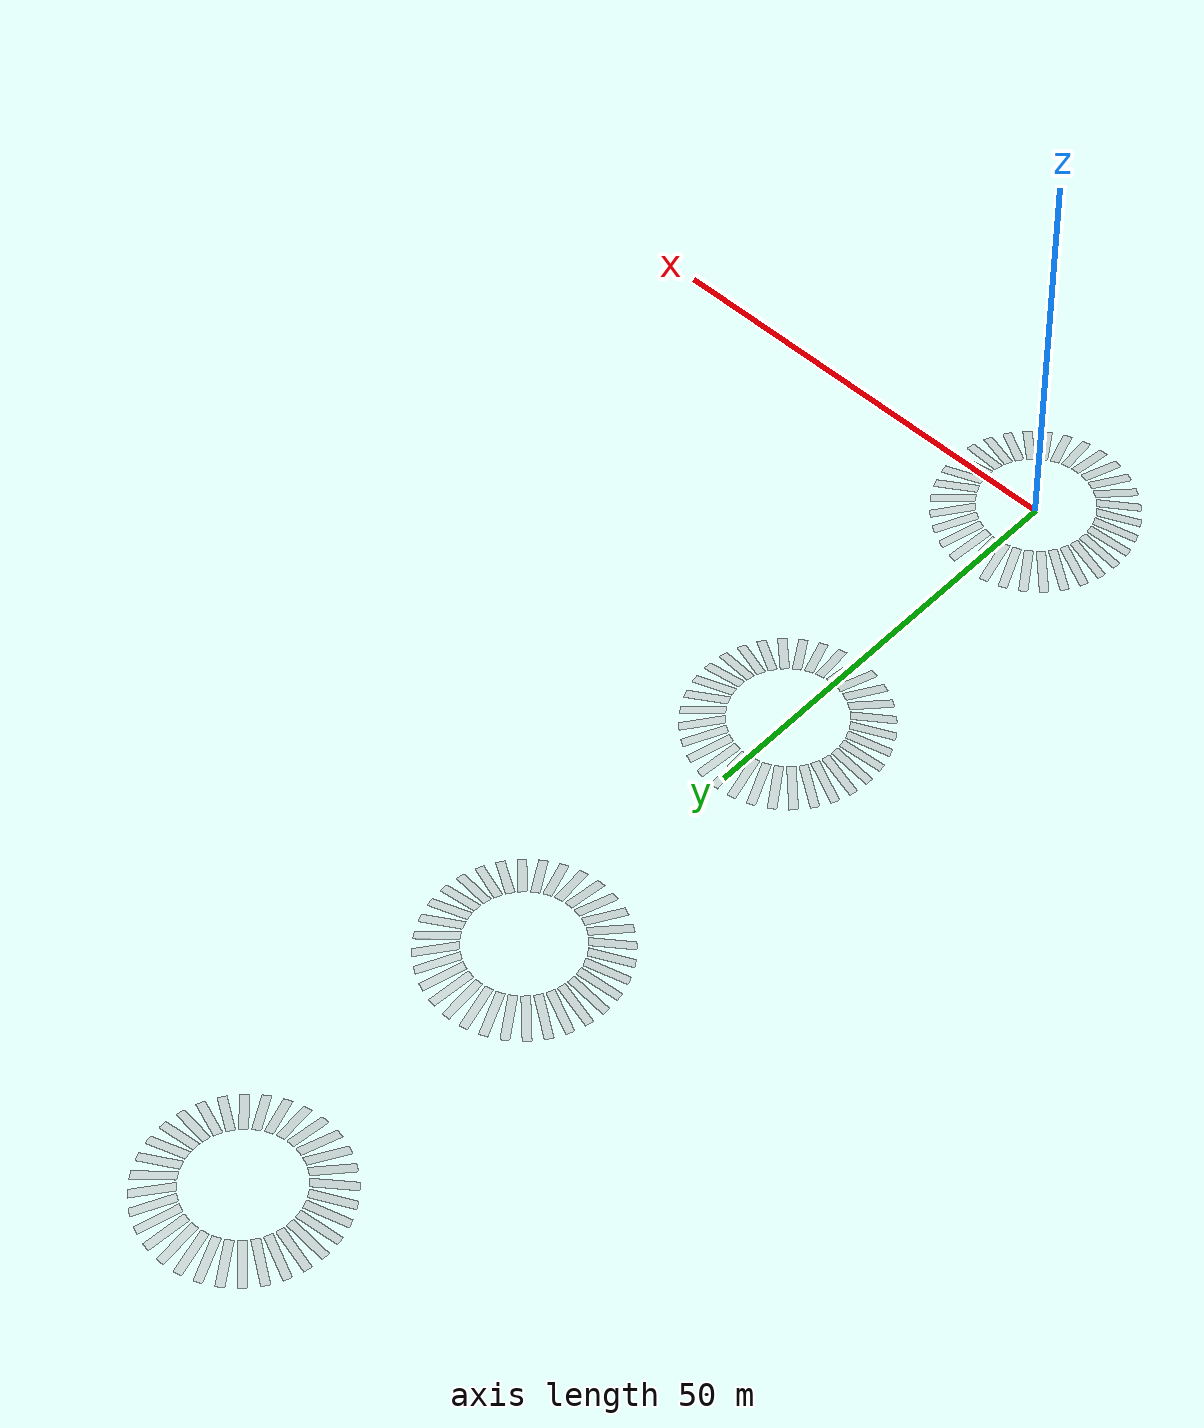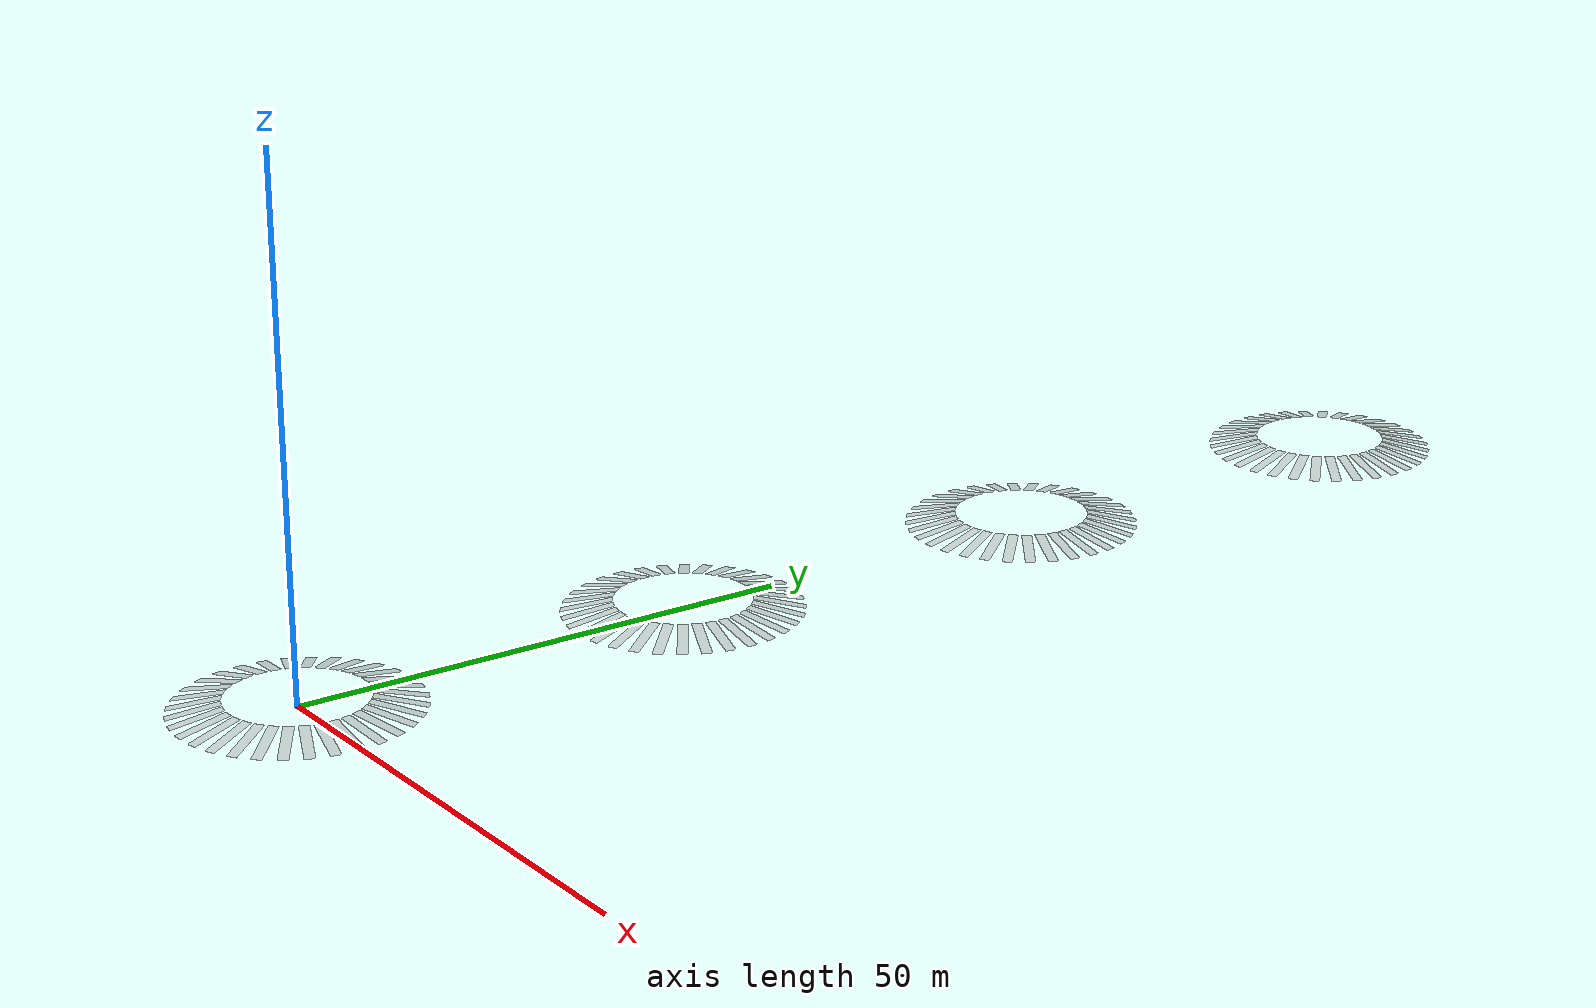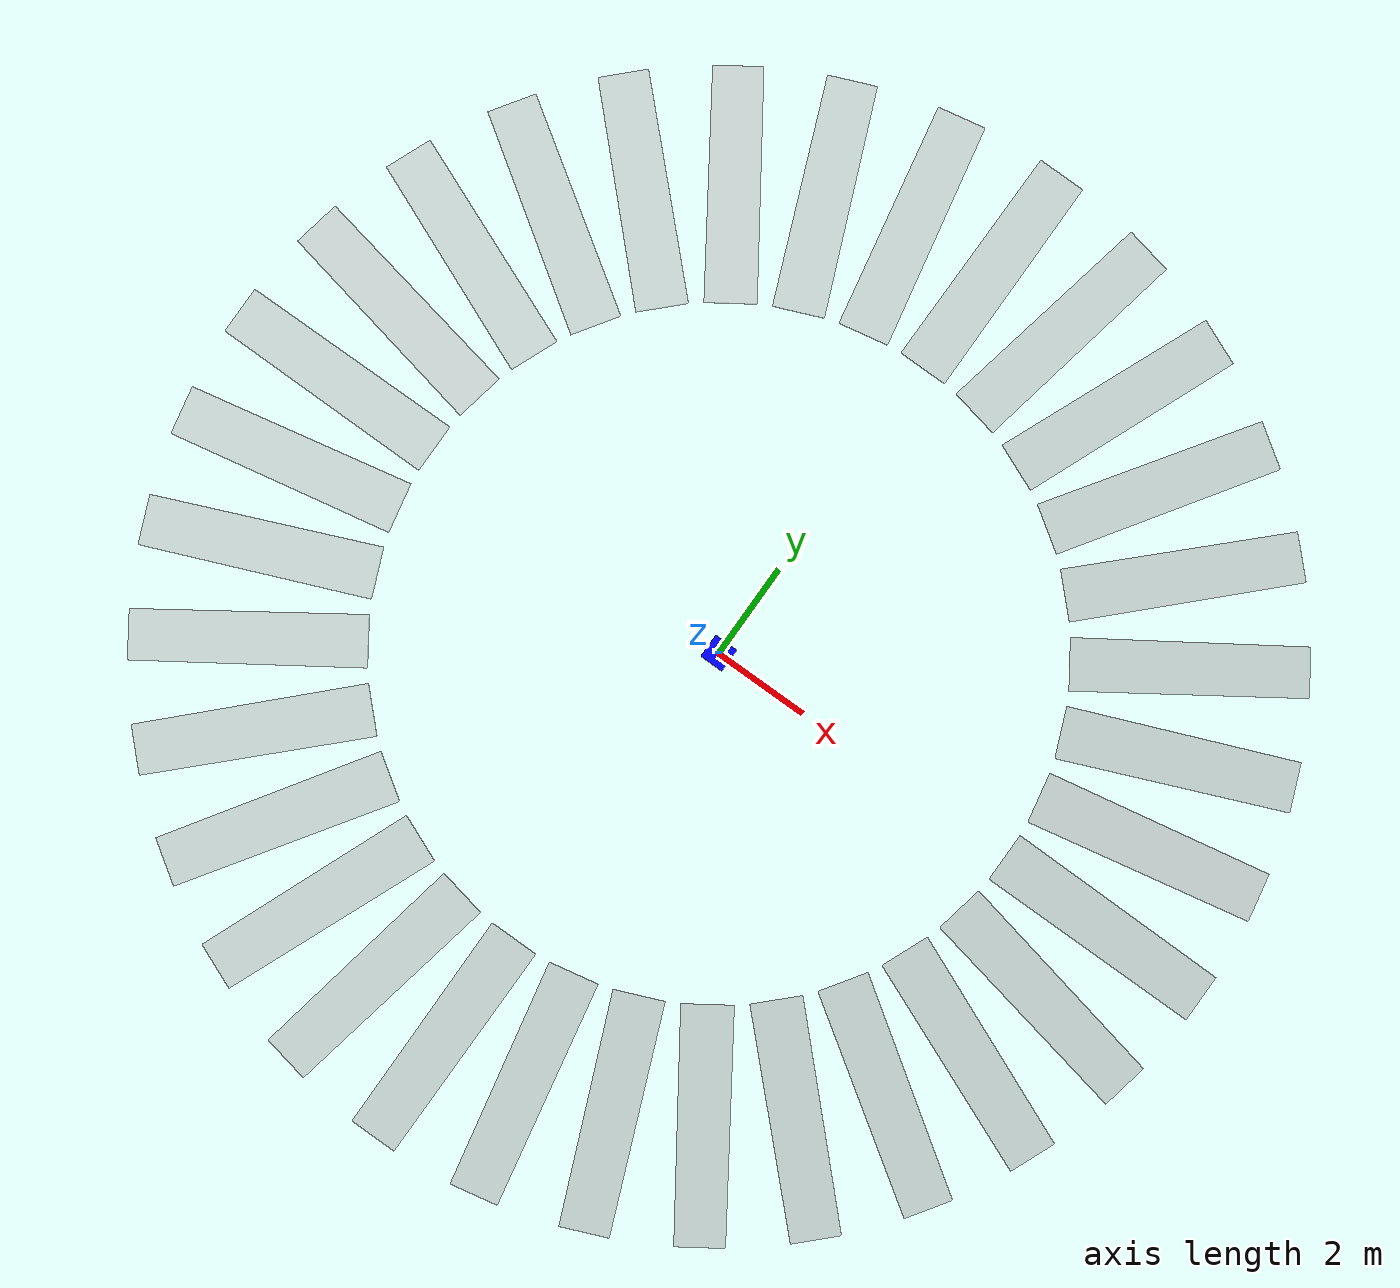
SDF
<?xml version="1.0" ?>
<!-- this file was generated using embedded ruby -->
<sdf version='1.7'>
  <world name='friction_pyramid'>
    <gravity>0 0 -9.8</gravity>
    <magnetic_field>6e-06 2.3e-05 -4.2e-05</magnetic_field>
    <atmosphere type='adiabatic'/>
    <physics name='1ms' type='ignored'>
      <max_step_size>0.001</max_step_size>
      <real_time_factor>1</real_time_factor>
      <real_time_update_rate>1000</real_time_update_rate>
    </physics>
    <scene>
      <ambient>0.4 0.4 0.4 1</ambient>
      <background>0.7 0.7 0.7 1</background>
      <shadows>1</shadows>
    </scene>
    <plugin filename="gz-sim-physics-system" name="gz::sim::systems::Physics"/>
    <plugin filename="gz-sim-user-commands-system" name="gz::sim::systems::UserCommands"/>
    <plugin filename="gz-sim-scene-broadcaster-system" name="gz::sim::systems::SceneBroadcaster"/>
    <model name='groundplane'>
      <static>1</static>
      <pose>0 0 0 0 0 0</pose>
      <link name='link'>
        <collision name='collision'>
          <geometry>
            <plane>
              <normal>0 0 1</normal>
              <size>1 1</size>
            </plane>
          </geometry>
          <surface>
            <friction>
              <ode/>
            </friction>
            <contact/>
          </surface>
        </collision>
      </link>
    </model>

      <model name='boxes_ramp_0'>
        <pose relative_to='groundplane'>9.0 0.0 0.5 0 0.2 0.0</pose>
        <static>1</static>
        <link name="link">
          <pose>0 0 0 0 0 0</pose>
          <collision name="collision">
            <pose relative_to="link">0 0 0 0 0 0</pose>
            <geometry>
              <box>
                <size>5 1 0.02</size>
              </box>
            </geometry>
            <surface>
              <contact>
                <ode>
                  <kp>1e+06</kp>
                  <kd>1</kd>
                </ode>
              </contact>
              <friction>
                <ode>
                  <mu>1</mu>
                  <mu2>1</mu2>
                </ode>
              </friction>
            </surface>
          </collision>
          <visual name="visual">
            <pose>0 0 0 0 0 0</pose>
            <geometry>
              <box>
                <size>5 1 0.02</size>
              </box>
            </geometry>
            <material>
              <ambient> .3 .3 .3  0.5</ambient>
              <diffuse> .7 .7 .7  0.5</diffuse>
              <specular> 0.01 0.01 0.01 1.000000</specular>
            </material>
          </visual>
          <gravity>0</gravity>
          <velocity_decay/>
        </link>
      </model>
      <model name='boxes_box_0'>
        <pose relative_to='boxes_ramp_0'>0 0 0.1 0 0 0</pose>
        <link name='link_1'>
          <inertial>
            <mass>1</mass>
            <inertia>
              <ixx>0.02416666666666667</ixx>
              <ixy>0</ixy>
              <ixz>0</ixz>
              <iyy>0.02416666666666667</iyy>
              <iyz>0</iyz>
              <izz>0.041666666666666664</izz>
            </inertia>
          </inertial>
          <collision name='collision'>
            <geometry>
              <box>
                <size>0.5 0.5 0.2</size>
              </box>
            </geometry>
            <surface>
              <friction>
                <ode>
                  <mu>0.05</mu>
                  <mu2>0.05</mu2>
                  <fdir1></fdir1>
                </ode>
              </friction>
            </surface>
          </collision>
          <visual name='visual'>
            <geometry>
              <box>
                <size>0.5 0.5 0.2</size>
              </box>
            </geometry>
            <material>
              <ambient>0 0 1 1</ambient>
              <diffuse>0 0 1 1</diffuse>
              <specular>0.1 0.1 0.1 1</specular>
            </material>
          </visual>
        </link>
      </model>

      <model name='boxes_ramp_1'>
        <pose relative_to='groundplane'>8.827067523629074 1.7558128981451542 0.5 0 0.2 0.19634954084936207</pose>
        <static>1</static>
        <link name="link">
          <pose>0 0 0 0 0 0</pose>
          <collision name="collision">
            <pose relative_to="link">0 0 0 0 0 0</pose>
            <geometry>
              <box>
                <size>5 1 0.02</size>
              </box>
            </geometry>
            <surface>
              <contact>
                <ode>
                  <kp>1e+06</kp>
                  <kd>1</kd>
                </ode>
              </contact>
              <friction>
                <ode>
                  <mu>1</mu>
                  <mu2>1</mu2>
                </ode>
              </friction>
            </surface>
          </collision>
          <visual name="visual">
            <pose>0 0 0 0 0 0</pose>
            <geometry>
              <box>
                <size>5 1 0.02</size>
              </box>
            </geometry>
            <material>
              <ambient> .3 .3 .3  0.5</ambient>
              <diffuse> .7 .7 .7  0.5</diffuse>
              <specular> 0.01 0.01 0.01 1.000000</specular>
            </material>
          </visual>
          <gravity>0</gravity>
          <velocity_decay/>
        </link>
      </model>
      <model name='boxes_box_1'>
        <pose relative_to='boxes_ramp_1'>0 0 0.1 0 0 0</pose>
        <link name='link_1'>
          <inertial>
            <mass>1</mass>
            <inertia>
              <ixx>0.02416666666666667</ixx>
              <ixy>0</ixy>
              <ixz>0</ixz>
              <iyy>0.02416666666666667</iyy>
              <iyz>0</iyz>
              <izz>0.041666666666666664</izz>
            </inertia>
          </inertial>
          <collision name='collision'>
            <geometry>
              <box>
                <size>0.5 0.5 0.2</size>
              </box>
            </geometry>
            <surface>
              <friction>
                <ode>
                  <mu>0.05</mu>
                  <mu2>0.05</mu2>
                  <fdir1></fdir1>
                </ode>
              </friction>
            </surface>
          </collision>
          <visual name='visual'>
            <geometry>
              <box>
                <size>0.5 0.5 0.2</size>
              </box>
            </geometry>
            <material>
              <ambient>0 0 1 1</ambient>
              <diffuse>0 0 1 1</diffuse>
              <specular>0.1 0.1 0.1 1</specular>
            </material>
          </visual>
        </link>
      </model>

      <model name='boxes_ramp_2'>
        <pose relative_to='groundplane'>8.31491579260158 3.444150891285808 0.5 0 0.2 0.39269908169872414</pose>
        <static>1</static>
        <link name="link">
          <pose>0 0 0 0 0 0</pose>
          <collision name="collision">
            <pose relative_to="link">0 0 0 0 0 0</pose>
            <geometry>
              <box>
                <size>5 1 0.02</size>
              </box>
            </geometry>
            <surface>
              <contact>
                <ode>
                  <kp>1e+06</kp>
                  <kd>1</kd>
                </ode>
              </contact>
              <friction>
                <ode>
                  <mu>1</mu>
                  <mu2>1</mu2>
                </ode>
              </friction>
            </surface>
          </collision>
          <visual name="visual">
            <pose>0 0 0 0 0 0</pose>
            <geometry>
              <box>
                <size>5 1 0.02</size>
              </box>
            </geometry>
            <material>
              <ambient> .3 .3 .3  0.5</ambient>
              <diffuse> .7 .7 .7  0.5</diffuse>
              <specular> 0.01 0.01 0.01 1.000000</specular>
            </material>
          </visual>
          <gravity>0</gravity>
          <velocity_decay/>
        </link>
      </model>
      <model name='boxes_box_2'>
        <pose relative_to='boxes_ramp_2'>0 0 0.1 0 0 0</pose>
        <link name='link_1'>
          <inertial>
            <mass>1</mass>
            <inertia>
              <ixx>0.02416666666666667</ixx>
              <ixy>0</ixy>
              <ixz>0</ixz>
              <iyy>0.02416666666666667</iyy>
              <iyz>0</iyz>
              <izz>0.041666666666666664</izz>
            </inertia>
          </inertial>
          <collision name='collision'>
            <geometry>
              <box>
                <size>0.5 0.5 0.2</size>
              </box>
            </geometry>
            <surface>
              <friction>
                <ode>
                  <mu>0.05</mu>
                  <mu2>0.05</mu2>
                  <fdir1></fdir1>
                </ode>
              </friction>
            </surface>
          </collision>
          <visual name='visual'>
            <geometry>
              <box>
                <size>0.5 0.5 0.2</size>
              </box>
            </geometry>
            <material>
              <ambient>0 0 1 1</ambient>
              <diffuse>0 0 1 1</diffuse>
              <specular>0.1 0.1 0.1 1</specular>
            </material>
          </visual>
        </link>
      </model>

      <model name='boxes_ramp_3'>
        <pose relative_to='groundplane'>7.483226510722907 5.00013209717642 0.5 0 0.2 0.5890486225480862</pose>
        <static>1</static>
        <link name="link">
          <pose>0 0 0 0 0 0</pose>
          <collision name="collision">
            <pose relative_to="link">0 0 0 0 0 0</pose>
            <geometry>
              <box>
                <size>5 1 0.02</size>
              </box>
            </geometry>
            <surface>
              <contact>
                <ode>
                  <kp>1e+06</kp>
                  <kd>1</kd>
                </ode>
              </contact>
              <friction>
                <ode>
                  <mu>1</mu>
                  <mu2>1</mu2>
                </ode>
              </friction>
            </surface>
          </collision>
          <visual name="visual">
            <pose>0 0 0 0 0 0</pose>
            <geometry>
              <box>
                <size>5 1 0.02</size>
              </box>
            </geometry>
            <material>
              <ambient> .3 .3 .3  0.5</ambient>
              <diffuse> .7 .7 .7  0.5</diffuse>
              <specular> 0.01 0.01 0.01 1.000000</specular>
            </material>
          </visual>
          <gravity>0</gravity>
          <velocity_decay/>
        </link>
      </model>
      <model name='boxes_box_3'>
        <pose relative_to='boxes_ramp_3'>0 0 0.1 0 0 0</pose>
        <link name='link_1'>
          <inertial>
            <mass>1</mass>
            <inertia>
              <ixx>0.02416666666666667</ixx>
              <ixy>0</ixy>
              <ixz>0</ixz>
              <iyy>0.02416666666666667</iyy>
              <iyz>0</iyz>
              <izz>0.041666666666666664</izz>
            </inertia>
          </inertial>
          <collision name='collision'>
            <geometry>
              <box>
                <size>0.5 0.5 0.2</size>
              </box>
            </geometry>
            <surface>
              <friction>
                <ode>
                  <mu>0.05</mu>
                  <mu2>0.05</mu2>
                  <fdir1></fdir1>
                </ode>
              </friction>
            </surface>
          </collision>
          <visual name='visual'>
            <geometry>
              <box>
                <size>0.5 0.5 0.2</size>
              </box>
            </geometry>
            <material>
              <ambient>0 0 1 1</ambient>
              <diffuse>0 0 1 1</diffuse>
              <specular>0.1 0.1 0.1 1</specular>
            </material>
          </visual>
        </link>
      </model>

      <model name='boxes_ramp_4'>
        <pose relative_to='groundplane'>6.3639610306789285 6.363961030678928 0.5 0 0.2 0.7853981633974483</pose>
        <static>1</static>
        <link name="link">
          <pose>0 0 0 0 0 0</pose>
          <collision name="collision">
            <pose relative_to="link">0 0 0 0 0 0</pose>
            <geometry>
              <box>
                <size>5 1 0.02</size>
              </box>
            </geometry>
            <surface>
              <contact>
                <ode>
                  <kp>1e+06</kp>
                  <kd>1</kd>
                </ode>
              </contact>
              <friction>
                <ode>
                  <mu>1</mu>
                  <mu2>1</mu2>
                </ode>
              </friction>
            </surface>
          </collision>
          <visual name="visual">
            <pose>0 0 0 0 0 0</pose>
            <geometry>
              <box>
                <size>5 1 0.02</size>
              </box>
            </geometry>
            <material>
              <ambient> .3 .3 .3  0.5</ambient>
              <diffuse> .7 .7 .7  0.5</diffuse>
              <specular> 0.01 0.01 0.01 1.000000</specular>
            </material>
          </visual>
          <gravity>0</gravity>
          <velocity_decay/>
        </link>
      </model>
      <model name='boxes_box_4'>
        <pose relative_to='boxes_ramp_4'>0 0 0.1 0 0 0</pose>
        <link name='link_1'>
          <inertial>
            <mass>1</mass>
            <inertia>
              <ixx>0.02416666666666667</ixx>
              <ixy>0</ixy>
              <ixz>0</ixz>
              <iyy>0.02416666666666667</iyy>
              <iyz>0</iyz>
              <izz>0.041666666666666664</izz>
            </inertia>
          </inertial>
          <collision name='collision'>
            <geometry>
              <box>
                <size>0.5 0.5 0.2</size>
              </box>
            </geometry>
            <surface>
              <friction>
                <ode>
                  <mu>0.05</mu>
                  <mu2>0.05</mu2>
                  <fdir1></fdir1>
                </ode>
              </friction>
            </surface>
          </collision>
          <visual name='visual'>
            <geometry>
              <box>
                <size>0.5 0.5 0.2</size>
              </box>
            </geometry>
            <material>
              <ambient>0 0 1 1</ambient>
              <diffuse>0 0 1 1</diffuse>
              <specular>0.1 0.1 0.1 1</specular>
            </material>
          </visual>
        </link>
      </model>

      <model name='boxes_ramp_5'>
        <pose relative_to='groundplane'>5.0001320971764205 7.483226510722907 0.5 0 0.2 0.9817477042468103</pose>
        <static>1</static>
        <link name="link">
          <pose>0 0 0 0 0 0</pose>
          <collision name="collision">
            <pose relative_to="link">0 0 0 0 0 0</pose>
            <geometry>
              <box>
                <size>5 1 0.02</size>
              </box>
            </geometry>
            <surface>
              <contact>
                <ode>
                  <kp>1e+06</kp>
                  <kd>1</kd>
                </ode>
              </contact>
              <friction>
                <ode>
                  <mu>1</mu>
                  <mu2>1</mu2>
                </ode>
              </friction>
            </surface>
          </collision>
          <visual name="visual">
            <pose>0 0 0 0 0 0</pose>
            <geometry>
              <box>
                <size>5 1 0.02</size>
              </box>
            </geometry>
            <material>
              <ambient> .3 .3 .3  0.5</ambient>
              <diffuse> .7 .7 .7  0.5</diffuse>
              <specular> 0.01 0.01 0.01 1.000000</specular>
            </material>
          </visual>
          <gravity>0</gravity>
          <velocity_decay/>
        </link>
      </model>
      <model name='boxes_box_5'>
        <pose relative_to='boxes_ramp_5'>0 0 0.1 0 0 0</pose>
        <link name='link_1'>
          <inertial>
            <mass>1</mass>
            <inertia>
              <ixx>0.02416666666666667</ixx>
              <ixy>0</ixy>
              <ixz>0</ixz>
              <iyy>0.02416666666666667</iyy>
              <iyz>0</iyz>
              <izz>0.041666666666666664</izz>
            </inertia>
          </inertial>
          <collision name='collision'>
            <geometry>
              <box>
                <size>0.5 0.5 0.2</size>
              </box>
            </geometry>
            <surface>
              <friction>
                <ode>
                  <mu>0.05</mu>
                  <mu2>0.05</mu2>
                  <fdir1></fdir1>
                </ode>
              </friction>
            </surface>
          </collision>
          <visual name='visual'>
            <geometry>
              <box>
                <size>0.5 0.5 0.2</size>
              </box>
            </geometry>
            <material>
              <ambient>0 0 1 1</ambient>
              <diffuse>0 0 1 1</diffuse>
              <specular>0.1 0.1 0.1 1</specular>
            </material>
          </visual>
        </link>
      </model>

      <model name='boxes_ramp_6'>
        <pose relative_to='groundplane'>3.4441508912858083 8.31491579260158 0.5 0 0.2 1.1780972450961724</pose>
        <static>1</static>
        <link name="link">
          <pose>0 0 0 0 0 0</pose>
          <collision name="collision">
            <pose relative_to="link">0 0 0 0 0 0</pose>
            <geometry>
              <box>
                <size>5 1 0.02</size>
              </box>
            </geometry>
            <surface>
              <contact>
                <ode>
                  <kp>1e+06</kp>
                  <kd>1</kd>
                </ode>
              </contact>
              <friction>
                <ode>
                  <mu>1</mu>
                  <mu2>1</mu2>
                </ode>
              </friction>
            </surface>
          </collision>
          <visual name="visual">
            <pose>0 0 0 0 0 0</pose>
            <geometry>
              <box>
                <size>5 1 0.02</size>
              </box>
            </geometry>
            <material>
              <ambient> .3 .3 .3  0.5</ambient>
              <diffuse> .7 .7 .7  0.5</diffuse>
              <specular> 0.01 0.01 0.01 1.000000</specular>
            </material>
          </visual>
          <gravity>0</gravity>
          <velocity_decay/>
        </link>
      </model>
      <model name='boxes_box_6'>
        <pose relative_to='boxes_ramp_6'>0 0 0.1 0 0 0</pose>
        <link name='link_1'>
          <inertial>
            <mass>1</mass>
            <inertia>
              <ixx>0.02416666666666667</ixx>
              <ixy>0</ixy>
              <ixz>0</ixz>
              <iyy>0.02416666666666667</iyy>
              <iyz>0</iyz>
              <izz>0.041666666666666664</izz>
            </inertia>
          </inertial>
          <collision name='collision'>
            <geometry>
              <box>
                <size>0.5 0.5 0.2</size>
              </box>
            </geometry>
            <surface>
              <friction>
                <ode>
                  <mu>0.05</mu>
                  <mu2>0.05</mu2>
                  <fdir1></fdir1>
                </ode>
              </friction>
            </surface>
          </collision>
          <visual name='visual'>
            <geometry>
              <box>
                <size>0.5 0.5 0.2</size>
              </box>
            </geometry>
            <material>
              <ambient>0 0 1 1</ambient>
              <diffuse>0 0 1 1</diffuse>
              <specular>0.1 0.1 0.1 1</specular>
            </material>
          </visual>
        </link>
      </model>

      <model name='boxes_ramp_7'>
        <pose relative_to='groundplane'>1.755812898145155 8.827067523629074 0.5 0 0.2 1.3744467859455345</pose>
        <static>1</static>
        <link name="link">
          <pose>0 0 0 0 0 0</pose>
          <collision name="collision">
            <pose relative_to="link">0 0 0 0 0 0</pose>
            <geometry>
              <box>
                <size>5 1 0.02</size>
              </box>
            </geometry>
            <surface>
              <contact>
                <ode>
                  <kp>1e+06</kp>
                  <kd>1</kd>
                </ode>
              </contact>
              <friction>
                <ode>
                  <mu>1</mu>
                  <mu2>1</mu2>
                </ode>
              </friction>
            </surface>
          </collision>
          <visual name="visual">
            <pose>0 0 0 0 0 0</pose>
            <geometry>
              <box>
                <size>5 1 0.02</size>
              </box>
            </geometry>
            <material>
              <ambient> .3 .3 .3  0.5</ambient>
              <diffuse> .7 .7 .7  0.5</diffuse>
              <specular> 0.01 0.01 0.01 1.000000</specular>
            </material>
          </visual>
          <gravity>0</gravity>
          <velocity_decay/>
        </link>
      </model>
      <model name='boxes_box_7'>
        <pose relative_to='boxes_ramp_7'>0 0 0.1 0 0 0</pose>
        <link name='link_1'>
          <inertial>
            <mass>1</mass>
            <inertia>
              <ixx>0.02416666666666667</ixx>
              <ixy>0</ixy>
              <ixz>0</ixz>
              <iyy>0.02416666666666667</iyy>
              <iyz>0</iyz>
              <izz>0.041666666666666664</izz>
            </inertia>
          </inertial>
          <collision name='collision'>
            <geometry>
              <box>
                <size>0.5 0.5 0.2</size>
              </box>
            </geometry>
            <surface>
              <friction>
                <ode>
                  <mu>0.05</mu>
                  <mu2>0.05</mu2>
                  <fdir1></fdir1>
                </ode>
              </friction>
            </surface>
          </collision>
          <visual name='visual'>
            <geometry>
              <box>
                <size>0.5 0.5 0.2</size>
              </box>
            </geometry>
            <material>
              <ambient>0 0 1 1</ambient>
              <diffuse>0 0 1 1</diffuse>
              <specular>0.1 0.1 0.1 1</specular>
            </material>
          </visual>
        </link>
      </model>

      <model name='boxes_ramp_8'>
        <pose relative_to='groundplane'>5.51091059616309e-16 9.0 0.5 0 0.2 1.5707963267948966</pose>
        <static>1</static>
        <link name="link">
          <pose>0 0 0 0 0 0</pose>
          <collision name="collision">
            <pose relative_to="link">0 0 0 0 0 0</pose>
            <geometry>
              <box>
                <size>5 1 0.02</size>
              </box>
            </geometry>
            <surface>
              <contact>
                <ode>
                  <kp>1e+06</kp>
                  <kd>1</kd>
                </ode>
              </contact>
              <friction>
                <ode>
                  <mu>1</mu>
                  <mu2>1</mu2>
                </ode>
              </friction>
            </surface>
          </collision>
          <visual name="visual">
            <pose>0 0 0 0 0 0</pose>
            <geometry>
              <box>
                <size>5 1 0.02</size>
              </box>
            </geometry>
            <material>
              <ambient> .3 .3 .3  0.5</ambient>
              <diffuse> .7 .7 .7  0.5</diffuse>
              <specular> 0.01 0.01 0.01 1.000000</specular>
            </material>
          </visual>
          <gravity>0</gravity>
          <velocity_decay/>
        </link>
      </model>
      <model name='boxes_box_8'>
        <pose relative_to='boxes_ramp_8'>0 0 0.1 0 0 0</pose>
        <link name='link_1'>
          <inertial>
            <mass>1</mass>
            <inertia>
              <ixx>0.02416666666666667</ixx>
              <ixy>0</ixy>
              <ixz>0</ixz>
              <iyy>0.02416666666666667</iyy>
              <iyz>0</iyz>
              <izz>0.041666666666666664</izz>
            </inertia>
          </inertial>
          <collision name='collision'>
            <geometry>
              <box>
                <size>0.5 0.5 0.2</size>
              </box>
            </geometry>
            <surface>
              <friction>
                <ode>
                  <mu>0.05</mu>
                  <mu2>0.05</mu2>
                  <fdir1></fdir1>
                </ode>
              </friction>
            </surface>
          </collision>
          <visual name='visual'>
            <geometry>
              <box>
                <size>0.5 0.5 0.2</size>
              </box>
            </geometry>
            <material>
              <ambient>0 0 1 1</ambient>
              <diffuse>0 0 1 1</diffuse>
              <specular>0.1 0.1 0.1 1</specular>
            </material>
          </visual>
        </link>
      </model>

      <model name='boxes_ramp_9'>
        <pose relative_to='groundplane'>-1.7558128981451537 8.827067523629074 0.5 0 0.2 1.7671458676442586</pose>
        <static>1</static>
        <link name="link">
          <pose>0 0 0 0 0 0</pose>
          <collision name="collision">
            <pose relative_to="link">0 0 0 0 0 0</pose>
            <geometry>
              <box>
                <size>5 1 0.02</size>
              </box>
            </geometry>
            <surface>
              <contact>
                <ode>
                  <kp>1e+06</kp>
                  <kd>1</kd>
                </ode>
              </contact>
              <friction>
                <ode>
                  <mu>1</mu>
                  <mu2>1</mu2>
                </ode>
              </friction>
            </surface>
          </collision>
          <visual name="visual">
            <pose>0 0 0 0 0 0</pose>
            <geometry>
              <box>
                <size>5 1 0.02</size>
              </box>
            </geometry>
            <material>
              <ambient> .3 .3 .3  0.5</ambient>
              <diffuse> .7 .7 .7  0.5</diffuse>
              <specular> 0.01 0.01 0.01 1.000000</specular>
            </material>
          </visual>
          <gravity>0</gravity>
          <velocity_decay/>
        </link>
      </model>
      <model name='boxes_box_9'>
        <pose relative_to='boxes_ramp_9'>0 0 0.1 0 0 0</pose>
        <link name='link_1'>
          <inertial>
            <mass>1</mass>
            <inertia>
              <ixx>0.02416666666666667</ixx>
              <ixy>0</ixy>
              <ixz>0</ixz>
              <iyy>0.02416666666666667</iyy>
              <iyz>0</iyz>
              <izz>0.041666666666666664</izz>
            </inertia>
          </inertial>
          <collision name='collision'>
            <geometry>
              <box>
                <size>0.5 0.5 0.2</size>
              </box>
            </geometry>
            <surface>
              <friction>
                <ode>
                  <mu>0.05</mu>
                  <mu2>0.05</mu2>
                  <fdir1></fdir1>
                </ode>
              </friction>
            </surface>
          </collision>
          <visual name='visual'>
            <geometry>
              <box>
                <size>0.5 0.5 0.2</size>
              </box>
            </geometry>
            <material>
              <ambient>0 0 1 1</ambient>
              <diffuse>0 0 1 1</diffuse>
              <specular>0.1 0.1 0.1 1</specular>
            </material>
          </visual>
        </link>
      </model>

      <model name='boxes_ramp_10'>
        <pose relative_to='groundplane'>-3.4441508912858074 8.31491579260158 0.5 0 0.2 1.9634954084936207</pose>
        <static>1</static>
        <link name="link">
          <pose>0 0 0 0 0 0</pose>
          <collision name="collision">
            <pose relative_to="link">0 0 0 0 0 0</pose>
            <geometry>
              <box>
                <size>5 1 0.02</size>
              </box>
            </geometry>
            <surface>
              <contact>
                <ode>
                  <kp>1e+06</kp>
                  <kd>1</kd>
                </ode>
              </contact>
              <friction>
                <ode>
                  <mu>1</mu>
                  <mu2>1</mu2>
                </ode>
              </friction>
            </surface>
          </collision>
          <visual name="visual">
            <pose>0 0 0 0 0 0</pose>
            <geometry>
              <box>
                <size>5 1 0.02</size>
              </box>
            </geometry>
            <material>
              <ambient> .3 .3 .3  0.5</ambient>
              <diffuse> .7 .7 .7  0.5</diffuse>
              <specular> 0.01 0.01 0.01 1.000000</specular>
            </material>
          </visual>
          <gravity>0</gravity>
          <velocity_decay/>
        </link>
      </model>
      <model name='boxes_box_10'>
        <pose relative_to='boxes_ramp_10'>0 0 0.1 0 0 0</pose>
        <link name='link_1'>
          <inertial>
            <mass>1</mass>
            <inertia>
              <ixx>0.02416666666666667</ixx>
              <ixy>0</ixy>
              <ixz>0</ixz>
              <iyy>0.02416666666666667</iyy>
              <iyz>0</iyz>
              <izz>0.041666666666666664</izz>
            </inertia>
          </inertial>
          <collision name='collision'>
            <geometry>
              <box>
                <size>0.5 0.5 0.2</size>
              </box>
            </geometry>
            <surface>
              <friction>
                <ode>
                  <mu>0.05</mu>
                  <mu2>0.05</mu2>
                  <fdir1></fdir1>
                </ode>
              </friction>
            </surface>
          </collision>
          <visual name='visual'>
            <geometry>
              <box>
                <size>0.5 0.5 0.2</size>
              </box>
            </geometry>
            <material>
              <ambient>0 0 1 1</ambient>
              <diffuse>0 0 1 1</diffuse>
              <specular>0.1 0.1 0.1 1</specular>
            </material>
          </visual>
        </link>
      </model>

      <model name='boxes_ramp_11'>
        <pose relative_to='groundplane'>-5.000132097176418 7.4832265107229095 0.5 0 0.2 2.1598449493429825</pose>
        <static>1</static>
        <link name="link">
          <pose>0 0 0 0 0 0</pose>
          <collision name="collision">
            <pose relative_to="link">0 0 0 0 0 0</pose>
            <geometry>
              <box>
                <size>5 1 0.02</size>
              </box>
            </geometry>
            <surface>
              <contact>
                <ode>
                  <kp>1e+06</kp>
                  <kd>1</kd>
                </ode>
              </contact>
              <friction>
                <ode>
                  <mu>1</mu>
                  <mu2>1</mu2>
                </ode>
              </friction>
            </surface>
          </collision>
          <visual name="visual">
            <pose>0 0 0 0 0 0</pose>
            <geometry>
              <box>
                <size>5 1 0.02</size>
              </box>
            </geometry>
            <material>
              <ambient> .3 .3 .3  0.5</ambient>
              <diffuse> .7 .7 .7  0.5</diffuse>
              <specular> 0.01 0.01 0.01 1.000000</specular>
            </material>
          </visual>
          <gravity>0</gravity>
          <velocity_decay/>
        </link>
      </model>
      <model name='boxes_box_11'>
        <pose relative_to='boxes_ramp_11'>0 0 0.1 0 0 0</pose>
        <link name='link_1'>
          <inertial>
            <mass>1</mass>
            <inertia>
              <ixx>0.02416666666666667</ixx>
              <ixy>0</ixy>
              <ixz>0</ixz>
              <iyy>0.02416666666666667</iyy>
              <iyz>0</iyz>
              <izz>0.041666666666666664</izz>
            </inertia>
          </inertial>
          <collision name='collision'>
            <geometry>
              <box>
                <size>0.5 0.5 0.2</size>
              </box>
            </geometry>
            <surface>
              <friction>
                <ode>
                  <mu>0.05</mu>
                  <mu2>0.05</mu2>
                  <fdir1></fdir1>
                </ode>
              </friction>
            </surface>
          </collision>
          <visual name='visual'>
            <geometry>
              <box>
                <size>0.5 0.5 0.2</size>
              </box>
            </geometry>
            <material>
              <ambient>0 0 1 1</ambient>
              <diffuse>0 0 1 1</diffuse>
              <specular>0.1 0.1 0.1 1</specular>
            </material>
          </visual>
        </link>
      </model>

      <model name='boxes_ramp_12'>
        <pose relative_to='groundplane'>-6.363961030678928 6.3639610306789285 0.5 0 0.2 2.356194490192345</pose>
        <static>1</static>
        <link name="link">
          <pose>0 0 0 0 0 0</pose>
          <collision name="collision">
            <pose relative_to="link">0 0 0 0 0 0</pose>
            <geometry>
              <box>
                <size>5 1 0.02</size>
              </box>
            </geometry>
            <surface>
              <contact>
                <ode>
                  <kp>1e+06</kp>
                  <kd>1</kd>
                </ode>
              </contact>
              <friction>
                <ode>
                  <mu>1</mu>
                  <mu2>1</mu2>
                </ode>
              </friction>
            </surface>
          </collision>
          <visual name="visual">
            <pose>0 0 0 0 0 0</pose>
            <geometry>
              <box>
                <size>5 1 0.02</size>
              </box>
            </geometry>
            <material>
              <ambient> .3 .3 .3  0.5</ambient>
              <diffuse> .7 .7 .7  0.5</diffuse>
              <specular> 0.01 0.01 0.01 1.000000</specular>
            </material>
          </visual>
          <gravity>0</gravity>
          <velocity_decay/>
        </link>
      </model>
      <model name='boxes_box_12'>
        <pose relative_to='boxes_ramp_12'>0 0 0.1 0 0 0</pose>
        <link name='link_1'>
          <inertial>
            <mass>1</mass>
            <inertia>
              <ixx>0.02416666666666667</ixx>
              <ixy>0</ixy>
              <ixz>0</ixz>
              <iyy>0.02416666666666667</iyy>
              <iyz>0</iyz>
              <izz>0.041666666666666664</izz>
            </inertia>
          </inertial>
          <collision name='collision'>
            <geometry>
              <box>
                <size>0.5 0.5 0.2</size>
              </box>
            </geometry>
            <surface>
              <friction>
                <ode>
                  <mu>0.05</mu>
                  <mu2>0.05</mu2>
                  <fdir1></fdir1>
                </ode>
              </friction>
            </surface>
          </collision>
          <visual name='visual'>
            <geometry>
              <box>
                <size>0.5 0.5 0.2</size>
              </box>
            </geometry>
            <material>
              <ambient>0 0 1 1</ambient>
              <diffuse>0 0 1 1</diffuse>
              <specular>0.1 0.1 0.1 1</specular>
            </material>
          </visual>
        </link>
      </model>

      <model name='boxes_ramp_13'>
        <pose relative_to='groundplane'>-7.483226510722908 5.00013209717642 0.5 0 0.2 2.552544031041707</pose>
        <static>1</static>
        <link name="link">
          <pose>0 0 0 0 0 0</pose>
          <collision name="collision">
            <pose relative_to="link">0 0 0 0 0 0</pose>
            <geometry>
              <box>
                <size>5 1 0.02</size>
              </box>
            </geometry>
            <surface>
              <contact>
                <ode>
                  <kp>1e+06</kp>
                  <kd>1</kd>
                </ode>
              </contact>
              <friction>
                <ode>
                  <mu>1</mu>
                  <mu2>1</mu2>
                </ode>
              </friction>
            </surface>
          </collision>
          <visual name="visual">
            <pose>0 0 0 0 0 0</pose>
            <geometry>
              <box>
                <size>5 1 0.02</size>
              </box>
            </geometry>
            <material>
              <ambient> .3 .3 .3  0.5</ambient>
              <diffuse> .7 .7 .7  0.5</diffuse>
              <specular> 0.01 0.01 0.01 1.000000</specular>
            </material>
          </visual>
          <gravity>0</gravity>
          <velocity_decay/>
        </link>
      </model>
      <model name='boxes_box_13'>
        <pose relative_to='boxes_ramp_13'>0 0 0.1 0 0 0</pose>
        <link name='link_1'>
          <inertial>
            <mass>1</mass>
            <inertia>
              <ixx>0.02416666666666667</ixx>
              <ixy>0</ixy>
              <ixz>0</ixz>
              <iyy>0.02416666666666667</iyy>
              <iyz>0</iyz>
              <izz>0.041666666666666664</izz>
            </inertia>
          </inertial>
          <collision name='collision'>
            <geometry>
              <box>
                <size>0.5 0.5 0.2</size>
              </box>
            </geometry>
            <surface>
              <friction>
                <ode>
                  <mu>0.05</mu>
                  <mu2>0.05</mu2>
                  <fdir1></fdir1>
                </ode>
              </friction>
            </surface>
          </collision>
          <visual name='visual'>
            <geometry>
              <box>
                <size>0.5 0.5 0.2</size>
              </box>
            </geometry>
            <material>
              <ambient>0 0 1 1</ambient>
              <diffuse>0 0 1 1</diffuse>
              <specular>0.1 0.1 0.1 1</specular>
            </material>
          </visual>
        </link>
      </model>

      <model name='boxes_ramp_14'>
        <pose relative_to='groundplane'>-8.31491579260158 3.444150891285809 0.5 0 0.2 2.748893571891069</pose>
        <static>1</static>
        <link name="link">
          <pose>0 0 0 0 0 0</pose>
          <collision name="collision">
            <pose relative_to="link">0 0 0 0 0 0</pose>
            <geometry>
              <box>
                <size>5 1 0.02</size>
              </box>
            </geometry>
            <surface>
              <contact>
                <ode>
                  <kp>1e+06</kp>
                  <kd>1</kd>
                </ode>
              </contact>
              <friction>
                <ode>
                  <mu>1</mu>
                  <mu2>1</mu2>
                </ode>
              </friction>
            </surface>
          </collision>
          <visual name="visual">
            <pose>0 0 0 0 0 0</pose>
            <geometry>
              <box>
                <size>5 1 0.02</size>
              </box>
            </geometry>
            <material>
              <ambient> .3 .3 .3  0.5</ambient>
              <diffuse> .7 .7 .7  0.5</diffuse>
              <specular> 0.01 0.01 0.01 1.000000</specular>
            </material>
          </visual>
          <gravity>0</gravity>
          <velocity_decay/>
        </link>
      </model>
      <model name='boxes_box_14'>
        <pose relative_to='boxes_ramp_14'>0 0 0.1 0 0 0</pose>
        <link name='link_1'>
          <inertial>
            <mass>1</mass>
            <inertia>
              <ixx>0.02416666666666667</ixx>
              <ixy>0</ixy>
              <ixz>0</ixz>
              <iyy>0.02416666666666667</iyy>
              <iyz>0</iyz>
              <izz>0.041666666666666664</izz>
            </inertia>
          </inertial>
          <collision name='collision'>
            <geometry>
              <box>
                <size>0.5 0.5 0.2</size>
              </box>
            </geometry>
            <surface>
              <friction>
                <ode>
                  <mu>0.05</mu>
                  <mu2>0.05</mu2>
                  <fdir1></fdir1>
                </ode>
              </friction>
            </surface>
          </collision>
          <visual name='visual'>
            <geometry>
              <box>
                <size>0.5 0.5 0.2</size>
              </box>
            </geometry>
            <material>
              <ambient>0 0 1 1</ambient>
              <diffuse>0 0 1 1</diffuse>
              <specular>0.1 0.1 0.1 1</specular>
            </material>
          </visual>
        </link>
      </model>

      <model name='boxes_ramp_15'>
        <pose relative_to='groundplane'>-8.827067523629074 1.7558128981451575 0.5 0 0.2 2.945243112740431</pose>
        <static>1</static>
        <link name="link">
          <pose>0 0 0 0 0 0</pose>
          <collision name="collision">
            <pose relative_to="link">0 0 0 0 0 0</pose>
            <geometry>
              <box>
                <size>5 1 0.02</size>
              </box>
            </geometry>
            <surface>
              <contact>
                <ode>
                  <kp>1e+06</kp>
                  <kd>1</kd>
                </ode>
              </contact>
              <friction>
                <ode>
                  <mu>1</mu>
                  <mu2>1</mu2>
                </ode>
              </friction>
            </surface>
          </collision>
          <visual name="visual">
            <pose>0 0 0 0 0 0</pose>
            <geometry>
              <box>
                <size>5 1 0.02</size>
              </box>
            </geometry>
            <material>
              <ambient> .3 .3 .3  0.5</ambient>
              <diffuse> .7 .7 .7  0.5</diffuse>
              <specular> 0.01 0.01 0.01 1.000000</specular>
            </material>
          </visual>
          <gravity>0</gravity>
          <velocity_decay/>
        </link>
      </model>
      <model name='boxes_box_15'>
        <pose relative_to='boxes_ramp_15'>0 0 0.1 0 0 0</pose>
        <link name='link_1'>
          <inertial>
            <mass>1</mass>
            <inertia>
              <ixx>0.02416666666666667</ixx>
              <ixy>0</ixy>
              <ixz>0</ixz>
              <iyy>0.02416666666666667</iyy>
              <iyz>0</iyz>
              <izz>0.041666666666666664</izz>
            </inertia>
          </inertial>
          <collision name='collision'>
            <geometry>
              <box>
                <size>0.5 0.5 0.2</size>
              </box>
            </geometry>
            <surface>
              <friction>
                <ode>
                  <mu>0.05</mu>
                  <mu2>0.05</mu2>
                  <fdir1></fdir1>
                </ode>
              </friction>
            </surface>
          </collision>
          <visual name='visual'>
            <geometry>
              <box>
                <size>0.5 0.5 0.2</size>
              </box>
            </geometry>
            <material>
              <ambient>0 0 1 1</ambient>
              <diffuse>0 0 1 1</diffuse>
              <specular>0.1 0.1 0.1 1</specular>
            </material>
          </visual>
        </link>
      </model>

      <model name='boxes_ramp_16'>
        <pose relative_to='groundplane'>-9.0 1.102182119232618e-15 0.5 0 0.2 3.141592653589793</pose>
        <static>1</static>
        <link name="link">
          <pose>0 0 0 0 0 0</pose>
          <collision name="collision">
            <pose relative_to="link">0 0 0 0 0 0</pose>
            <geometry>
              <box>
                <size>5 1 0.02</size>
              </box>
            </geometry>
            <surface>
              <contact>
                <ode>
                  <kp>1e+06</kp>
                  <kd>1</kd>
                </ode>
              </contact>
              <friction>
                <ode>
                  <mu>1</mu>
                  <mu2>1</mu2>
                </ode>
              </friction>
            </surface>
          </collision>
          <visual name="visual">
            <pose>0 0 0 0 0 0</pose>
            <geometry>
              <box>
                <size>5 1 0.02</size>
              </box>
            </geometry>
            <material>
              <ambient> .3 .3 .3  0.5</ambient>
              <diffuse> .7 .7 .7  0.5</diffuse>
              <specular> 0.01 0.01 0.01 1.000000</specular>
            </material>
          </visual>
          <gravity>0</gravity>
          <velocity_decay/>
        </link>
      </model>
      <model name='boxes_box_16'>
        <pose relative_to='boxes_ramp_16'>0 0 0.1 0 0 0</pose>
        <link name='link_1'>
          <inertial>
            <mass>1</mass>
            <inertia>
              <ixx>0.02416666666666667</ixx>
              <ixy>0</ixy>
              <ixz>0</ixz>
              <iyy>0.02416666666666667</iyy>
              <iyz>0</iyz>
              <izz>0.041666666666666664</izz>
            </inertia>
          </inertial>
          <collision name='collision'>
            <geometry>
              <box>
                <size>0.5 0.5 0.2</size>
              </box>
            </geometry>
            <surface>
              <friction>
                <ode>
                  <mu>0.05</mu>
                  <mu2>0.05</mu2>
                  <fdir1></fdir1>
                </ode>
              </friction>
            </surface>
          </collision>
          <visual name='visual'>
            <geometry>
              <box>
                <size>0.5 0.5 0.2</size>
              </box>
            </geometry>
            <material>
              <ambient>0 0 1 1</ambient>
              <diffuse>0 0 1 1</diffuse>
              <specular>0.1 0.1 0.1 1</specular>
            </material>
          </visual>
        </link>
      </model>

      <model name='boxes_ramp_17'>
        <pose relative_to='groundplane'>-8.827067523629074 -1.7558128981451553 0.5 0 0.2 3.3379421944391554</pose>
        <static>1</static>
        <link name="link">
          <pose>0 0 0 0 0 0</pose>
          <collision name="collision">
            <pose relative_to="link">0 0 0 0 0 0</pose>
            <geometry>
              <box>
                <size>5 1 0.02</size>
              </box>
            </geometry>
            <surface>
              <contact>
                <ode>
                  <kp>1e+06</kp>
                  <kd>1</kd>
                </ode>
              </contact>
              <friction>
                <ode>
                  <mu>1</mu>
                  <mu2>1</mu2>
                </ode>
              </friction>
            </surface>
          </collision>
          <visual name="visual">
            <pose>0 0 0 0 0 0</pose>
            <geometry>
              <box>
                <size>5 1 0.02</size>
              </box>
            </geometry>
            <material>
              <ambient> .3 .3 .3  0.5</ambient>
              <diffuse> .7 .7 .7  0.5</diffuse>
              <specular> 0.01 0.01 0.01 1.000000</specular>
            </material>
          </visual>
          <gravity>0</gravity>
          <velocity_decay/>
        </link>
      </model>
      <model name='boxes_box_17'>
        <pose relative_to='boxes_ramp_17'>0 0 0.1 0 0 0</pose>
        <link name='link_1'>
          <inertial>
            <mass>1</mass>
            <inertia>
              <ixx>0.02416666666666667</ixx>
              <ixy>0</ixy>
              <ixz>0</ixz>
              <iyy>0.02416666666666667</iyy>
              <iyz>0</iyz>
              <izz>0.041666666666666664</izz>
            </inertia>
          </inertial>
          <collision name='collision'>
            <geometry>
              <box>
                <size>0.5 0.5 0.2</size>
              </box>
            </geometry>
            <surface>
              <friction>
                <ode>
                  <mu>0.05</mu>
                  <mu2>0.05</mu2>
                  <fdir1></fdir1>
                </ode>
              </friction>
            </surface>
          </collision>
          <visual name='visual'>
            <geometry>
              <box>
                <size>0.5 0.5 0.2</size>
              </box>
            </geometry>
            <material>
              <ambient>0 0 1 1</ambient>
              <diffuse>0 0 1 1</diffuse>
              <specular>0.1 0.1 0.1 1</specular>
            </material>
          </visual>
        </link>
      </model>

      <model name='boxes_ramp_18'>
        <pose relative_to='groundplane'>-8.314915792601582 -3.444150891285807 0.5 0 0.2 3.5342917352885173</pose>
        <static>1</static>
        <link name="link">
          <pose>0 0 0 0 0 0</pose>
          <collision name="collision">
            <pose relative_to="link">0 0 0 0 0 0</pose>
            <geometry>
              <box>
                <size>5 1 0.02</size>
              </box>
            </geometry>
            <surface>
              <contact>
                <ode>
                  <kp>1e+06</kp>
                  <kd>1</kd>
                </ode>
              </contact>
              <friction>
                <ode>
                  <mu>1</mu>
                  <mu2>1</mu2>
                </ode>
              </friction>
            </surface>
          </collision>
          <visual name="visual">
            <pose>0 0 0 0 0 0</pose>
            <geometry>
              <box>
                <size>5 1 0.02</size>
              </box>
            </geometry>
            <material>
              <ambient> .3 .3 .3  0.5</ambient>
              <diffuse> .7 .7 .7  0.5</diffuse>
              <specular> 0.01 0.01 0.01 1.000000</specular>
            </material>
          </visual>
          <gravity>0</gravity>
          <velocity_decay/>
        </link>
      </model>
      <model name='boxes_box_18'>
        <pose relative_to='boxes_ramp_18'>0 0 0.1 0 0 0</pose>
        <link name='link_1'>
          <inertial>
            <mass>1</mass>
            <inertia>
              <ixx>0.02416666666666667</ixx>
              <ixy>0</ixy>
              <ixz>0</ixz>
              <iyy>0.02416666666666667</iyy>
              <iyz>0</iyz>
              <izz>0.041666666666666664</izz>
            </inertia>
          </inertial>
          <collision name='collision'>
            <geometry>
              <box>
                <size>0.5 0.5 0.2</size>
              </box>
            </geometry>
            <surface>
              <friction>
                <ode>
                  <mu>0.05</mu>
                  <mu2>0.05</mu2>
                  <fdir1></fdir1>
                </ode>
              </friction>
            </surface>
          </collision>
          <visual name='visual'>
            <geometry>
              <box>
                <size>0.5 0.5 0.2</size>
              </box>
            </geometry>
            <material>
              <ambient>0 0 1 1</ambient>
              <diffuse>0 0 1 1</diffuse>
              <specular>0.1 0.1 0.1 1</specular>
            </material>
          </visual>
        </link>
      </model>

      <model name='boxes_ramp_19'>
        <pose relative_to='groundplane'>-7.4832265107229095 -5.000132097176418 0.5 0 0.2 3.730641276137879</pose>
        <static>1</static>
        <link name="link">
          <pose>0 0 0 0 0 0</pose>
          <collision name="collision">
            <pose relative_to="link">0 0 0 0 0 0</pose>
            <geometry>
              <box>
                <size>5 1 0.02</size>
              </box>
            </geometry>
            <surface>
              <contact>
                <ode>
                  <kp>1e+06</kp>
                  <kd>1</kd>
                </ode>
              </contact>
              <friction>
                <ode>
                  <mu>1</mu>
                  <mu2>1</mu2>
                </ode>
              </friction>
            </surface>
          </collision>
          <visual name="visual">
            <pose>0 0 0 0 0 0</pose>
            <geometry>
              <box>
                <size>5 1 0.02</size>
              </box>
            </geometry>
            <material>
              <ambient> .3 .3 .3  0.5</ambient>
              <diffuse> .7 .7 .7  0.5</diffuse>
              <specular> 0.01 0.01 0.01 1.000000</specular>
            </material>
          </visual>
          <gravity>0</gravity>
          <velocity_decay/>
        </link>
      </model>
      <model name='boxes_box_19'>
        <pose relative_to='boxes_ramp_19'>0 0 0.1 0 0 0</pose>
        <link name='link_1'>
          <inertial>
            <mass>1</mass>
            <inertia>
              <ixx>0.02416666666666667</ixx>
              <ixy>0</ixy>
              <ixz>0</ixz>
              <iyy>0.02416666666666667</iyy>
              <iyz>0</iyz>
              <izz>0.041666666666666664</izz>
            </inertia>
          </inertial>
          <collision name='collision'>
            <geometry>
              <box>
                <size>0.5 0.5 0.2</size>
              </box>
            </geometry>
            <surface>
              <friction>
                <ode>
                  <mu>0.05</mu>
                  <mu2>0.05</mu2>
                  <fdir1></fdir1>
                </ode>
              </friction>
            </surface>
          </collision>
          <visual name='visual'>
            <geometry>
              <box>
                <size>0.5 0.5 0.2</size>
              </box>
            </geometry>
            <material>
              <ambient>0 0 1 1</ambient>
              <diffuse>0 0 1 1</diffuse>
              <specular>0.1 0.1 0.1 1</specular>
            </material>
          </visual>
        </link>
      </model>

      <model name='boxes_ramp_20'>
        <pose relative_to='groundplane'>-6.363961030678929 -6.363961030678928 0.5 0 0.2 3.9269908169872414</pose>
        <static>1</static>
        <link name="link">
          <pose>0 0 0 0 0 0</pose>
          <collision name="collision">
            <pose relative_to="link">0 0 0 0 0 0</pose>
            <geometry>
              <box>
                <size>5 1 0.02</size>
              </box>
            </geometry>
            <surface>
              <contact>
                <ode>
                  <kp>1e+06</kp>
                  <kd>1</kd>
                </ode>
              </contact>
              <friction>
                <ode>
                  <mu>1</mu>
                  <mu2>1</mu2>
                </ode>
              </friction>
            </surface>
          </collision>
          <visual name="visual">
            <pose>0 0 0 0 0 0</pose>
            <geometry>
              <box>
                <size>5 1 0.02</size>
              </box>
            </geometry>
            <material>
              <ambient> .3 .3 .3  0.5</ambient>
              <diffuse> .7 .7 .7  0.5</diffuse>
              <specular> 0.01 0.01 0.01 1.000000</specular>
            </material>
          </visual>
          <gravity>0</gravity>
          <velocity_decay/>
        </link>
      </model>
      <model name='boxes_box_20'>
        <pose relative_to='boxes_ramp_20'>0 0 0.1 0 0 0</pose>
        <link name='link_1'>
          <inertial>
            <mass>1</mass>
            <inertia>
              <ixx>0.02416666666666667</ixx>
              <ixy>0</ixy>
              <ixz>0</ixz>
              <iyy>0.02416666666666667</iyy>
              <iyz>0</iyz>
              <izz>0.041666666666666664</izz>
            </inertia>
          </inertial>
          <collision name='collision'>
            <geometry>
              <box>
                <size>0.5 0.5 0.2</size>
              </box>
            </geometry>
            <surface>
              <friction>
                <ode>
                  <mu>0.05</mu>
                  <mu2>0.05</mu2>
                  <fdir1></fdir1>
                </ode>
              </friction>
            </surface>
          </collision>
          <visual name='visual'>
            <geometry>
              <box>
                <size>0.5 0.5 0.2</size>
              </box>
            </geometry>
            <material>
              <ambient>0 0 1 1</ambient>
              <diffuse>0 0 1 1</diffuse>
              <specular>0.1 0.1 0.1 1</specular>
            </material>
          </visual>
        </link>
      </model>

      <model name='boxes_ramp_21'>
        <pose relative_to='groundplane'>-5.00013209717642 -7.483226510722907 0.5 0 0.2 4.123340357836604</pose>
        <static>1</static>
        <link name="link">
          <pose>0 0 0 0 0 0</pose>
          <collision name="collision">
            <pose relative_to="link">0 0 0 0 0 0</pose>
            <geometry>
              <box>
                <size>5 1 0.02</size>
              </box>
            </geometry>
            <surface>
              <contact>
                <ode>
                  <kp>1e+06</kp>
                  <kd>1</kd>
                </ode>
              </contact>
              <friction>
                <ode>
                  <mu>1</mu>
                  <mu2>1</mu2>
                </ode>
              </friction>
            </surface>
          </collision>
          <visual name="visual">
            <pose>0 0 0 0 0 0</pose>
            <geometry>
              <box>
                <size>5 1 0.02</size>
              </box>
            </geometry>
            <material>
              <ambient> .3 .3 .3  0.5</ambient>
              <diffuse> .7 .7 .7  0.5</diffuse>
              <specular> 0.01 0.01 0.01 1.000000</specular>
            </material>
          </visual>
          <gravity>0</gravity>
          <velocity_decay/>
        </link>
      </model>
      <model name='boxes_box_21'>
        <pose relative_to='boxes_ramp_21'>0 0 0.1 0 0 0</pose>
        <link name='link_1'>
          <inertial>
            <mass>1</mass>
            <inertia>
              <ixx>0.02416666666666667</ixx>
              <ixy>0</ixy>
              <ixz>0</ixz>
              <iyy>0.02416666666666667</iyy>
              <iyz>0</iyz>
              <izz>0.041666666666666664</izz>
            </inertia>
          </inertial>
          <collision name='collision'>
            <geometry>
              <box>
                <size>0.5 0.5 0.2</size>
              </box>
            </geometry>
            <surface>
              <friction>
                <ode>
                  <mu>0.05</mu>
                  <mu2>0.05</mu2>
                  <fdir1></fdir1>
                </ode>
              </friction>
            </surface>
          </collision>
          <visual name='visual'>
            <geometry>
              <box>
                <size>0.5 0.5 0.2</size>
              </box>
            </geometry>
            <material>
              <ambient>0 0 1 1</ambient>
              <diffuse>0 0 1 1</diffuse>
              <specular>0.1 0.1 0.1 1</specular>
            </material>
          </visual>
        </link>
      </model>

      <model name='boxes_ramp_22'>
        <pose relative_to='groundplane'>-3.444150891285813 -8.314915792601578 0.5 0 0.2 4.319689898685965</pose>
        <static>1</static>
        <link name="link">
          <pose>0 0 0 0 0 0</pose>
          <collision name="collision">
            <pose relative_to="link">0 0 0 0 0 0</pose>
            <geometry>
              <box>
                <size>5 1 0.02</size>
              </box>
            </geometry>
            <surface>
              <contact>
                <ode>
                  <kp>1e+06</kp>
                  <kd>1</kd>
                </ode>
              </contact>
              <friction>
                <ode>
                  <mu>1</mu>
                  <mu2>1</mu2>
                </ode>
              </friction>
            </surface>
          </collision>
          <visual name="visual">
            <pose>0 0 0 0 0 0</pose>
            <geometry>
              <box>
                <size>5 1 0.02</size>
              </box>
            </geometry>
            <material>
              <ambient> .3 .3 .3  0.5</ambient>
              <diffuse> .7 .7 .7  0.5</diffuse>
              <specular> 0.01 0.01 0.01 1.000000</specular>
            </material>
          </visual>
          <gravity>0</gravity>
          <velocity_decay/>
        </link>
      </model>
      <model name='boxes_box_22'>
        <pose relative_to='boxes_ramp_22'>0 0 0.1 0 0 0</pose>
        <link name='link_1'>
          <inertial>
            <mass>1</mass>
            <inertia>
              <ixx>0.02416666666666667</ixx>
              <ixy>0</ixy>
              <ixz>0</ixz>
              <iyy>0.02416666666666667</iyy>
              <iyz>0</iyz>
              <izz>0.041666666666666664</izz>
            </inertia>
          </inertial>
          <collision name='collision'>
            <geometry>
              <box>
                <size>0.5 0.5 0.2</size>
              </box>
            </geometry>
            <surface>
              <friction>
                <ode>
                  <mu>0.05</mu>
                  <mu2>0.05</mu2>
                  <fdir1></fdir1>
                </ode>
              </friction>
            </surface>
          </collision>
          <visual name='visual'>
            <geometry>
              <box>
                <size>0.5 0.5 0.2</size>
              </box>
            </geometry>
            <material>
              <ambient>0 0 1 1</ambient>
              <diffuse>0 0 1 1</diffuse>
              <specular>0.1 0.1 0.1 1</specular>
            </material>
          </visual>
        </link>
      </model>

      <model name='boxes_ramp_23'>
        <pose relative_to='groundplane'>-1.755812898145158 -8.827067523629072 0.5 0 0.2 4.516039439535327</pose>
        <static>1</static>
        <link name="link">
          <pose>0 0 0 0 0 0</pose>
          <collision name="collision">
            <pose relative_to="link">0 0 0 0 0 0</pose>
            <geometry>
              <box>
                <size>5 1 0.02</size>
              </box>
            </geometry>
            <surface>
              <contact>
                <ode>
                  <kp>1e+06</kp>
                  <kd>1</kd>
                </ode>
              </contact>
              <friction>
                <ode>
                  <mu>1</mu>
                  <mu2>1</mu2>
                </ode>
              </friction>
            </surface>
          </collision>
          <visual name="visual">
            <pose>0 0 0 0 0 0</pose>
            <geometry>
              <box>
                <size>5 1 0.02</size>
              </box>
            </geometry>
            <material>
              <ambient> .3 .3 .3  0.5</ambient>
              <diffuse> .7 .7 .7  0.5</diffuse>
              <specular> 0.01 0.01 0.01 1.000000</specular>
            </material>
          </visual>
          <gravity>0</gravity>
          <velocity_decay/>
        </link>
      </model>
      <model name='boxes_box_23'>
        <pose relative_to='boxes_ramp_23'>0 0 0.1 0 0 0</pose>
        <link name='link_1'>
          <inertial>
            <mass>1</mass>
            <inertia>
              <ixx>0.02416666666666667</ixx>
              <ixy>0</ixy>
              <ixz>0</ixz>
              <iyy>0.02416666666666667</iyy>
              <iyz>0</iyz>
              <izz>0.041666666666666664</izz>
            </inertia>
          </inertial>
          <collision name='collision'>
            <geometry>
              <box>
                <size>0.5 0.5 0.2</size>
              </box>
            </geometry>
            <surface>
              <friction>
                <ode>
                  <mu>0.05</mu>
                  <mu2>0.05</mu2>
                  <fdir1></fdir1>
                </ode>
              </friction>
            </surface>
          </collision>
          <visual name='visual'>
            <geometry>
              <box>
                <size>0.5 0.5 0.2</size>
              </box>
            </geometry>
            <material>
              <ambient>0 0 1 1</ambient>
              <diffuse>0 0 1 1</diffuse>
              <specular>0.1 0.1 0.1 1</specular>
            </material>
          </visual>
        </link>
      </model>

      <model name='boxes_ramp_24'>
        <pose relative_to='groundplane'>-1.6532731788489267e-15 -9.0 0.5 0 0.2 4.71238898038469</pose>
        <static>1</static>
        <link name="link">
          <pose>0 0 0 0 0 0</pose>
          <collision name="collision">
            <pose relative_to="link">0 0 0 0 0 0</pose>
            <geometry>
              <box>
                <size>5 1 0.02</size>
              </box>
            </geometry>
            <surface>
              <contact>
                <ode>
                  <kp>1e+06</kp>
                  <kd>1</kd>
                </ode>
              </contact>
              <friction>
                <ode>
                  <mu>1</mu>
                  <mu2>1</mu2>
                </ode>
              </friction>
            </surface>
          </collision>
          <visual name="visual">
            <pose>0 0 0 0 0 0</pose>
            <geometry>
              <box>
                <size>5 1 0.02</size>
              </box>
            </geometry>
            <material>
              <ambient> .3 .3 .3  0.5</ambient>
              <diffuse> .7 .7 .7  0.5</diffuse>
              <specular> 0.01 0.01 0.01 1.000000</specular>
            </material>
          </visual>
          <gravity>0</gravity>
          <velocity_decay/>
        </link>
      </model>
      <model name='boxes_box_24'>
        <pose relative_to='boxes_ramp_24'>0 0 0.1 0 0 0</pose>
        <link name='link_1'>
          <inertial>
            <mass>1</mass>
            <inertia>
              <ixx>0.02416666666666667</ixx>
              <ixy>0</ixy>
              <ixz>0</ixz>
              <iyy>0.02416666666666667</iyy>
              <iyz>0</iyz>
              <izz>0.041666666666666664</izz>
            </inertia>
          </inertial>
          <collision name='collision'>
            <geometry>
              <box>
                <size>0.5 0.5 0.2</size>
              </box>
            </geometry>
            <surface>
              <friction>
                <ode>
                  <mu>0.05</mu>
                  <mu2>0.05</mu2>
                  <fdir1></fdir1>
                </ode>
              </friction>
            </surface>
          </collision>
          <visual name='visual'>
            <geometry>
              <box>
                <size>0.5 0.5 0.2</size>
              </box>
            </geometry>
            <material>
              <ambient>0 0 1 1</ambient>
              <diffuse>0 0 1 1</diffuse>
              <specular>0.1 0.1 0.1 1</specular>
            </material>
          </visual>
        </link>
      </model>

      <model name='boxes_ramp_25'>
        <pose relative_to='groundplane'>1.7558128981451548 -8.827067523629074 0.5 0 0.2 4.908738521234052</pose>
        <static>1</static>
        <link name="link">
          <pose>0 0 0 0 0 0</pose>
          <collision name="collision">
            <pose relative_to="link">0 0 0 0 0 0</pose>
            <geometry>
              <box>
                <size>5 1 0.02</size>
              </box>
            </geometry>
            <surface>
              <contact>
                <ode>
                  <kp>1e+06</kp>
                  <kd>1</kd>
                </ode>
              </contact>
              <friction>
                <ode>
                  <mu>1</mu>
                  <mu2>1</mu2>
                </ode>
              </friction>
            </surface>
          </collision>
          <visual name="visual">
            <pose>0 0 0 0 0 0</pose>
            <geometry>
              <box>
                <size>5 1 0.02</size>
              </box>
            </geometry>
            <material>
              <ambient> .3 .3 .3  0.5</ambient>
              <diffuse> .7 .7 .7  0.5</diffuse>
              <specular> 0.01 0.01 0.01 1.000000</specular>
            </material>
          </visual>
          <gravity>0</gravity>
          <velocity_decay/>
        </link>
      </model>
      <model name='boxes_box_25'>
        <pose relative_to='boxes_ramp_25'>0 0 0.1 0 0 0</pose>
        <link name='link_1'>
          <inertial>
            <mass>1</mass>
            <inertia>
              <ixx>0.02416666666666667</ixx>
              <ixy>0</ixy>
              <ixz>0</ixz>
              <iyy>0.02416666666666667</iyy>
              <iyz>0</iyz>
              <izz>0.041666666666666664</izz>
            </inertia>
          </inertial>
          <collision name='collision'>
            <geometry>
              <box>
                <size>0.5 0.5 0.2</size>
              </box>
            </geometry>
            <surface>
              <friction>
                <ode>
                  <mu>0.05</mu>
                  <mu2>0.05</mu2>
                  <fdir1></fdir1>
                </ode>
              </friction>
            </surface>
          </collision>
          <visual name='visual'>
            <geometry>
              <box>
                <size>0.5 0.5 0.2</size>
              </box>
            </geometry>
            <material>
              <ambient>0 0 1 1</ambient>
              <diffuse>0 0 1 1</diffuse>
              <specular>0.1 0.1 0.1 1</specular>
            </material>
          </visual>
        </link>
      </model>

      <model name='boxes_ramp_26'>
        <pose relative_to='groundplane'>3.44415089128581 -8.31491579260158 0.5 0 0.2 5.105088062083414</pose>
        <static>1</static>
        <link name="link">
          <pose>0 0 0 0 0 0</pose>
          <collision name="collision">
            <pose relative_to="link">0 0 0 0 0 0</pose>
            <geometry>
              <box>
                <size>5 1 0.02</size>
              </box>
            </geometry>
            <surface>
              <contact>
                <ode>
                  <kp>1e+06</kp>
                  <kd>1</kd>
                </ode>
              </contact>
              <friction>
                <ode>
                  <mu>1</mu>
                  <mu2>1</mu2>
                </ode>
              </friction>
            </surface>
          </collision>
          <visual name="visual">
            <pose>0 0 0 0 0 0</pose>
            <geometry>
              <box>
                <size>5 1 0.02</size>
              </box>
            </geometry>
            <material>
              <ambient> .3 .3 .3  0.5</ambient>
              <diffuse> .7 .7 .7  0.5</diffuse>
              <specular> 0.01 0.01 0.01 1.000000</specular>
            </material>
          </visual>
          <gravity>0</gravity>
          <velocity_decay/>
        </link>
      </model>
      <model name='boxes_box_26'>
        <pose relative_to='boxes_ramp_26'>0 0 0.1 0 0 0</pose>
        <link name='link_1'>
          <inertial>
            <mass>1</mass>
            <inertia>
              <ixx>0.02416666666666667</ixx>
              <ixy>0</ixy>
              <ixz>0</ixz>
              <iyy>0.02416666666666667</iyy>
              <iyz>0</iyz>
              <izz>0.041666666666666664</izz>
            </inertia>
          </inertial>
          <collision name='collision'>
            <geometry>
              <box>
                <size>0.5 0.5 0.2</size>
              </box>
            </geometry>
            <surface>
              <friction>
                <ode>
                  <mu>0.05</mu>
                  <mu2>0.05</mu2>
                  <fdir1></fdir1>
                </ode>
              </friction>
            </surface>
          </collision>
          <visual name='visual'>
            <geometry>
              <box>
                <size>0.5 0.5 0.2</size>
              </box>
            </geometry>
            <material>
              <ambient>0 0 1 1</ambient>
              <diffuse>0 0 1 1</diffuse>
              <specular>0.1 0.1 0.1 1</specular>
            </material>
          </visual>
        </link>
      </model>

      <model name='boxes_ramp_27'>
        <pose relative_to='groundplane'>5.000132097176417 -7.4832265107229095 0.5 0 0.2 5.301437602932776</pose>
        <static>1</static>
        <link name="link">
          <pose>0 0 0 0 0 0</pose>
          <collision name="collision">
            <pose relative_to="link">0 0 0 0 0 0</pose>
            <geometry>
              <box>
                <size>5 1 0.02</size>
              </box>
            </geometry>
            <surface>
              <contact>
                <ode>
                  <kp>1e+06</kp>
                  <kd>1</kd>
                </ode>
              </contact>
              <friction>
                <ode>
                  <mu>1</mu>
                  <mu2>1</mu2>
                </ode>
              </friction>
            </surface>
          </collision>
          <visual name="visual">
            <pose>0 0 0 0 0 0</pose>
            <geometry>
              <box>
                <size>5 1 0.02</size>
              </box>
            </geometry>
            <material>
              <ambient> .3 .3 .3  0.5</ambient>
              <diffuse> .7 .7 .7  0.5</diffuse>
              <specular> 0.01 0.01 0.01 1.000000</specular>
            </material>
          </visual>
          <gravity>0</gravity>
          <velocity_decay/>
        </link>
      </model>
      <model name='boxes_box_27'>
        <pose relative_to='boxes_ramp_27'>0 0 0.1 0 0 0</pose>
        <link name='link_1'>
          <inertial>
            <mass>1</mass>
            <inertia>
              <ixx>0.02416666666666667</ixx>
              <ixy>0</ixy>
              <ixz>0</ixz>
              <iyy>0.02416666666666667</iyy>
              <iyz>0</iyz>
              <izz>0.041666666666666664</izz>
            </inertia>
          </inertial>
          <collision name='collision'>
            <geometry>
              <box>
                <size>0.5 0.5 0.2</size>
              </box>
            </geometry>
            <surface>
              <friction>
                <ode>
                  <mu>0.05</mu>
                  <mu2>0.05</mu2>
                  <fdir1></fdir1>
                </ode>
              </friction>
            </surface>
          </collision>
          <visual name='visual'>
            <geometry>
              <box>
                <size>0.5 0.5 0.2</size>
              </box>
            </geometry>
            <material>
              <ambient>0 0 1 1</ambient>
              <diffuse>0 0 1 1</diffuse>
              <specular>0.1 0.1 0.1 1</specular>
            </material>
          </visual>
        </link>
      </model>

      <model name='boxes_ramp_28'>
        <pose relative_to='groundplane'>6.363961030678926 -6.363961030678929 0.5 0 0.2 5.497787143782138</pose>
        <static>1</static>
        <link name="link">
          <pose>0 0 0 0 0 0</pose>
          <collision name="collision">
            <pose relative_to="link">0 0 0 0 0 0</pose>
            <geometry>
              <box>
                <size>5 1 0.02</size>
              </box>
            </geometry>
            <surface>
              <contact>
                <ode>
                  <kp>1e+06</kp>
                  <kd>1</kd>
                </ode>
              </contact>
              <friction>
                <ode>
                  <mu>1</mu>
                  <mu2>1</mu2>
                </ode>
              </friction>
            </surface>
          </collision>
          <visual name="visual">
            <pose>0 0 0 0 0 0</pose>
            <geometry>
              <box>
                <size>5 1 0.02</size>
              </box>
            </geometry>
            <material>
              <ambient> .3 .3 .3  0.5</ambient>
              <diffuse> .7 .7 .7  0.5</diffuse>
              <specular> 0.01 0.01 0.01 1.000000</specular>
            </material>
          </visual>
          <gravity>0</gravity>
          <velocity_decay/>
        </link>
      </model>
      <model name='boxes_box_28'>
        <pose relative_to='boxes_ramp_28'>0 0 0.1 0 0 0</pose>
        <link name='link_1'>
          <inertial>
            <mass>1</mass>
            <inertia>
              <ixx>0.02416666666666667</ixx>
              <ixy>0</ixy>
              <ixz>0</ixz>
              <iyy>0.02416666666666667</iyy>
              <iyz>0</iyz>
              <izz>0.041666666666666664</izz>
            </inertia>
          </inertial>
          <collision name='collision'>
            <geometry>
              <box>
                <size>0.5 0.5 0.2</size>
              </box>
            </geometry>
            <surface>
              <friction>
                <ode>
                  <mu>0.05</mu>
                  <mu2>0.05</mu2>
                  <fdir1></fdir1>
                </ode>
              </friction>
            </surface>
          </collision>
          <visual name='visual'>
            <geometry>
              <box>
                <size>0.5 0.5 0.2</size>
              </box>
            </geometry>
            <material>
              <ambient>0 0 1 1</ambient>
              <diffuse>0 0 1 1</diffuse>
              <specular>0.1 0.1 0.1 1</specular>
            </material>
          </visual>
        </link>
      </model>

      <model name='boxes_ramp_29'>
        <pose relative_to='groundplane'>7.483226510722907 -5.00013209717642 0.5 0 0.2 5.6941366846315</pose>
        <static>1</static>
        <link name="link">
          <pose>0 0 0 0 0 0</pose>
          <collision name="collision">
            <pose relative_to="link">0 0 0 0 0 0</pose>
            <geometry>
              <box>
                <size>5 1 0.02</size>
              </box>
            </geometry>
            <surface>
              <contact>
                <ode>
                  <kp>1e+06</kp>
                  <kd>1</kd>
                </ode>
              </contact>
              <friction>
                <ode>
                  <mu>1</mu>
                  <mu2>1</mu2>
                </ode>
              </friction>
            </surface>
          </collision>
          <visual name="visual">
            <pose>0 0 0 0 0 0</pose>
            <geometry>
              <box>
                <size>5 1 0.02</size>
              </box>
            </geometry>
            <material>
              <ambient> .3 .3 .3  0.5</ambient>
              <diffuse> .7 .7 .7  0.5</diffuse>
              <specular> 0.01 0.01 0.01 1.000000</specular>
            </material>
          </visual>
          <gravity>0</gravity>
          <velocity_decay/>
        </link>
      </model>
      <model name='boxes_box_29'>
        <pose relative_to='boxes_ramp_29'>0 0 0.1 0 0 0</pose>
        <link name='link_1'>
          <inertial>
            <mass>1</mass>
            <inertia>
              <ixx>0.02416666666666667</ixx>
              <ixy>0</ixy>
              <ixz>0</ixz>
              <iyy>0.02416666666666667</iyy>
              <iyz>0</iyz>
              <izz>0.041666666666666664</izz>
            </inertia>
          </inertial>
          <collision name='collision'>
            <geometry>
              <box>
                <size>0.5 0.5 0.2</size>
              </box>
            </geometry>
            <surface>
              <friction>
                <ode>
                  <mu>0.05</mu>
                  <mu2>0.05</mu2>
                  <fdir1></fdir1>
                </ode>
              </friction>
            </surface>
          </collision>
          <visual name='visual'>
            <geometry>
              <box>
                <size>0.5 0.5 0.2</size>
              </box>
            </geometry>
            <material>
              <ambient>0 0 1 1</ambient>
              <diffuse>0 0 1 1</diffuse>
              <specular>0.1 0.1 0.1 1</specular>
            </material>
          </visual>
        </link>
      </model>

      <model name='boxes_ramp_30'>
        <pose relative_to='groundplane'>8.314915792601578 -3.4441508912858136 0.5 0 0.2 5.890486225480862</pose>
        <static>1</static>
        <link name="link">
          <pose>0 0 0 0 0 0</pose>
          <collision name="collision">
            <pose relative_to="link">0 0 0 0 0 0</pose>
            <geometry>
              <box>
                <size>5 1 0.02</size>
              </box>
            </geometry>
            <surface>
              <contact>
                <ode>
                  <kp>1e+06</kp>
                  <kd>1</kd>
                </ode>
              </contact>
              <friction>
                <ode>
                  <mu>1</mu>
                  <mu2>1</mu2>
                </ode>
              </friction>
            </surface>
          </collision>
          <visual name="visual">
            <pose>0 0 0 0 0 0</pose>
            <geometry>
              <box>
                <size>5 1 0.02</size>
              </box>
            </geometry>
            <material>
              <ambient> .3 .3 .3  0.5</ambient>
              <diffuse> .7 .7 .7  0.5</diffuse>
              <specular> 0.01 0.01 0.01 1.000000</specular>
            </material>
          </visual>
          <gravity>0</gravity>
          <velocity_decay/>
        </link>
      </model>
      <model name='boxes_box_30'>
        <pose relative_to='boxes_ramp_30'>0 0 0.1 0 0 0</pose>
        <link name='link_1'>
          <inertial>
            <mass>1</mass>
            <inertia>
              <ixx>0.02416666666666667</ixx>
              <ixy>0</ixy>
              <ixz>0</ixz>
              <iyy>0.02416666666666667</iyy>
              <iyz>0</iyz>
              <izz>0.041666666666666664</izz>
            </inertia>
          </inertial>
          <collision name='collision'>
            <geometry>
              <box>
                <size>0.5 0.5 0.2</size>
              </box>
            </geometry>
            <surface>
              <friction>
                <ode>
                  <mu>0.05</mu>
                  <mu2>0.05</mu2>
                  <fdir1></fdir1>
                </ode>
              </friction>
            </surface>
          </collision>
          <visual name='visual'>
            <geometry>
              <box>
                <size>0.5 0.5 0.2</size>
              </box>
            </geometry>
            <material>
              <ambient>0 0 1 1</ambient>
              <diffuse>0 0 1 1</diffuse>
              <specular>0.1 0.1 0.1 1</specular>
            </material>
          </visual>
        </link>
      </model>

      <model name='boxes_ramp_31'>
        <pose relative_to='groundplane'>8.827067523629072 -1.7558128981451584 0.5 0 0.2 6.086835766330224</pose>
        <static>1</static>
        <link name="link">
          <pose>0 0 0 0 0 0</pose>
          <collision name="collision">
            <pose relative_to="link">0 0 0 0 0 0</pose>
            <geometry>
              <box>
                <size>5 1 0.02</size>
              </box>
            </geometry>
            <surface>
              <contact>
                <ode>
                  <kp>1e+06</kp>
                  <kd>1</kd>
                </ode>
              </contact>
              <friction>
                <ode>
                  <mu>1</mu>
                  <mu2>1</mu2>
                </ode>
              </friction>
            </surface>
          </collision>
          <visual name="visual">
            <pose>0 0 0 0 0 0</pose>
            <geometry>
              <box>
                <size>5 1 0.02</size>
              </box>
            </geometry>
            <material>
              <ambient> .3 .3 .3  0.5</ambient>
              <diffuse> .7 .7 .7  0.5</diffuse>
              <specular> 0.01 0.01 0.01 1.000000</specular>
            </material>
          </visual>
          <gravity>0</gravity>
          <velocity_decay/>
        </link>
      </model>
      <model name='boxes_box_31'>
        <pose relative_to='boxes_ramp_31'>0 0 0.1 0 0 0</pose>
        <link name='link_1'>
          <inertial>
            <mass>1</mass>
            <inertia>
              <ixx>0.02416666666666667</ixx>
              <ixy>0</ixy>
              <ixz>0</ixz>
              <iyy>0.02416666666666667</iyy>
              <iyz>0</iyz>
              <izz>0.041666666666666664</izz>
            </inertia>
          </inertial>
          <collision name='collision'>
            <geometry>
              <box>
                <size>0.5 0.5 0.2</size>
              </box>
            </geometry>
            <surface>
              <friction>
                <ode>
                  <mu>0.05</mu>
                  <mu2>0.05</mu2>
                  <fdir1></fdir1>
                </ode>
              </friction>
            </surface>
          </collision>
          <visual name='visual'>
            <geometry>
              <box>
                <size>0.5 0.5 0.2</size>
              </box>
            </geometry>
            <material>
              <ambient>0 0 1 1</ambient>
              <diffuse>0 0 1 1</diffuse>
              <specular>0.1 0.1 0.1 1</specular>
            </material>
          </visual>
        </link>
      </model>

      <model name='boxes_mu_ramp_0'>
        <pose relative_to='groundplane'>9.0 40.0 0.5 0 0.2 0.0</pose>
        <static>1</static>
        <link name="link">
          <pose>0 0 0 0 0 0</pose>
          <collision name="collision">
            <pose relative_to="link">0 0 0 0 0 0</pose>
            <geometry>
              <box>
                <size>5 1 0.02</size>
              </box>
            </geometry>
            <surface>
              <contact>
                <ode>
                  <kp>1e+06</kp>
                  <kd>1</kd>
                </ode>
              </contact>
              <friction>
                <ode>
                  <mu>1</mu>
                  <mu2>1</mu2>
                </ode>
              </friction>
            </surface>
          </collision>
          <visual name="visual">
            <pose>0 0 0 0 0 0</pose>
            <geometry>
              <box>
                <size>5 1 0.02</size>
              </box>
            </geometry>
            <material>
              <ambient> .3 .3 .3  0.5</ambient>
              <diffuse> .7 .7 .7  0.5</diffuse>
              <specular> 0.01 0.01 0.01 1.000000</specular>
            </material>
          </visual>
          <gravity>0</gravity>
          <velocity_decay/>
        </link>
      </model>
      <model name='boxes_mu_box_0'>
        <pose relative_to='boxes_mu_ramp_0'>0 0 0.1 0 0 0</pose>
        <link name='link_1'>
          <inertial>
            <mass>1</mass>
            <inertia>
              <ixx>0.02416666666666667</ixx>
              <ixy>0</ixy>
              <ixz>0</ixz>
              <iyy>0.02416666666666667</iyy>
              <iyz>0</iyz>
              <izz>0.041666666666666664</izz>
            </inertia>
          </inertial>
          <collision name='collision'>
            <geometry>
              <box>
                <size>0.5 0.5 0.2</size>
              </box>
            </geometry>
            <surface>
              <friction>
                <ode>
                  <mu>0.1</mu>
                  <mu2>0.05</mu2>
                  <fdir1></fdir1>
                </ode>
              </friction>
            </surface>
          </collision>
          <visual name='visual'>
            <geometry>
              <box>
                <size>0.5 0.5 0.2</size>
              </box>
            </geometry>
            <material>
              <ambient>0 1 0 1</ambient>
              <diffuse>0 1 0 1</diffuse>
              <specular>0.1 0.1 0.1 1</specular>
            </material>
          </visual>
        </link>
      </model>

      <model name='boxes_mu_ramp_1'>
        <pose relative_to='groundplane'>8.827067523629074 41.75581289814515 0.5 0 0.2 0.19634954084936207</pose>
        <static>1</static>
        <link name="link">
          <pose>0 0 0 0 0 0</pose>
          <collision name="collision">
            <pose relative_to="link">0 0 0 0 0 0</pose>
            <geometry>
              <box>
                <size>5 1 0.02</size>
              </box>
            </geometry>
            <surface>
              <contact>
                <ode>
                  <kp>1e+06</kp>
                  <kd>1</kd>
                </ode>
              </contact>
              <friction>
                <ode>
                  <mu>1</mu>
                  <mu2>1</mu2>
                </ode>
              </friction>
            </surface>
          </collision>
          <visual name="visual">
            <pose>0 0 0 0 0 0</pose>
            <geometry>
              <box>
                <size>5 1 0.02</size>
              </box>
            </geometry>
            <material>
              <ambient> .3 .3 .3  0.5</ambient>
              <diffuse> .7 .7 .7  0.5</diffuse>
              <specular> 0.01 0.01 0.01 1.000000</specular>
            </material>
          </visual>
          <gravity>0</gravity>
          <velocity_decay/>
        </link>
      </model>
      <model name='boxes_mu_box_1'>
        <pose relative_to='boxes_mu_ramp_1'>0 0 0.1 0 0 0</pose>
        <link name='link_1'>
          <inertial>
            <mass>1</mass>
            <inertia>
              <ixx>0.02416666666666667</ixx>
              <ixy>0</ixy>
              <ixz>0</ixz>
              <iyy>0.02416666666666667</iyy>
              <iyz>0</iyz>
              <izz>0.041666666666666664</izz>
            </inertia>
          </inertial>
          <collision name='collision'>
            <geometry>
              <box>
                <size>0.5 0.5 0.2</size>
              </box>
            </geometry>
            <surface>
              <friction>
                <ode>
                  <mu>0.1</mu>
                  <mu2>0.05</mu2>
                  <fdir1></fdir1>
                </ode>
              </friction>
            </surface>
          </collision>
          <visual name='visual'>
            <geometry>
              <box>
                <size>0.5 0.5 0.2</size>
              </box>
            </geometry>
            <material>
              <ambient>0 1 0 1</ambient>
              <diffuse>0 1 0 1</diffuse>
              <specular>0.1 0.1 0.1 1</specular>
            </material>
          </visual>
        </link>
      </model>

      <model name='boxes_mu_ramp_2'>
        <pose relative_to='groundplane'>8.31491579260158 43.44415089128581 0.5 0 0.2 0.39269908169872414</pose>
        <static>1</static>
        <link name="link">
          <pose>0 0 0 0 0 0</pose>
          <collision name="collision">
            <pose relative_to="link">0 0 0 0 0 0</pose>
            <geometry>
              <box>
                <size>5 1 0.02</size>
              </box>
            </geometry>
            <surface>
              <contact>
                <ode>
                  <kp>1e+06</kp>
                  <kd>1</kd>
                </ode>
              </contact>
              <friction>
                <ode>
                  <mu>1</mu>
                  <mu2>1</mu2>
                </ode>
              </friction>
            </surface>
          </collision>
          <visual name="visual">
            <pose>0 0 0 0 0 0</pose>
            <geometry>
              <box>
                <size>5 1 0.02</size>
              </box>
            </geometry>
            <material>
              <ambient> .3 .3 .3  0.5</ambient>
              <diffuse> .7 .7 .7  0.5</diffuse>
              <specular> 0.01 0.01 0.01 1.000000</specular>
            </material>
          </visual>
          <gravity>0</gravity>
          <velocity_decay/>
        </link>
      </model>
      <model name='boxes_mu_box_2'>
        <pose relative_to='boxes_mu_ramp_2'>0 0 0.1 0 0 0</pose>
        <link name='link_1'>
          <inertial>
            <mass>1</mass>
            <inertia>
              <ixx>0.02416666666666667</ixx>
              <ixy>0</ixy>
              <ixz>0</ixz>
              <iyy>0.02416666666666667</iyy>
              <iyz>0</iyz>
              <izz>0.041666666666666664</izz>
            </inertia>
          </inertial>
          <collision name='collision'>
            <geometry>
              <box>
                <size>0.5 0.5 0.2</size>
              </box>
            </geometry>
            <surface>
              <friction>
                <ode>
                  <mu>0.1</mu>
                  <mu2>0.05</mu2>
                  <fdir1></fdir1>
                </ode>
              </friction>
            </surface>
          </collision>
          <visual name='visual'>
            <geometry>
              <box>
                <size>0.5 0.5 0.2</size>
              </box>
            </geometry>
            <material>
              <ambient>0 1 0 1</ambient>
              <diffuse>0 1 0 1</diffuse>
              <specular>0.1 0.1 0.1 1</specular>
            </material>
          </visual>
        </link>
      </model>

      <model name='boxes_mu_ramp_3'>
        <pose relative_to='groundplane'>7.483226510722907 45.00013209717642 0.5 0 0.2 0.5890486225480862</pose>
        <static>1</static>
        <link name="link">
          <pose>0 0 0 0 0 0</pose>
          <collision name="collision">
            <pose relative_to="link">0 0 0 0 0 0</pose>
            <geometry>
              <box>
                <size>5 1 0.02</size>
              </box>
            </geometry>
            <surface>
              <contact>
                <ode>
                  <kp>1e+06</kp>
                  <kd>1</kd>
                </ode>
              </contact>
              <friction>
                <ode>
                  <mu>1</mu>
                  <mu2>1</mu2>
                </ode>
              </friction>
            </surface>
          </collision>
          <visual name="visual">
            <pose>0 0 0 0 0 0</pose>
            <geometry>
              <box>
                <size>5 1 0.02</size>
              </box>
            </geometry>
            <material>
              <ambient> .3 .3 .3  0.5</ambient>
              <diffuse> .7 .7 .7  0.5</diffuse>
              <specular> 0.01 0.01 0.01 1.000000</specular>
            </material>
          </visual>
          <gravity>0</gravity>
          <velocity_decay/>
        </link>
      </model>
      <model name='boxes_mu_box_3'>
        <pose relative_to='boxes_mu_ramp_3'>0 0 0.1 0 0 0</pose>
        <link name='link_1'>
          <inertial>
            <mass>1</mass>
            <inertia>
              <ixx>0.02416666666666667</ixx>
              <ixy>0</ixy>
              <ixz>0</ixz>
              <iyy>0.02416666666666667</iyy>
              <iyz>0</iyz>
              <izz>0.041666666666666664</izz>
            </inertia>
          </inertial>
          <collision name='collision'>
            <geometry>
              <box>
                <size>0.5 0.5 0.2</size>
              </box>
            </geometry>
            <surface>
              <friction>
                <ode>
                  <mu>0.1</mu>
                  <mu2>0.05</mu2>
                  <fdir1></fdir1>
                </ode>
              </friction>
            </surface>
          </collision>
          <visual name='visual'>
            <geometry>
              <box>
                <size>0.5 0.5 0.2</size>
              </box>
            </geometry>
            <material>
              <ambient>0 1 0 1</ambient>
              <diffuse>0 1 0 1</diffuse>
              <specular>0.1 0.1 0.1 1</specular>
            </material>
          </visual>
        </link>
      </model>

      <model name='boxes_mu_ramp_4'>
        <pose relative_to='groundplane'>6.3639610306789285 46.36396103067893 0.5 0 0.2 0.7853981633974483</pose>
        <static>1</static>
        <link name="link">
          <pose>0 0 0 0 0 0</pose>
          <collision name="collision">
            <pose relative_to="link">0 0 0 0 0 0</pose>
            <geometry>
              <box>
                <size>5 1 0.02</size>
              </box>
            </geometry>
            <surface>
              <contact>
                <ode>
                  <kp>1e+06</kp>
                  <kd>1</kd>
                </ode>
              </contact>
              <friction>
                <ode>
                  <mu>1</mu>
                  <mu2>1</mu2>
                </ode>
              </friction>
            </surface>
          </collision>
          <visual name="visual">
            <pose>0 0 0 0 0 0</pose>
            <geometry>
              <box>
                <size>5 1 0.02</size>
              </box>
            </geometry>
            <material>
              <ambient> .3 .3 .3  0.5</ambient>
              <diffuse> .7 .7 .7  0.5</diffuse>
              <specular> 0.01 0.01 0.01 1.000000</specular>
            </material>
          </visual>
          <gravity>0</gravity>
          <velocity_decay/>
        </link>
      </model>
      <model name='boxes_mu_box_4'>
        <pose relative_to='boxes_mu_ramp_4'>0 0 0.1 0 0 0</pose>
        <link name='link_1'>
          <inertial>
            <mass>1</mass>
            <inertia>
              <ixx>0.02416666666666667</ixx>
              <ixy>0</ixy>
              <ixz>0</ixz>
              <iyy>0.02416666666666667</iyy>
              <iyz>0</iyz>
              <izz>0.041666666666666664</izz>
            </inertia>
          </inertial>
          <collision name='collision'>
            <geometry>
              <box>
                <size>0.5 0.5 0.2</size>
              </box>
            </geometry>
            <surface>
              <friction>
                <ode>
                  <mu>0.1</mu>
                  <mu2>0.05</mu2>
                  <fdir1></fdir1>
                </ode>
              </friction>
            </surface>
          </collision>
          <visual name='visual'>
            <geometry>
              <box>
                <size>0.5 0.5 0.2</size>
              </box>
            </geometry>
            <material>
              <ambient>0 1 0 1</ambient>
              <diffuse>0 1 0 1</diffuse>
              <specular>0.1 0.1 0.1 1</specular>
            </material>
          </visual>
        </link>
      </model>

      <model name='boxes_mu_ramp_5'>
        <pose relative_to='groundplane'>5.0001320971764205 47.48322651072291 0.5 0 0.2 0.9817477042468103</pose>
        <static>1</static>
        <link name="link">
          <pose>0 0 0 0 0 0</pose>
          <collision name="collision">
            <pose relative_to="link">0 0 0 0 0 0</pose>
            <geometry>
              <box>
                <size>5 1 0.02</size>
              </box>
            </geometry>
            <surface>
              <contact>
                <ode>
                  <kp>1e+06</kp>
                  <kd>1</kd>
                </ode>
              </contact>
              <friction>
                <ode>
                  <mu>1</mu>
                  <mu2>1</mu2>
                </ode>
              </friction>
            </surface>
          </collision>
          <visual name="visual">
            <pose>0 0 0 0 0 0</pose>
            <geometry>
              <box>
                <size>5 1 0.02</size>
              </box>
            </geometry>
            <material>
              <ambient> .3 .3 .3  0.5</ambient>
              <diffuse> .7 .7 .7  0.5</diffuse>
              <specular> 0.01 0.01 0.01 1.000000</specular>
            </material>
          </visual>
          <gravity>0</gravity>
          <velocity_decay/>
        </link>
      </model>
      <model name='boxes_mu_box_5'>
        <pose relative_to='boxes_mu_ramp_5'>0 0 0.1 0 0 0</pose>
        <link name='link_1'>
          <inertial>
            <mass>1</mass>
            <inertia>
              <ixx>0.02416666666666667</ixx>
              <ixy>0</ixy>
              <ixz>0</ixz>
              <iyy>0.02416666666666667</iyy>
              <iyz>0</iyz>
              <izz>0.041666666666666664</izz>
            </inertia>
          </inertial>
          <collision name='collision'>
            <geometry>
              <box>
                <size>0.5 0.5 0.2</size>
              </box>
            </geometry>
            <surface>
              <friction>
                <ode>
                  <mu>0.1</mu>
                  <mu2>0.05</mu2>
                  <fdir1></fdir1>
                </ode>
              </friction>
            </surface>
          </collision>
          <visual name='visual'>
            <geometry>
              <box>
                <size>0.5 0.5 0.2</size>
              </box>
            </geometry>
            <material>
              <ambient>0 1 0 1</ambient>
              <diffuse>0 1 0 1</diffuse>
              <specular>0.1 0.1 0.1 1</specular>
            </material>
          </visual>
        </link>
      </model>

      <model name='boxes_mu_ramp_6'>
        <pose relative_to='groundplane'>3.4441508912858083 48.31491579260158 0.5 0 0.2 1.1780972450961724</pose>
        <static>1</static>
        <link name="link">
          <pose>0 0 0 0 0 0</pose>
          <collision name="collision">
            <pose relative_to="link">0 0 0 0 0 0</pose>
            <geometry>
              <box>
                <size>5 1 0.02</size>
              </box>
            </geometry>
            <surface>
              <contact>
                <ode>
                  <kp>1e+06</kp>
                  <kd>1</kd>
                </ode>
              </contact>
              <friction>
                <ode>
                  <mu>1</mu>
                  <mu2>1</mu2>
                </ode>
              </friction>
            </surface>
          </collision>
          <visual name="visual">
            <pose>0 0 0 0 0 0</pose>
            <geometry>
              <box>
                <size>5 1 0.02</size>
              </box>
            </geometry>
            <material>
              <ambient> .3 .3 .3  0.5</ambient>
              <diffuse> .7 .7 .7  0.5</diffuse>
              <specular> 0.01 0.01 0.01 1.000000</specular>
            </material>
          </visual>
          <gravity>0</gravity>
          <velocity_decay/>
        </link>
      </model>
      <model name='boxes_mu_box_6'>
        <pose relative_to='boxes_mu_ramp_6'>0 0 0.1 0 0 0</pose>
        <link name='link_1'>
          <inertial>
            <mass>1</mass>
            <inertia>
              <ixx>0.02416666666666667</ixx>
              <ixy>0</ixy>
              <ixz>0</ixz>
              <iyy>0.02416666666666667</iyy>
              <iyz>0</iyz>
              <izz>0.041666666666666664</izz>
            </inertia>
          </inertial>
          <collision name='collision'>
            <geometry>
              <box>
                <size>0.5 0.5 0.2</size>
              </box>
            </geometry>
            <surface>
              <friction>
                <ode>
                  <mu>0.1</mu>
                  <mu2>0.05</mu2>
                  <fdir1></fdir1>
                </ode>
              </friction>
            </surface>
          </collision>
          <visual name='visual'>
            <geometry>
              <box>
                <size>0.5 0.5 0.2</size>
              </box>
            </geometry>
            <material>
              <ambient>0 1 0 1</ambient>
              <diffuse>0 1 0 1</diffuse>
              <specular>0.1 0.1 0.1 1</specular>
            </material>
          </visual>
        </link>
      </model>

      <model name='boxes_mu_ramp_7'>
        <pose relative_to='groundplane'>1.755812898145155 48.827067523629076 0.5 0 0.2 1.3744467859455345</pose>
        <static>1</static>
        <link name="link">
          <pose>0 0 0 0 0 0</pose>
          <collision name="collision">
            <pose relative_to="link">0 0 0 0 0 0</pose>
            <geometry>
              <box>
                <size>5 1 0.02</size>
              </box>
            </geometry>
            <surface>
              <contact>
                <ode>
                  <kp>1e+06</kp>
                  <kd>1</kd>
                </ode>
              </contact>
              <friction>
                <ode>
                  <mu>1</mu>
                  <mu2>1</mu2>
                </ode>
              </friction>
            </surface>
          </collision>
          <visual name="visual">
            <pose>0 0 0 0 0 0</pose>
            <geometry>
              <box>
                <size>5 1 0.02</size>
              </box>
            </geometry>
            <material>
              <ambient> .3 .3 .3  0.5</ambient>
              <diffuse> .7 .7 .7  0.5</diffuse>
              <specular> 0.01 0.01 0.01 1.000000</specular>
            </material>
          </visual>
          <gravity>0</gravity>
          <velocity_decay/>
        </link>
      </model>
      <model name='boxes_mu_box_7'>
        <pose relative_to='boxes_mu_ramp_7'>0 0 0.1 0 0 0</pose>
        <link name='link_1'>
          <inertial>
            <mass>1</mass>
            <inertia>
              <ixx>0.02416666666666667</ixx>
              <ixy>0</ixy>
              <ixz>0</ixz>
              <iyy>0.02416666666666667</iyy>
              <iyz>0</iyz>
              <izz>0.041666666666666664</izz>
            </inertia>
          </inertial>
          <collision name='collision'>
            <geometry>
              <box>
                <size>0.5 0.5 0.2</size>
              </box>
            </geometry>
            <surface>
              <friction>
                <ode>
                  <mu>0.1</mu>
                  <mu2>0.05</mu2>
                  <fdir1></fdir1>
                </ode>
              </friction>
            </surface>
          </collision>
          <visual name='visual'>
            <geometry>
              <box>
                <size>0.5 0.5 0.2</size>
              </box>
            </geometry>
            <material>
              <ambient>0 1 0 1</ambient>
              <diffuse>0 1 0 1</diffuse>
              <specular>0.1 0.1 0.1 1</specular>
            </material>
          </visual>
        </link>
      </model>

      <model name='boxes_mu_ramp_8'>
        <pose relative_to='groundplane'>5.51091059616309e-16 49.0 0.5 0 0.2 1.5707963267948966</pose>
        <static>1</static>
        <link name="link">
          <pose>0 0 0 0 0 0</pose>
          <collision name="collision">
            <pose relative_to="link">0 0 0 0 0 0</pose>
            <geometry>
              <box>
                <size>5 1 0.02</size>
              </box>
            </geometry>
            <surface>
              <contact>
                <ode>
                  <kp>1e+06</kp>
                  <kd>1</kd>
                </ode>
              </contact>
              <friction>
                <ode>
                  <mu>1</mu>
                  <mu2>1</mu2>
                </ode>
              </friction>
            </surface>
          </collision>
          <visual name="visual">
            <pose>0 0 0 0 0 0</pose>
            <geometry>
              <box>
                <size>5 1 0.02</size>
              </box>
            </geometry>
            <material>
              <ambient> .3 .3 .3  0.5</ambient>
              <diffuse> .7 .7 .7  0.5</diffuse>
              <specular> 0.01 0.01 0.01 1.000000</specular>
            </material>
          </visual>
          <gravity>0</gravity>
          <velocity_decay/>
        </link>
      </model>
      <model name='boxes_mu_box_8'>
        <pose relative_to='boxes_mu_ramp_8'>0 0 0.1 0 0 0</pose>
        <link name='link_1'>
          <inertial>
            <mass>1</mass>
            <inertia>
              <ixx>0.02416666666666667</ixx>
              <ixy>0</ixy>
              <ixz>0</ixz>
              <iyy>0.02416666666666667</iyy>
              <iyz>0</iyz>
              <izz>0.041666666666666664</izz>
            </inertia>
          </inertial>
          <collision name='collision'>
            <geometry>
              <box>
                <size>0.5 0.5 0.2</size>
              </box>
            </geometry>
            <surface>
              <friction>
                <ode>
                  <mu>0.1</mu>
                  <mu2>0.05</mu2>
                  <fdir1></fdir1>
                </ode>
              </friction>
            </surface>
          </collision>
          <visual name='visual'>
            <geometry>
              <box>
                <size>0.5 0.5 0.2</size>
              </box>
            </geometry>
            <material>
              <ambient>0 1 0 1</ambient>
              <diffuse>0 1 0 1</diffuse>
              <specular>0.1 0.1 0.1 1</specular>
            </material>
          </visual>
        </link>
      </model>

      <model name='boxes_mu_ramp_9'>
        <pose relative_to='groundplane'>-1.7558128981451537 48.827067523629076 0.5 0 0.2 1.7671458676442586</pose>
        <static>1</static>
        <link name="link">
          <pose>0 0 0 0 0 0</pose>
          <collision name="collision">
            <pose relative_to="link">0 0 0 0 0 0</pose>
            <geometry>
              <box>
                <size>5 1 0.02</size>
              </box>
            </geometry>
            <surface>
              <contact>
                <ode>
                  <kp>1e+06</kp>
                  <kd>1</kd>
                </ode>
              </contact>
              <friction>
                <ode>
                  <mu>1</mu>
                  <mu2>1</mu2>
                </ode>
              </friction>
            </surface>
          </collision>
          <visual name="visual">
            <pose>0 0 0 0 0 0</pose>
            <geometry>
              <box>
                <size>5 1 0.02</size>
              </box>
            </geometry>
            <material>
              <ambient> .3 .3 .3  0.5</ambient>
              <diffuse> .7 .7 .7  0.5</diffuse>
              <specular> 0.01 0.01 0.01 1.000000</specular>
            </material>
          </visual>
          <gravity>0</gravity>
          <velocity_decay/>
        </link>
      </model>
      <model name='boxes_mu_box_9'>
        <pose relative_to='boxes_mu_ramp_9'>0 0 0.1 0 0 0</pose>
        <link name='link_1'>
          <inertial>
            <mass>1</mass>
            <inertia>
              <ixx>0.02416666666666667</ixx>
              <ixy>0</ixy>
              <ixz>0</ixz>
              <iyy>0.02416666666666667</iyy>
              <iyz>0</iyz>
              <izz>0.041666666666666664</izz>
            </inertia>
          </inertial>
          <collision name='collision'>
            <geometry>
              <box>
                <size>0.5 0.5 0.2</size>
              </box>
            </geometry>
            <surface>
              <friction>
                <ode>
                  <mu>0.1</mu>
                  <mu2>0.05</mu2>
                  <fdir1></fdir1>
                </ode>
              </friction>
            </surface>
          </collision>
          <visual name='visual'>
            <geometry>
              <box>
                <size>0.5 0.5 0.2</size>
              </box>
            </geometry>
            <material>
              <ambient>0 1 0 1</ambient>
              <diffuse>0 1 0 1</diffuse>
              <specular>0.1 0.1 0.1 1</specular>
            </material>
          </visual>
        </link>
      </model>

      <model name='boxes_mu_ramp_10'>
        <pose relative_to='groundplane'>-3.4441508912858074 48.31491579260158 0.5 0 0.2 1.9634954084936207</pose>
        <static>1</static>
        <link name="link">
          <pose>0 0 0 0 0 0</pose>
          <collision name="collision">
            <pose relative_to="link">0 0 0 0 0 0</pose>
            <geometry>
              <box>
                <size>5 1 0.02</size>
              </box>
            </geometry>
            <surface>
              <contact>
                <ode>
                  <kp>1e+06</kp>
                  <kd>1</kd>
                </ode>
              </contact>
              <friction>
                <ode>
                  <mu>1</mu>
                  <mu2>1</mu2>
                </ode>
              </friction>
            </surface>
          </collision>
          <visual name="visual">
            <pose>0 0 0 0 0 0</pose>
            <geometry>
              <box>
                <size>5 1 0.02</size>
              </box>
            </geometry>
            <material>
              <ambient> .3 .3 .3  0.5</ambient>
              <diffuse> .7 .7 .7  0.5</diffuse>
              <specular> 0.01 0.01 0.01 1.000000</specular>
            </material>
          </visual>
          <gravity>0</gravity>
          <velocity_decay/>
        </link>
      </model>
      <model name='boxes_mu_box_10'>
        <pose relative_to='boxes_mu_ramp_10'>0 0 0.1 0 0 0</pose>
        <link name='link_1'>
          <inertial>
            <mass>1</mass>
            <inertia>
              <ixx>0.02416666666666667</ixx>
              <ixy>0</ixy>
              <ixz>0</ixz>
              <iyy>0.02416666666666667</iyy>
              <iyz>0</iyz>
              <izz>0.041666666666666664</izz>
            </inertia>
          </inertial>
          <collision name='collision'>
            <geometry>
              <box>
                <size>0.5 0.5 0.2</size>
              </box>
            </geometry>
            <surface>
              <friction>
                <ode>
                  <mu>0.1</mu>
                  <mu2>0.05</mu2>
                  <fdir1></fdir1>
                </ode>
              </friction>
            </surface>
          </collision>
          <visual name='visual'>
            <geometry>
              <box>
                <size>0.5 0.5 0.2</size>
              </box>
            </geometry>
            <material>
              <ambient>0 1 0 1</ambient>
              <diffuse>0 1 0 1</diffuse>
              <specular>0.1 0.1 0.1 1</specular>
            </material>
          </visual>
        </link>
      </model>

      <model name='boxes_mu_ramp_11'>
        <pose relative_to='groundplane'>-5.000132097176418 47.48322651072291 0.5 0 0.2 2.1598449493429825</pose>
        <static>1</static>
        <link name="link">
          <pose>0 0 0 0 0 0</pose>
          <collision name="collision">
            <pose relative_to="link">0 0 0 0 0 0</pose>
            <geometry>
              <box>
                <size>5 1 0.02</size>
              </box>
            </geometry>
            <surface>
              <contact>
                <ode>
                  <kp>1e+06</kp>
                  <kd>1</kd>
                </ode>
              </contact>
              <friction>
                <ode>
                  <mu>1</mu>
                  <mu2>1</mu2>
                </ode>
              </friction>
            </surface>
          </collision>
          <visual name="visual">
            <pose>0 0 0 0 0 0</pose>
            <geometry>
              <box>
                <size>5 1 0.02</size>
              </box>
            </geometry>
            <material>
              <ambient> .3 .3 .3  0.5</ambient>
              <diffuse> .7 .7 .7  0.5</diffuse>
              <specular> 0.01 0.01 0.01 1.000000</specular>
            </material>
          </visual>
          <gravity>0</gravity>
          <velocity_decay/>
        </link>
      </model>
      <model name='boxes_mu_box_11'>
        <pose relative_to='boxes_mu_ramp_11'>0 0 0.1 0 0 0</pose>
        <link name='link_1'>
          <inertial>
            <mass>1</mass>
            <inertia>
              <ixx>0.02416666666666667</ixx>
              <ixy>0</ixy>
              <ixz>0</ixz>
              <iyy>0.02416666666666667</iyy>
              <iyz>0</iyz>
              <izz>0.041666666666666664</izz>
            </inertia>
          </inertial>
          <collision name='collision'>
            <geometry>
              <box>
                <size>0.5 0.5 0.2</size>
              </box>
            </geometry>
            <surface>
              <friction>
                <ode>
                  <mu>0.1</mu>
                  <mu2>0.05</mu2>
                  <fdir1></fdir1>
                </ode>
              </friction>
            </surface>
          </collision>
          <visual name='visual'>
            <geometry>
              <box>
                <size>0.5 0.5 0.2</size>
              </box>
            </geometry>
            <material>
              <ambient>0 1 0 1</ambient>
              <diffuse>0 1 0 1</diffuse>
              <specular>0.1 0.1 0.1 1</specular>
            </material>
          </visual>
        </link>
      </model>

      <model name='boxes_mu_ramp_12'>
        <pose relative_to='groundplane'>-6.363961030678928 46.36396103067893 0.5 0 0.2 2.356194490192345</pose>
        <static>1</static>
        <link name="link">
          <pose>0 0 0 0 0 0</pose>
          <collision name="collision">
            <pose relative_to="link">0 0 0 0 0 0</pose>
            <geometry>
              <box>
                <size>5 1 0.02</size>
              </box>
            </geometry>
            <surface>
              <contact>
                <ode>
                  <kp>1e+06</kp>
                  <kd>1</kd>
                </ode>
              </contact>
              <friction>
                <ode>
                  <mu>1</mu>
                  <mu2>1</mu2>
                </ode>
              </friction>
            </surface>
          </collision>
          <visual name="visual">
            <pose>0 0 0 0 0 0</pose>
            <geometry>
              <box>
                <size>5 1 0.02</size>
              </box>
            </geometry>
            <material>
              <ambient> .3 .3 .3  0.5</ambient>
              <diffuse> .7 .7 .7  0.5</diffuse>
              <specular> 0.01 0.01 0.01 1.000000</specular>
            </material>
          </visual>
          <gravity>0</gravity>
          <velocity_decay/>
        </link>
      </model>
      <model name='boxes_mu_box_12'>
        <pose relative_to='boxes_mu_ramp_12'>0 0 0.1 0 0 0</pose>
        <link name='link_1'>
          <inertial>
            <mass>1</mass>
            <inertia>
              <ixx>0.02416666666666667</ixx>
              <ixy>0</ixy>
              <ixz>0</ixz>
              <iyy>0.02416666666666667</iyy>
              <iyz>0</iyz>
              <izz>0.041666666666666664</izz>
            </inertia>
          </inertial>
          <collision name='collision'>
            <geometry>
              <box>
                <size>0.5 0.5 0.2</size>
              </box>
            </geometry>
            <surface>
              <friction>
                <ode>
                  <mu>0.1</mu>
                  <mu2>0.05</mu2>
                  <fdir1></fdir1>
                </ode>
              </friction>
            </surface>
          </collision>
          <visual name='visual'>
            <geometry>
              <box>
                <size>0.5 0.5 0.2</size>
              </box>
            </geometry>
            <material>
              <ambient>0 1 0 1</ambient>
              <diffuse>0 1 0 1</diffuse>
              <specular>0.1 0.1 0.1 1</specular>
            </material>
          </visual>
        </link>
      </model>

      <model name='boxes_mu_ramp_13'>
        <pose relative_to='groundplane'>-7.483226510722908 45.00013209717642 0.5 0 0.2 2.552544031041707</pose>
        <static>1</static>
        <link name="link">
          <pose>0 0 0 0 0 0</pose>
          <collision name="collision">
            <pose relative_to="link">0 0 0 0 0 0</pose>
            <geometry>
              <box>
                <size>5 1 0.02</size>
              </box>
            </geometry>
            <surface>
              <contact>
                <ode>
                  <kp>1e+06</kp>
                  <kd>1</kd>
                </ode>
              </contact>
              <friction>
                <ode>
                  <mu>1</mu>
                  <mu2>1</mu2>
                </ode>
              </friction>
            </surface>
          </collision>
          <visual name="visual">
            <pose>0 0 0 0 0 0</pose>
            <geometry>
              <box>
                <size>5 1 0.02</size>
              </box>
            </geometry>
            <material>
              <ambient> .3 .3 .3  0.5</ambient>
              <diffuse> .7 .7 .7  0.5</diffuse>
              <specular> 0.01 0.01 0.01 1.000000</specular>
            </material>
          </visual>
          <gravity>0</gravity>
          <velocity_decay/>
        </link>
      </model>
      <model name='boxes_mu_box_13'>
        <pose relative_to='boxes_mu_ramp_13'>0 0 0.1 0 0 0</pose>
        <link name='link_1'>
          <inertial>
            <mass>1</mass>
            <inertia>
              <ixx>0.02416666666666667</ixx>
              <ixy>0</ixy>
              <ixz>0</ixz>
              <iyy>0.02416666666666667</iyy>
              <iyz>0</iyz>
              <izz>0.041666666666666664</izz>
            </inertia>
          </inertial>
          <collision name='collision'>
            <geometry>
              <box>
                <size>0.5 0.5 0.2</size>
              </box>
            </geometry>
            <surface>
              <friction>
                <ode>
                  <mu>0.1</mu>
                  <mu2>0.05</mu2>
                  <fdir1></fdir1>
                </ode>
              </friction>
            </surface>
          </collision>
          <visual name='visual'>
            <geometry>
              <box>
                <size>0.5 0.5 0.2</size>
              </box>
            </geometry>
            <material>
              <ambient>0 1 0 1</ambient>
              <diffuse>0 1 0 1</diffuse>
              <specular>0.1 0.1 0.1 1</specular>
            </material>
          </visual>
        </link>
      </model>

      <model name='boxes_mu_ramp_14'>
        <pose relative_to='groundplane'>-8.31491579260158 43.44415089128581 0.5 0 0.2 2.748893571891069</pose>
        <static>1</static>
        <link name="link">
          <pose>0 0 0 0 0 0</pose>
          <collision name="collision">
            <pose relative_to="link">0 0 0 0 0 0</pose>
            <geometry>
              <box>
                <size>5 1 0.02</size>
              </box>
            </geometry>
            <surface>
              <contact>
                <ode>
                  <kp>1e+06</kp>
                  <kd>1</kd>
                </ode>
              </contact>
              <friction>
                <ode>
                  <mu>1</mu>
                  <mu2>1</mu2>
                </ode>
              </friction>
            </surface>
          </collision>
          <visual name="visual">
            <pose>0 0 0 0 0 0</pose>
            <geometry>
              <box>
                <size>5 1 0.02</size>
              </box>
            </geometry>
            <material>
              <ambient> .3 .3 .3  0.5</ambient>
              <diffuse> .7 .7 .7  0.5</diffuse>
              <specular> 0.01 0.01 0.01 1.000000</specular>
            </material>
          </visual>
          <gravity>0</gravity>
          <velocity_decay/>
        </link>
      </model>
      <model name='boxes_mu_box_14'>
        <pose relative_to='boxes_mu_ramp_14'>0 0 0.1 0 0 0</pose>
        <link name='link_1'>
          <inertial>
            <mass>1</mass>
            <inertia>
              <ixx>0.02416666666666667</ixx>
              <ixy>0</ixy>
              <ixz>0</ixz>
              <iyy>0.02416666666666667</iyy>
              <iyz>0</iyz>
              <izz>0.041666666666666664</izz>
            </inertia>
          </inertial>
          <collision name='collision'>
            <geometry>
              <box>
                <size>0.5 0.5 0.2</size>
              </box>
            </geometry>
            <surface>
              <friction>
                <ode>
                  <mu>0.1</mu>
                  <mu2>0.05</mu2>
                  <fdir1></fdir1>
                </ode>
              </friction>
            </surface>
          </collision>
          <visual name='visual'>
            <geometry>
              <box>
                <size>0.5 0.5 0.2</size>
              </box>
            </geometry>
            <material>
              <ambient>0 1 0 1</ambient>
              <diffuse>0 1 0 1</diffuse>
              <specular>0.1 0.1 0.1 1</specular>
            </material>
          </visual>
        </link>
      </model>

      <model name='boxes_mu_ramp_15'>
        <pose relative_to='groundplane'>-8.827067523629074 41.75581289814516 0.5 0 0.2 2.945243112740431</pose>
        <static>1</static>
        <link name="link">
          <pose>0 0 0 0 0 0</pose>
          <collision name="collision">
            <pose relative_to="link">0 0 0 0 0 0</pose>
            <geometry>
              <box>
                <size>5 1 0.02</size>
              </box>
            </geometry>
            <surface>
              <contact>
                <ode>
                  <kp>1e+06</kp>
                  <kd>1</kd>
                </ode>
              </contact>
              <friction>
                <ode>
                  <mu>1</mu>
                  <mu2>1</mu2>
                </ode>
              </friction>
            </surface>
          </collision>
          <visual name="visual">
            <pose>0 0 0 0 0 0</pose>
            <geometry>
              <box>
                <size>5 1 0.02</size>
              </box>
            </geometry>
            <material>
              <ambient> .3 .3 .3  0.5</ambient>
              <diffuse> .7 .7 .7  0.5</diffuse>
              <specular> 0.01 0.01 0.01 1.000000</specular>
            </material>
          </visual>
          <gravity>0</gravity>
          <velocity_decay/>
        </link>
      </model>
      <model name='boxes_mu_box_15'>
        <pose relative_to='boxes_mu_ramp_15'>0 0 0.1 0 0 0</pose>
        <link name='link_1'>
          <inertial>
            <mass>1</mass>
            <inertia>
              <ixx>0.02416666666666667</ixx>
              <ixy>0</ixy>
              <ixz>0</ixz>
              <iyy>0.02416666666666667</iyy>
              <iyz>0</iyz>
              <izz>0.041666666666666664</izz>
            </inertia>
          </inertial>
          <collision name='collision'>
            <geometry>
              <box>
                <size>0.5 0.5 0.2</size>
              </box>
            </geometry>
            <surface>
              <friction>
                <ode>
                  <mu>0.1</mu>
                  <mu2>0.05</mu2>
                  <fdir1></fdir1>
                </ode>
              </friction>
            </surface>
          </collision>
          <visual name='visual'>
            <geometry>
              <box>
                <size>0.5 0.5 0.2</size>
              </box>
            </geometry>
            <material>
              <ambient>0 1 0 1</ambient>
              <diffuse>0 1 0 1</diffuse>
              <specular>0.1 0.1 0.1 1</specular>
            </material>
          </visual>
        </link>
      </model>

      <model name='boxes_mu_ramp_16'>
        <pose relative_to='groundplane'>-9.0 40.0 0.5 0 0.2 3.141592653589793</pose>
        <static>1</static>
        <link name="link">
          <pose>0 0 0 0 0 0</pose>
          <collision name="collision">
            <pose relative_to="link">0 0 0 0 0 0</pose>
            <geometry>
              <box>
                <size>5 1 0.02</size>
              </box>
            </geometry>
            <surface>
              <contact>
                <ode>
                  <kp>1e+06</kp>
                  <kd>1</kd>
                </ode>
              </contact>
              <friction>
                <ode>
                  <mu>1</mu>
                  <mu2>1</mu2>
                </ode>
              </friction>
            </surface>
          </collision>
          <visual name="visual">
            <pose>0 0 0 0 0 0</pose>
            <geometry>
              <box>
                <size>5 1 0.02</size>
              </box>
            </geometry>
            <material>
              <ambient> .3 .3 .3  0.5</ambient>
              <diffuse> .7 .7 .7  0.5</diffuse>
              <specular> 0.01 0.01 0.01 1.000000</specular>
            </material>
          </visual>
          <gravity>0</gravity>
          <velocity_decay/>
        </link>
      </model>
      <model name='boxes_mu_box_16'>
        <pose relative_to='boxes_mu_ramp_16'>0 0 0.1 0 0 0</pose>
        <link name='link_1'>
          <inertial>
            <mass>1</mass>
            <inertia>
              <ixx>0.02416666666666667</ixx>
              <ixy>0</ixy>
              <ixz>0</ixz>
              <iyy>0.02416666666666667</iyy>
              <iyz>0</iyz>
              <izz>0.041666666666666664</izz>
            </inertia>
          </inertial>
          <collision name='collision'>
            <geometry>
              <box>
                <size>0.5 0.5 0.2</size>
              </box>
            </geometry>
            <surface>
              <friction>
                <ode>
                  <mu>0.1</mu>
                  <mu2>0.05</mu2>
                  <fdir1></fdir1>
                </ode>
              </friction>
            </surface>
          </collision>
          <visual name='visual'>
            <geometry>
              <box>
                <size>0.5 0.5 0.2</size>
              </box>
            </geometry>
            <material>
              <ambient>0 1 0 1</ambient>
              <diffuse>0 1 0 1</diffuse>
              <specular>0.1 0.1 0.1 1</specular>
            </material>
          </visual>
        </link>
      </model>

      <model name='boxes_mu_ramp_17'>
        <pose relative_to='groundplane'>-8.827067523629074 38.24418710185485 0.5 0 0.2 3.3379421944391554</pose>
        <static>1</static>
        <link name="link">
          <pose>0 0 0 0 0 0</pose>
          <collision name="collision">
            <pose relative_to="link">0 0 0 0 0 0</pose>
            <geometry>
              <box>
                <size>5 1 0.02</size>
              </box>
            </geometry>
            <surface>
              <contact>
                <ode>
                  <kp>1e+06</kp>
                  <kd>1</kd>
                </ode>
              </contact>
              <friction>
                <ode>
                  <mu>1</mu>
                  <mu2>1</mu2>
                </ode>
              </friction>
            </surface>
          </collision>
          <visual name="visual">
            <pose>0 0 0 0 0 0</pose>
            <geometry>
              <box>
                <size>5 1 0.02</size>
              </box>
            </geometry>
            <material>
              <ambient> .3 .3 .3  0.5</ambient>
              <diffuse> .7 .7 .7  0.5</diffuse>
              <specular> 0.01 0.01 0.01 1.000000</specular>
            </material>
          </visual>
          <gravity>0</gravity>
          <velocity_decay/>
        </link>
      </model>
      <model name='boxes_mu_box_17'>
        <pose relative_to='boxes_mu_ramp_17'>0 0 0.1 0 0 0</pose>
        <link name='link_1'>
          <inertial>
            <mass>1</mass>
            <inertia>
              <ixx>0.02416666666666667</ixx>
              <ixy>0</ixy>
              <ixz>0</ixz>
              <iyy>0.02416666666666667</iyy>
              <iyz>0</iyz>
              <izz>0.041666666666666664</izz>
            </inertia>
          </inertial>
          <collision name='collision'>
            <geometry>
              <box>
                <size>0.5 0.5 0.2</size>
              </box>
            </geometry>
            <surface>
              <friction>
                <ode>
                  <mu>0.1</mu>
                  <mu2>0.05</mu2>
                  <fdir1></fdir1>
                </ode>
              </friction>
            </surface>
          </collision>
          <visual name='visual'>
            <geometry>
              <box>
                <size>0.5 0.5 0.2</size>
              </box>
            </geometry>
            <material>
              <ambient>0 1 0 1</ambient>
              <diffuse>0 1 0 1</diffuse>
              <specular>0.1 0.1 0.1 1</specular>
            </material>
          </visual>
        </link>
      </model>

      <model name='boxes_mu_ramp_18'>
        <pose relative_to='groundplane'>-8.314915792601582 36.55584910871419 0.5 0 0.2 3.5342917352885173</pose>
        <static>1</static>
        <link name="link">
          <pose>0 0 0 0 0 0</pose>
          <collision name="collision">
            <pose relative_to="link">0 0 0 0 0 0</pose>
            <geometry>
              <box>
                <size>5 1 0.02</size>
              </box>
            </geometry>
            <surface>
              <contact>
                <ode>
                  <kp>1e+06</kp>
                  <kd>1</kd>
                </ode>
              </contact>
              <friction>
                <ode>
                  <mu>1</mu>
                  <mu2>1</mu2>
                </ode>
              </friction>
            </surface>
          </collision>
          <visual name="visual">
            <pose>0 0 0 0 0 0</pose>
            <geometry>
              <box>
                <size>5 1 0.02</size>
              </box>
            </geometry>
            <material>
              <ambient> .3 .3 .3  0.5</ambient>
              <diffuse> .7 .7 .7  0.5</diffuse>
              <specular> 0.01 0.01 0.01 1.000000</specular>
            </material>
          </visual>
          <gravity>0</gravity>
          <velocity_decay/>
        </link>
      </model>
      <model name='boxes_mu_box_18'>
        <pose relative_to='boxes_mu_ramp_18'>0 0 0.1 0 0 0</pose>
        <link name='link_1'>
          <inertial>
            <mass>1</mass>
            <inertia>
              <ixx>0.02416666666666667</ixx>
              <ixy>0</ixy>
              <ixz>0</ixz>
              <iyy>0.02416666666666667</iyy>
              <iyz>0</iyz>
              <izz>0.041666666666666664</izz>
            </inertia>
          </inertial>
          <collision name='collision'>
            <geometry>
              <box>
                <size>0.5 0.5 0.2</size>
              </box>
            </geometry>
            <surface>
              <friction>
                <ode>
                  <mu>0.1</mu>
                  <mu2>0.05</mu2>
                  <fdir1></fdir1>
                </ode>
              </friction>
            </surface>
          </collision>
          <visual name='visual'>
            <geometry>
              <box>
                <size>0.5 0.5 0.2</size>
              </box>
            </geometry>
            <material>
              <ambient>0 1 0 1</ambient>
              <diffuse>0 1 0 1</diffuse>
              <specular>0.1 0.1 0.1 1</specular>
            </material>
          </visual>
        </link>
      </model>

      <model name='boxes_mu_ramp_19'>
        <pose relative_to='groundplane'>-7.4832265107229095 34.99986790282358 0.5 0 0.2 3.730641276137879</pose>
        <static>1</static>
        <link name="link">
          <pose>0 0 0 0 0 0</pose>
          <collision name="collision">
            <pose relative_to="link">0 0 0 0 0 0</pose>
            <geometry>
              <box>
                <size>5 1 0.02</size>
              </box>
            </geometry>
            <surface>
              <contact>
                <ode>
                  <kp>1e+06</kp>
                  <kd>1</kd>
                </ode>
              </contact>
              <friction>
                <ode>
                  <mu>1</mu>
                  <mu2>1</mu2>
                </ode>
              </friction>
            </surface>
          </collision>
          <visual name="visual">
            <pose>0 0 0 0 0 0</pose>
            <geometry>
              <box>
                <size>5 1 0.02</size>
              </box>
            </geometry>
            <material>
              <ambient> .3 .3 .3  0.5</ambient>
              <diffuse> .7 .7 .7  0.5</diffuse>
              <specular> 0.01 0.01 0.01 1.000000</specular>
            </material>
          </visual>
          <gravity>0</gravity>
          <velocity_decay/>
        </link>
      </model>
      <model name='boxes_mu_box_19'>
        <pose relative_to='boxes_mu_ramp_19'>0 0 0.1 0 0 0</pose>
        <link name='link_1'>
          <inertial>
            <mass>1</mass>
            <inertia>
              <ixx>0.02416666666666667</ixx>
              <ixy>0</ixy>
              <ixz>0</ixz>
              <iyy>0.02416666666666667</iyy>
              <iyz>0</iyz>
              <izz>0.041666666666666664</izz>
            </inertia>
          </inertial>
          <collision name='collision'>
            <geometry>
              <box>
                <size>0.5 0.5 0.2</size>
              </box>
            </geometry>
            <surface>
              <friction>
                <ode>
                  <mu>0.1</mu>
                  <mu2>0.05</mu2>
                  <fdir1></fdir1>
                </ode>
              </friction>
            </surface>
          </collision>
          <visual name='visual'>
            <geometry>
              <box>
                <size>0.5 0.5 0.2</size>
              </box>
            </geometry>
            <material>
              <ambient>0 1 0 1</ambient>
              <diffuse>0 1 0 1</diffuse>
              <specular>0.1 0.1 0.1 1</specular>
            </material>
          </visual>
        </link>
      </model>

      <model name='boxes_mu_ramp_20'>
        <pose relative_to='groundplane'>-6.363961030678929 33.63603896932107 0.5 0 0.2 3.9269908169872414</pose>
        <static>1</static>
        <link name="link">
          <pose>0 0 0 0 0 0</pose>
          <collision name="collision">
            <pose relative_to="link">0 0 0 0 0 0</pose>
            <geometry>
              <box>
                <size>5 1 0.02</size>
              </box>
            </geometry>
            <surface>
              <contact>
                <ode>
                  <kp>1e+06</kp>
                  <kd>1</kd>
                </ode>
              </contact>
              <friction>
                <ode>
                  <mu>1</mu>
                  <mu2>1</mu2>
                </ode>
              </friction>
            </surface>
          </collision>
          <visual name="visual">
            <pose>0 0 0 0 0 0</pose>
            <geometry>
              <box>
                <size>5 1 0.02</size>
              </box>
            </geometry>
            <material>
              <ambient> .3 .3 .3  0.5</ambient>
              <diffuse> .7 .7 .7  0.5</diffuse>
              <specular> 0.01 0.01 0.01 1.000000</specular>
            </material>
          </visual>
          <gravity>0</gravity>
          <velocity_decay/>
        </link>
      </model>
      <model name='boxes_mu_box_20'>
        <pose relative_to='boxes_mu_ramp_20'>0 0 0.1 0 0 0</pose>
        <link name='link_1'>
          <inertial>
            <mass>1</mass>
            <inertia>
              <ixx>0.02416666666666667</ixx>
              <ixy>0</ixy>
              <ixz>0</ixz>
              <iyy>0.02416666666666667</iyy>
              <iyz>0</iyz>
              <izz>0.041666666666666664</izz>
            </inertia>
          </inertial>
          <collision name='collision'>
            <geometry>
              <box>
                <size>0.5 0.5 0.2</size>
              </box>
            </geometry>
            <surface>
              <friction>
                <ode>
                  <mu>0.1</mu>
                  <mu2>0.05</mu2>
                  <fdir1></fdir1>
                </ode>
              </friction>
            </surface>
          </collision>
          <visual name='visual'>
            <geometry>
              <box>
                <size>0.5 0.5 0.2</size>
              </box>
            </geometry>
            <material>
              <ambient>0 1 0 1</ambient>
              <diffuse>0 1 0 1</diffuse>
              <specular>0.1 0.1 0.1 1</specular>
            </material>
          </visual>
        </link>
      </model>

      <model name='boxes_mu_ramp_21'>
        <pose relative_to='groundplane'>-5.00013209717642 32.51677348927709 0.5 0 0.2 4.123340357836604</pose>
        <static>1</static>
        <link name="link">
          <pose>0 0 0 0 0 0</pose>
          <collision name="collision">
            <pose relative_to="link">0 0 0 0 0 0</pose>
            <geometry>
              <box>
                <size>5 1 0.02</size>
              </box>
            </geometry>
            <surface>
              <contact>
                <ode>
                  <kp>1e+06</kp>
                  <kd>1</kd>
                </ode>
              </contact>
              <friction>
                <ode>
                  <mu>1</mu>
                  <mu2>1</mu2>
                </ode>
              </friction>
            </surface>
          </collision>
          <visual name="visual">
            <pose>0 0 0 0 0 0</pose>
            <geometry>
              <box>
                <size>5 1 0.02</size>
              </box>
            </geometry>
            <material>
              <ambient> .3 .3 .3  0.5</ambient>
              <diffuse> .7 .7 .7  0.5</diffuse>
              <specular> 0.01 0.01 0.01 1.000000</specular>
            </material>
          </visual>
          <gravity>0</gravity>
          <velocity_decay/>
        </link>
      </model>
      <model name='boxes_mu_box_21'>
        <pose relative_to='boxes_mu_ramp_21'>0 0 0.1 0 0 0</pose>
        <link name='link_1'>
          <inertial>
            <mass>1</mass>
            <inertia>
              <ixx>0.02416666666666667</ixx>
              <ixy>0</ixy>
              <ixz>0</ixz>
              <iyy>0.02416666666666667</iyy>
              <iyz>0</iyz>
              <izz>0.041666666666666664</izz>
            </inertia>
          </inertial>
          <collision name='collision'>
            <geometry>
              <box>
                <size>0.5 0.5 0.2</size>
              </box>
            </geometry>
            <surface>
              <friction>
                <ode>
                  <mu>0.1</mu>
                  <mu2>0.05</mu2>
                  <fdir1></fdir1>
                </ode>
              </friction>
            </surface>
          </collision>
          <visual name='visual'>
            <geometry>
              <box>
                <size>0.5 0.5 0.2</size>
              </box>
            </geometry>
            <material>
              <ambient>0 1 0 1</ambient>
              <diffuse>0 1 0 1</diffuse>
              <specular>0.1 0.1 0.1 1</specular>
            </material>
          </visual>
        </link>
      </model>

      <model name='boxes_mu_ramp_22'>
        <pose relative_to='groundplane'>-3.444150891285813 31.685084207398422 0.5 0 0.2 4.319689898685965</pose>
        <static>1</static>
        <link name="link">
          <pose>0 0 0 0 0 0</pose>
          <collision name="collision">
            <pose relative_to="link">0 0 0 0 0 0</pose>
            <geometry>
              <box>
                <size>5 1 0.02</size>
              </box>
            </geometry>
            <surface>
              <contact>
                <ode>
                  <kp>1e+06</kp>
                  <kd>1</kd>
                </ode>
              </contact>
              <friction>
                <ode>
                  <mu>1</mu>
                  <mu2>1</mu2>
                </ode>
              </friction>
            </surface>
          </collision>
          <visual name="visual">
            <pose>0 0 0 0 0 0</pose>
            <geometry>
              <box>
                <size>5 1 0.02</size>
              </box>
            </geometry>
            <material>
              <ambient> .3 .3 .3  0.5</ambient>
              <diffuse> .7 .7 .7  0.5</diffuse>
              <specular> 0.01 0.01 0.01 1.000000</specular>
            </material>
          </visual>
          <gravity>0</gravity>
          <velocity_decay/>
        </link>
      </model>
      <model name='boxes_mu_box_22'>
        <pose relative_to='boxes_mu_ramp_22'>0 0 0.1 0 0 0</pose>
        <link name='link_1'>
          <inertial>
            <mass>1</mass>
            <inertia>
              <ixx>0.02416666666666667</ixx>
              <ixy>0</ixy>
              <ixz>0</ixz>
              <iyy>0.02416666666666667</iyy>
              <iyz>0</iyz>
              <izz>0.041666666666666664</izz>
            </inertia>
          </inertial>
          <collision name='collision'>
            <geometry>
              <box>
                <size>0.5 0.5 0.2</size>
              </box>
            </geometry>
            <surface>
              <friction>
                <ode>
                  <mu>0.1</mu>
                  <mu2>0.05</mu2>
                  <fdir1></fdir1>
                </ode>
              </friction>
            </surface>
          </collision>
          <visual name='visual'>
            <geometry>
              <box>
                <size>0.5 0.5 0.2</size>
              </box>
            </geometry>
            <material>
              <ambient>0 1 0 1</ambient>
              <diffuse>0 1 0 1</diffuse>
              <specular>0.1 0.1 0.1 1</specular>
            </material>
          </visual>
        </link>
      </model>

      <model name='boxes_mu_ramp_23'>
        <pose relative_to='groundplane'>-1.755812898145158 31.172932476370928 0.5 0 0.2 4.516039439535327</pose>
        <static>1</static>
        <link name="link">
          <pose>0 0 0 0 0 0</pose>
          <collision name="collision">
            <pose relative_to="link">0 0 0 0 0 0</pose>
            <geometry>
              <box>
                <size>5 1 0.02</size>
              </box>
            </geometry>
            <surface>
              <contact>
                <ode>
                  <kp>1e+06</kp>
                  <kd>1</kd>
                </ode>
              </contact>
              <friction>
                <ode>
                  <mu>1</mu>
                  <mu2>1</mu2>
                </ode>
              </friction>
            </surface>
          </collision>
          <visual name="visual">
            <pose>0 0 0 0 0 0</pose>
            <geometry>
              <box>
                <size>5 1 0.02</size>
              </box>
            </geometry>
            <material>
              <ambient> .3 .3 .3  0.5</ambient>
              <diffuse> .7 .7 .7  0.5</diffuse>
              <specular> 0.01 0.01 0.01 1.000000</specular>
            </material>
          </visual>
          <gravity>0</gravity>
          <velocity_decay/>
        </link>
      </model>
      <model name='boxes_mu_box_23'>
        <pose relative_to='boxes_mu_ramp_23'>0 0 0.1 0 0 0</pose>
        <link name='link_1'>
          <inertial>
            <mass>1</mass>
            <inertia>
              <ixx>0.02416666666666667</ixx>
              <ixy>0</ixy>
              <ixz>0</ixz>
              <iyy>0.02416666666666667</iyy>
              <iyz>0</iyz>
              <izz>0.041666666666666664</izz>
            </inertia>
          </inertial>
          <collision name='collision'>
            <geometry>
              <box>
                <size>0.5 0.5 0.2</size>
              </box>
            </geometry>
            <surface>
              <friction>
                <ode>
                  <mu>0.1</mu>
                  <mu2>0.05</mu2>
                  <fdir1></fdir1>
                </ode>
              </friction>
            </surface>
          </collision>
          <visual name='visual'>
            <geometry>
              <box>
                <size>0.5 0.5 0.2</size>
              </box>
            </geometry>
            <material>
              <ambient>0 1 0 1</ambient>
              <diffuse>0 1 0 1</diffuse>
              <specular>0.1 0.1 0.1 1</specular>
            </material>
          </visual>
        </link>
      </model>

      <model name='boxes_mu_ramp_24'>
        <pose relative_to='groundplane'>-1.6532731788489267e-15 31.0 0.5 0 0.2 4.71238898038469</pose>
        <static>1</static>
        <link name="link">
          <pose>0 0 0 0 0 0</pose>
          <collision name="collision">
            <pose relative_to="link">0 0 0 0 0 0</pose>
            <geometry>
              <box>
                <size>5 1 0.02</size>
              </box>
            </geometry>
            <surface>
              <contact>
                <ode>
                  <kp>1e+06</kp>
                  <kd>1</kd>
                </ode>
              </contact>
              <friction>
                <ode>
                  <mu>1</mu>
                  <mu2>1</mu2>
                </ode>
              </friction>
            </surface>
          </collision>
          <visual name="visual">
            <pose>0 0 0 0 0 0</pose>
            <geometry>
              <box>
                <size>5 1 0.02</size>
              </box>
            </geometry>
            <material>
              <ambient> .3 .3 .3  0.5</ambient>
              <diffuse> .7 .7 .7  0.5</diffuse>
              <specular> 0.01 0.01 0.01 1.000000</specular>
            </material>
          </visual>
          <gravity>0</gravity>
          <velocity_decay/>
        </link>
      </model>
      <model name='boxes_mu_box_24'>
        <pose relative_to='boxes_mu_ramp_24'>0 0 0.1 0 0 0</pose>
        <link name='link_1'>
          <inertial>
            <mass>1</mass>
            <inertia>
              <ixx>0.02416666666666667</ixx>
              <ixy>0</ixy>
              <ixz>0</ixz>
              <iyy>0.02416666666666667</iyy>
              <iyz>0</iyz>
              <izz>0.041666666666666664</izz>
            </inertia>
          </inertial>
          <collision name='collision'>
            <geometry>
              <box>
                <size>0.5 0.5 0.2</size>
              </box>
            </geometry>
            <surface>
              <friction>
                <ode>
                  <mu>0.1</mu>
                  <mu2>0.05</mu2>
                  <fdir1></fdir1>
                </ode>
              </friction>
            </surface>
          </collision>
          <visual name='visual'>
            <geometry>
              <box>
                <size>0.5 0.5 0.2</size>
              </box>
            </geometry>
            <material>
              <ambient>0 1 0 1</ambient>
              <diffuse>0 1 0 1</diffuse>
              <specular>0.1 0.1 0.1 1</specular>
            </material>
          </visual>
        </link>
      </model>

      <model name='boxes_mu_ramp_25'>
        <pose relative_to='groundplane'>1.7558128981451548 31.172932476370924 0.5 0 0.2 4.908738521234052</pose>
        <static>1</static>
        <link name="link">
          <pose>0 0 0 0 0 0</pose>
          <collision name="collision">
            <pose relative_to="link">0 0 0 0 0 0</pose>
            <geometry>
              <box>
                <size>5 1 0.02</size>
              </box>
            </geometry>
            <surface>
              <contact>
                <ode>
                  <kp>1e+06</kp>
                  <kd>1</kd>
                </ode>
              </contact>
              <friction>
                <ode>
                  <mu>1</mu>
                  <mu2>1</mu2>
                </ode>
              </friction>
            </surface>
          </collision>
          <visual name="visual">
            <pose>0 0 0 0 0 0</pose>
            <geometry>
              <box>
                <size>5 1 0.02</size>
              </box>
            </geometry>
            <material>
              <ambient> .3 .3 .3  0.5</ambient>
              <diffuse> .7 .7 .7  0.5</diffuse>
              <specular> 0.01 0.01 0.01 1.000000</specular>
            </material>
          </visual>
          <gravity>0</gravity>
          <velocity_decay/>
        </link>
      </model>
      <model name='boxes_mu_box_25'>
        <pose relative_to='boxes_mu_ramp_25'>0 0 0.1 0 0 0</pose>
        <link name='link_1'>
          <inertial>
            <mass>1</mass>
            <inertia>
              <ixx>0.02416666666666667</ixx>
              <ixy>0</ixy>
              <ixz>0</ixz>
              <iyy>0.02416666666666667</iyy>
              <iyz>0</iyz>
              <izz>0.041666666666666664</izz>
            </inertia>
          </inertial>
          <collision name='collision'>
            <geometry>
              <box>
                <size>0.5 0.5 0.2</size>
              </box>
            </geometry>
            <surface>
              <friction>
                <ode>
                  <mu>0.1</mu>
                  <mu2>0.05</mu2>
                  <fdir1></fdir1>
                </ode>
              </friction>
            </surface>
          </collision>
          <visual name='visual'>
            <geometry>
              <box>
                <size>0.5 0.5 0.2</size>
              </box>
            </geometry>
            <material>
              <ambient>0 1 0 1</ambient>
              <diffuse>0 1 0 1</diffuse>
              <specular>0.1 0.1 0.1 1</specular>
            </material>
          </visual>
        </link>
      </model>

      <model name='boxes_mu_ramp_26'>
        <pose relative_to='groundplane'>3.44415089128581 31.68508420739842 0.5 0 0.2 5.105088062083414</pose>
        <static>1</static>
        <link name="link">
          <pose>0 0 0 0 0 0</pose>
          <collision name="collision">
            <pose relative_to="link">0 0 0 0 0 0</pose>
            <geometry>
              <box>
                <size>5 1 0.02</size>
              </box>
            </geometry>
            <surface>
              <contact>
                <ode>
                  <kp>1e+06</kp>
                  <kd>1</kd>
                </ode>
              </contact>
              <friction>
                <ode>
                  <mu>1</mu>
                  <mu2>1</mu2>
                </ode>
              </friction>
            </surface>
          </collision>
          <visual name="visual">
            <pose>0 0 0 0 0 0</pose>
            <geometry>
              <box>
                <size>5 1 0.02</size>
              </box>
            </geometry>
            <material>
              <ambient> .3 .3 .3  0.5</ambient>
              <diffuse> .7 .7 .7  0.5</diffuse>
              <specular> 0.01 0.01 0.01 1.000000</specular>
            </material>
          </visual>
          <gravity>0</gravity>
          <velocity_decay/>
        </link>
      </model>
      <model name='boxes_mu_box_26'>
        <pose relative_to='boxes_mu_ramp_26'>0 0 0.1 0 0 0</pose>
        <link name='link_1'>
          <inertial>
            <mass>1</mass>
            <inertia>
              <ixx>0.02416666666666667</ixx>
              <ixy>0</ixy>
              <ixz>0</ixz>
              <iyy>0.02416666666666667</iyy>
              <iyz>0</iyz>
              <izz>0.041666666666666664</izz>
            </inertia>
          </inertial>
          <collision name='collision'>
            <geometry>
              <box>
                <size>0.5 0.5 0.2</size>
              </box>
            </geometry>
            <surface>
              <friction>
                <ode>
                  <mu>0.1</mu>
                  <mu2>0.05</mu2>
                  <fdir1></fdir1>
                </ode>
              </friction>
            </surface>
          </collision>
          <visual name='visual'>
            <geometry>
              <box>
                <size>0.5 0.5 0.2</size>
              </box>
            </geometry>
            <material>
              <ambient>0 1 0 1</ambient>
              <diffuse>0 1 0 1</diffuse>
              <specular>0.1 0.1 0.1 1</specular>
            </material>
          </visual>
        </link>
      </model>

      <model name='boxes_mu_ramp_27'>
        <pose relative_to='groundplane'>5.000132097176417 32.51677348927709 0.5 0 0.2 5.301437602932776</pose>
        <static>1</static>
        <link name="link">
          <pose>0 0 0 0 0 0</pose>
          <collision name="collision">
            <pose relative_to="link">0 0 0 0 0 0</pose>
            <geometry>
              <box>
                <size>5 1 0.02</size>
              </box>
            </geometry>
            <surface>
              <contact>
                <ode>
                  <kp>1e+06</kp>
                  <kd>1</kd>
                </ode>
              </contact>
              <friction>
                <ode>
                  <mu>1</mu>
                  <mu2>1</mu2>
                </ode>
              </friction>
            </surface>
          </collision>
          <visual name="visual">
            <pose>0 0 0 0 0 0</pose>
            <geometry>
              <box>
                <size>5 1 0.02</size>
              </box>
            </geometry>
            <material>
              <ambient> .3 .3 .3  0.5</ambient>
              <diffuse> .7 .7 .7  0.5</diffuse>
              <specular> 0.01 0.01 0.01 1.000000</specular>
            </material>
          </visual>
          <gravity>0</gravity>
          <velocity_decay/>
        </link>
      </model>
      <model name='boxes_mu_box_27'>
        <pose relative_to='boxes_mu_ramp_27'>0 0 0.1 0 0 0</pose>
        <link name='link_1'>
          <inertial>
            <mass>1</mass>
            <inertia>
              <ixx>0.02416666666666667</ixx>
              <ixy>0</ixy>
              <ixz>0</ixz>
              <iyy>0.02416666666666667</iyy>
              <iyz>0</iyz>
              <izz>0.041666666666666664</izz>
            </inertia>
          </inertial>
          <collision name='collision'>
            <geometry>
              <box>
                <size>0.5 0.5 0.2</size>
              </box>
            </geometry>
            <surface>
              <friction>
                <ode>
                  <mu>0.1</mu>
                  <mu2>0.05</mu2>
                  <fdir1></fdir1>
                </ode>
              </friction>
            </surface>
          </collision>
          <visual name='visual'>
            <geometry>
              <box>
                <size>0.5 0.5 0.2</size>
              </box>
            </geometry>
            <material>
              <ambient>0 1 0 1</ambient>
              <diffuse>0 1 0 1</diffuse>
              <specular>0.1 0.1 0.1 1</specular>
            </material>
          </visual>
        </link>
      </model>

      <model name='boxes_mu_ramp_28'>
        <pose relative_to='groundplane'>6.363961030678926 33.63603896932107 0.5 0 0.2 5.497787143782138</pose>
        <static>1</static>
        <link name="link">
          <pose>0 0 0 0 0 0</pose>
          <collision name="collision">
            <pose relative_to="link">0 0 0 0 0 0</pose>
            <geometry>
              <box>
                <size>5 1 0.02</size>
              </box>
            </geometry>
            <surface>
              <contact>
                <ode>
                  <kp>1e+06</kp>
                  <kd>1</kd>
                </ode>
              </contact>
              <friction>
                <ode>
                  <mu>1</mu>
                  <mu2>1</mu2>
                </ode>
              </friction>
            </surface>
          </collision>
          <visual name="visual">
            <pose>0 0 0 0 0 0</pose>
            <geometry>
              <box>
                <size>5 1 0.02</size>
              </box>
            </geometry>
            <material>
              <ambient> .3 .3 .3  0.5</ambient>
              <diffuse> .7 .7 .7  0.5</diffuse>
              <specular> 0.01 0.01 0.01 1.000000</specular>
            </material>
          </visual>
          <gravity>0</gravity>
          <velocity_decay/>
        </link>
      </model>
      <model name='boxes_mu_box_28'>
        <pose relative_to='boxes_mu_ramp_28'>0 0 0.1 0 0 0</pose>
        <link name='link_1'>
          <inertial>
            <mass>1</mass>
            <inertia>
              <ixx>0.02416666666666667</ixx>
              <ixy>0</ixy>
              <ixz>0</ixz>
              <iyy>0.02416666666666667</iyy>
              <iyz>0</iyz>
              <izz>0.041666666666666664</izz>
            </inertia>
          </inertial>
          <collision name='collision'>
            <geometry>
              <box>
                <size>0.5 0.5 0.2</size>
              </box>
            </geometry>
            <surface>
              <friction>
                <ode>
                  <mu>0.1</mu>
                  <mu2>0.05</mu2>
                  <fdir1></fdir1>
                </ode>
              </friction>
            </surface>
          </collision>
          <visual name='visual'>
            <geometry>
              <box>
                <size>0.5 0.5 0.2</size>
              </box>
            </geometry>
            <material>
              <ambient>0 1 0 1</ambient>
              <diffuse>0 1 0 1</diffuse>
              <specular>0.1 0.1 0.1 1</specular>
            </material>
          </visual>
        </link>
      </model>

      <model name='boxes_mu_ramp_29'>
        <pose relative_to='groundplane'>7.483226510722907 34.99986790282358 0.5 0 0.2 5.6941366846315</pose>
        <static>1</static>
        <link name="link">
          <pose>0 0 0 0 0 0</pose>
          <collision name="collision">
            <pose relative_to="link">0 0 0 0 0 0</pose>
            <geometry>
              <box>
                <size>5 1 0.02</size>
              </box>
            </geometry>
            <surface>
              <contact>
                <ode>
                  <kp>1e+06</kp>
                  <kd>1</kd>
                </ode>
              </contact>
              <friction>
                <ode>
                  <mu>1</mu>
                  <mu2>1</mu2>
                </ode>
              </friction>
            </surface>
          </collision>
          <visual name="visual">
            <pose>0 0 0 0 0 0</pose>
            <geometry>
              <box>
                <size>5 1 0.02</size>
              </box>
            </geometry>
            <material>
              <ambient> .3 .3 .3  0.5</ambient>
              <diffuse> .7 .7 .7  0.5</diffuse>
              <specular> 0.01 0.01 0.01 1.000000</specular>
            </material>
          </visual>
          <gravity>0</gravity>
          <velocity_decay/>
        </link>
      </model>
      <model name='boxes_mu_box_29'>
        <pose relative_to='boxes_mu_ramp_29'>0 0 0.1 0 0 0</pose>
        <link name='link_1'>
          <inertial>
            <mass>1</mass>
            <inertia>
              <ixx>0.02416666666666667</ixx>
              <ixy>0</ixy>
              <ixz>0</ixz>
              <iyy>0.02416666666666667</iyy>
              <iyz>0</iyz>
              <izz>0.041666666666666664</izz>
            </inertia>
          </inertial>
          <collision name='collision'>
            <geometry>
              <box>
                <size>0.5 0.5 0.2</size>
              </box>
            </geometry>
            <surface>
              <friction>
                <ode>
                  <mu>0.1</mu>
                  <mu2>0.05</mu2>
                  <fdir1></fdir1>
                </ode>
              </friction>
            </surface>
          </collision>
          <visual name='visual'>
            <geometry>
              <box>
                <size>0.5 0.5 0.2</size>
              </box>
            </geometry>
            <material>
              <ambient>0 1 0 1</ambient>
              <diffuse>0 1 0 1</diffuse>
              <specular>0.1 0.1 0.1 1</specular>
            </material>
          </visual>
        </link>
      </model>

      <model name='boxes_mu_ramp_30'>
        <pose relative_to='groundplane'>8.314915792601578 36.555849108714185 0.5 0 0.2 5.890486225480862</pose>
        <static>1</static>
        <link name="link">
          <pose>0 0 0 0 0 0</pose>
          <collision name="collision">
            <pose relative_to="link">0 0 0 0 0 0</pose>
            <geometry>
              <box>
                <size>5 1 0.02</size>
              </box>
            </geometry>
            <surface>
              <contact>
                <ode>
                  <kp>1e+06</kp>
                  <kd>1</kd>
                </ode>
              </contact>
              <friction>
                <ode>
                  <mu>1</mu>
                  <mu2>1</mu2>
                </ode>
              </friction>
            </surface>
          </collision>
          <visual name="visual">
            <pose>0 0 0 0 0 0</pose>
            <geometry>
              <box>
                <size>5 1 0.02</size>
              </box>
            </geometry>
            <material>
              <ambient> .3 .3 .3  0.5</ambient>
              <diffuse> .7 .7 .7  0.5</diffuse>
              <specular> 0.01 0.01 0.01 1.000000</specular>
            </material>
          </visual>
          <gravity>0</gravity>
          <velocity_decay/>
        </link>
      </model>
      <model name='boxes_mu_box_30'>
        <pose relative_to='boxes_mu_ramp_30'>0 0 0.1 0 0 0</pose>
        <link name='link_1'>
          <inertial>
            <mass>1</mass>
            <inertia>
              <ixx>0.02416666666666667</ixx>
              <ixy>0</ixy>
              <ixz>0</ixz>
              <iyy>0.02416666666666667</iyy>
              <iyz>0</iyz>
              <izz>0.041666666666666664</izz>
            </inertia>
          </inertial>
          <collision name='collision'>
            <geometry>
              <box>
                <size>0.5 0.5 0.2</size>
              </box>
            </geometry>
            <surface>
              <friction>
                <ode>
                  <mu>0.1</mu>
                  <mu2>0.05</mu2>
                  <fdir1></fdir1>
                </ode>
              </friction>
            </surface>
          </collision>
          <visual name='visual'>
            <geometry>
              <box>
                <size>0.5 0.5 0.2</size>
              </box>
            </geometry>
            <material>
              <ambient>0 1 0 1</ambient>
              <diffuse>0 1 0 1</diffuse>
              <specular>0.1 0.1 0.1 1</specular>
            </material>
          </visual>
        </link>
      </model>

      <model name='boxes_mu_ramp_31'>
        <pose relative_to='groundplane'>8.827067523629072 38.24418710185484 0.5 0 0.2 6.086835766330224</pose>
        <static>1</static>
        <link name="link">
          <pose>0 0 0 0 0 0</pose>
          <collision name="collision">
            <pose relative_to="link">0 0 0 0 0 0</pose>
            <geometry>
              <box>
                <size>5 1 0.02</size>
              </box>
            </geometry>
            <surface>
              <contact>
                <ode>
                  <kp>1e+06</kp>
                  <kd>1</kd>
                </ode>
              </contact>
              <friction>
                <ode>
                  <mu>1</mu>
                  <mu2>1</mu2>
                </ode>
              </friction>
            </surface>
          </collision>
          <visual name="visual">
            <pose>0 0 0 0 0 0</pose>
            <geometry>
              <box>
                <size>5 1 0.02</size>
              </box>
            </geometry>
            <material>
              <ambient> .3 .3 .3  0.5</ambient>
              <diffuse> .7 .7 .7  0.5</diffuse>
              <specular> 0.01 0.01 0.01 1.000000</specular>
            </material>
          </visual>
          <gravity>0</gravity>
          <velocity_decay/>
        </link>
      </model>
      <model name='boxes_mu_box_31'>
        <pose relative_to='boxes_mu_ramp_31'>0 0 0.1 0 0 0</pose>
        <link name='link_1'>
          <inertial>
            <mass>1</mass>
            <inertia>
              <ixx>0.02416666666666667</ixx>
              <ixy>0</ixy>
              <ixz>0</ixz>
              <iyy>0.02416666666666667</iyy>
              <iyz>0</iyz>
              <izz>0.041666666666666664</izz>
            </inertia>
          </inertial>
          <collision name='collision'>
            <geometry>
              <box>
                <size>0.5 0.5 0.2</size>
              </box>
            </geometry>
            <surface>
              <friction>
                <ode>
                  <mu>0.1</mu>
                  <mu2>0.05</mu2>
                  <fdir1></fdir1>
                </ode>
              </friction>
            </surface>
          </collision>
          <visual name='visual'>
            <geometry>
              <box>
                <size>0.5 0.5 0.2</size>
              </box>
            </geometry>
            <material>
              <ambient>0 1 0 1</ambient>
              <diffuse>0 1 0 1</diffuse>
              <specular>0.1 0.1 0.1 1</specular>
            </material>
          </visual>
        </link>
      </model>

      <model name='boxes_mu2_ramp_0'>
        <pose relative_to='groundplane'>9.0 80.0 0.5 0 0.2 0.0</pose>
        <static>1</static>
        <link name="link">
          <pose>0 0 0 0 0 0</pose>
          <collision name="collision">
            <pose relative_to="link">0 0 0 0 0 0</pose>
            <geometry>
              <box>
                <size>5 1 0.02</size>
              </box>
            </geometry>
            <surface>
              <contact>
                <ode>
                  <kp>1e+06</kp>
                  <kd>1</kd>
                </ode>
              </contact>
              <friction>
                <ode>
                  <mu>1</mu>
                  <mu2>1</mu2>
                </ode>
              </friction>
            </surface>
          </collision>
          <visual name="visual">
            <pose>0 0 0 0 0 0</pose>
            <geometry>
              <box>
                <size>5 1 0.02</size>
              </box>
            </geometry>
            <material>
              <ambient> .3 .3 .3  0.5</ambient>
              <diffuse> .7 .7 .7  0.5</diffuse>
              <specular> 0.01 0.01 0.01 1.000000</specular>
            </material>
          </visual>
          <gravity>0</gravity>
          <velocity_decay/>
        </link>
      </model>
      <model name='boxes_mu2_box_0'>
        <pose relative_to='boxes_mu2_ramp_0'>0 0 0.1 0 0 0</pose>
        <link name='link_1'>
          <inertial>
            <mass>1</mass>
            <inertia>
              <ixx>0.02416666666666667</ixx>
              <ixy>0</ixy>
              <ixz>0</ixz>
              <iyy>0.02416666666666667</iyy>
              <iyz>0</iyz>
              <izz>0.041666666666666664</izz>
            </inertia>
          </inertial>
          <collision name='collision'>
            <geometry>
              <box>
                <size>0.5 0.5 0.2</size>
              </box>
            </geometry>
            <surface>
              <friction>
                <ode>
                  <mu>0.1</mu>
                  <mu2>0.5</mu2>
                  <fdir1></fdir1>
                </ode>
              </friction>
            </surface>
          </collision>
          <visual name='visual'>
            <geometry>
              <box>
                <size>0.5 0.5 0.2</size>
              </box>
            </geometry>
            <material>
              <ambient>1 0 0 1</ambient>
              <diffuse>1 0 0 1</diffuse>
              <specular>0.1 0.1 0.1 1</specular>
            </material>
          </visual>
        </link>
      </model>

      <model name='boxes_mu2_ramp_1'>
        <pose relative_to='groundplane'>8.827067523629074 81.75581289814515 0.5 0 0.2 0.19634954084936207</pose>
        <static>1</static>
        <link name="link">
          <pose>0 0 0 0 0 0</pose>
          <collision name="collision">
            <pose relative_to="link">0 0 0 0 0 0</pose>
            <geometry>
              <box>
                <size>5 1 0.02</size>
              </box>
            </geometry>
            <surface>
              <contact>
                <ode>
                  <kp>1e+06</kp>
                  <kd>1</kd>
                </ode>
              </contact>
              <friction>
                <ode>
                  <mu>1</mu>
                  <mu2>1</mu2>
                </ode>
              </friction>
            </surface>
          </collision>
          <visual name="visual">
            <pose>0 0 0 0 0 0</pose>
            <geometry>
              <box>
                <size>5 1 0.02</size>
              </box>
            </geometry>
            <material>
              <ambient> .3 .3 .3  0.5</ambient>
              <diffuse> .7 .7 .7  0.5</diffuse>
              <specular> 0.01 0.01 0.01 1.000000</specular>
            </material>
          </visual>
          <gravity>0</gravity>
          <velocity_decay/>
        </link>
      </model>
      <model name='boxes_mu2_box_1'>
        <pose relative_to='boxes_mu2_ramp_1'>0 0 0.1 0 0 0</pose>
        <link name='link_1'>
          <inertial>
            <mass>1</mass>
            <inertia>
              <ixx>0.02416666666666667</ixx>
              <ixy>0</ixy>
              <ixz>0</ixz>
              <iyy>0.02416666666666667</iyy>
              <iyz>0</iyz>
              <izz>0.041666666666666664</izz>
            </inertia>
          </inertial>
          <collision name='collision'>
            <geometry>
              <box>
                <size>0.5 0.5 0.2</size>
              </box>
            </geometry>
            <surface>
              <friction>
                <ode>
                  <mu>0.1</mu>
                  <mu2>0.5</mu2>
                  <fdir1></fdir1>
                </ode>
              </friction>
            </surface>
          </collision>
          <visual name='visual'>
            <geometry>
              <box>
                <size>0.5 0.5 0.2</size>
              </box>
            </geometry>
            <material>
              <ambient>1 0 0 1</ambient>
              <diffuse>1 0 0 1</diffuse>
              <specular>0.1 0.1 0.1 1</specular>
            </material>
          </visual>
        </link>
      </model>

      <model name='boxes_mu2_ramp_2'>
        <pose relative_to='groundplane'>8.31491579260158 83.4441508912858 0.5 0 0.2 0.39269908169872414</pose>
        <static>1</static>
        <link name="link">
          <pose>0 0 0 0 0 0</pose>
          <collision name="collision">
            <pose relative_to="link">0 0 0 0 0 0</pose>
            <geometry>
              <box>
                <size>5 1 0.02</size>
              </box>
            </geometry>
            <surface>
              <contact>
                <ode>
                  <kp>1e+06</kp>
                  <kd>1</kd>
                </ode>
              </contact>
              <friction>
                <ode>
                  <mu>1</mu>
                  <mu2>1</mu2>
                </ode>
              </friction>
            </surface>
          </collision>
          <visual name="visual">
            <pose>0 0 0 0 0 0</pose>
            <geometry>
              <box>
                <size>5 1 0.02</size>
              </box>
            </geometry>
            <material>
              <ambient> .3 .3 .3  0.5</ambient>
              <diffuse> .7 .7 .7  0.5</diffuse>
              <specular> 0.01 0.01 0.01 1.000000</specular>
            </material>
          </visual>
          <gravity>0</gravity>
          <velocity_decay/>
        </link>
      </model>
      <model name='boxes_mu2_box_2'>
        <pose relative_to='boxes_mu2_ramp_2'>0 0 0.1 0 0 0</pose>
        <link name='link_1'>
          <inertial>
            <mass>1</mass>
            <inertia>
              <ixx>0.02416666666666667</ixx>
              <ixy>0</ixy>
              <ixz>0</ixz>
              <iyy>0.02416666666666667</iyy>
              <iyz>0</iyz>
              <izz>0.041666666666666664</izz>
            </inertia>
          </inertial>
          <collision name='collision'>
            <geometry>
              <box>
                <size>0.5 0.5 0.2</size>
              </box>
            </geometry>
            <surface>
              <friction>
                <ode>
                  <mu>0.1</mu>
                  <mu2>0.5</mu2>
                  <fdir1></fdir1>
                </ode>
              </friction>
            </surface>
          </collision>
          <visual name='visual'>
            <geometry>
              <box>
                <size>0.5 0.5 0.2</size>
              </box>
            </geometry>
            <material>
              <ambient>1 0 0 1</ambient>
              <diffuse>1 0 0 1</diffuse>
              <specular>0.1 0.1 0.1 1</specular>
            </material>
          </visual>
        </link>
      </model>

      <model name='boxes_mu2_ramp_3'>
        <pose relative_to='groundplane'>7.483226510722907 85.00013209717642 0.5 0 0.2 0.5890486225480862</pose>
        <static>1</static>
        <link name="link">
          <pose>0 0 0 0 0 0</pose>
          <collision name="collision">
            <pose relative_to="link">0 0 0 0 0 0</pose>
            <geometry>
              <box>
                <size>5 1 0.02</size>
              </box>
            </geometry>
            <surface>
              <contact>
                <ode>
                  <kp>1e+06</kp>
                  <kd>1</kd>
                </ode>
              </contact>
              <friction>
                <ode>
                  <mu>1</mu>
                  <mu2>1</mu2>
                </ode>
              </friction>
            </surface>
          </collision>
          <visual name="visual">
            <pose>0 0 0 0 0 0</pose>
            <geometry>
              <box>
                <size>5 1 0.02</size>
              </box>
            </geometry>
            <material>
              <ambient> .3 .3 .3  0.5</ambient>
              <diffuse> .7 .7 .7  0.5</diffuse>
              <specular> 0.01 0.01 0.01 1.000000</specular>
            </material>
          </visual>
          <gravity>0</gravity>
          <velocity_decay/>
        </link>
      </model>
      <model name='boxes_mu2_box_3'>
        <pose relative_to='boxes_mu2_ramp_3'>0 0 0.1 0 0 0</pose>
        <link name='link_1'>
          <inertial>
            <mass>1</mass>
            <inertia>
              <ixx>0.02416666666666667</ixx>
              <ixy>0</ixy>
              <ixz>0</ixz>
              <iyy>0.02416666666666667</iyy>
              <iyz>0</iyz>
              <izz>0.041666666666666664</izz>
            </inertia>
          </inertial>
          <collision name='collision'>
            <geometry>
              <box>
                <size>0.5 0.5 0.2</size>
              </box>
            </geometry>
            <surface>
              <friction>
                <ode>
                  <mu>0.1</mu>
                  <mu2>0.5</mu2>
                  <fdir1></fdir1>
                </ode>
              </friction>
            </surface>
          </collision>
          <visual name='visual'>
            <geometry>
              <box>
                <size>0.5 0.5 0.2</size>
              </box>
            </geometry>
            <material>
              <ambient>1 0 0 1</ambient>
              <diffuse>1 0 0 1</diffuse>
              <specular>0.1 0.1 0.1 1</specular>
            </material>
          </visual>
        </link>
      </model>

      <model name='boxes_mu2_ramp_4'>
        <pose relative_to='groundplane'>6.3639610306789285 86.36396103067892 0.5 0 0.2 0.7853981633974483</pose>
        <static>1</static>
        <link name="link">
          <pose>0 0 0 0 0 0</pose>
          <collision name="collision">
            <pose relative_to="link">0 0 0 0 0 0</pose>
            <geometry>
              <box>
                <size>5 1 0.02</size>
              </box>
            </geometry>
            <surface>
              <contact>
                <ode>
                  <kp>1e+06</kp>
                  <kd>1</kd>
                </ode>
              </contact>
              <friction>
                <ode>
                  <mu>1</mu>
                  <mu2>1</mu2>
                </ode>
              </friction>
            </surface>
          </collision>
          <visual name="visual">
            <pose>0 0 0 0 0 0</pose>
            <geometry>
              <box>
                <size>5 1 0.02</size>
              </box>
            </geometry>
            <material>
              <ambient> .3 .3 .3  0.5</ambient>
              <diffuse> .7 .7 .7  0.5</diffuse>
              <specular> 0.01 0.01 0.01 1.000000</specular>
            </material>
          </visual>
          <gravity>0</gravity>
          <velocity_decay/>
        </link>
      </model>
      <model name='boxes_mu2_box_4'>
        <pose relative_to='boxes_mu2_ramp_4'>0 0 0.1 0 0 0</pose>
        <link name='link_1'>
          <inertial>
            <mass>1</mass>
            <inertia>
              <ixx>0.02416666666666667</ixx>
              <ixy>0</ixy>
              <ixz>0</ixz>
              <iyy>0.02416666666666667</iyy>
              <iyz>0</iyz>
              <izz>0.041666666666666664</izz>
            </inertia>
          </inertial>
          <collision name='collision'>
            <geometry>
              <box>
                <size>0.5 0.5 0.2</size>
              </box>
            </geometry>
            <surface>
              <friction>
                <ode>
                  <mu>0.1</mu>
                  <mu2>0.5</mu2>
                  <fdir1></fdir1>
                </ode>
              </friction>
            </surface>
          </collision>
          <visual name='visual'>
            <geometry>
              <box>
                <size>0.5 0.5 0.2</size>
              </box>
            </geometry>
            <material>
              <ambient>1 0 0 1</ambient>
              <diffuse>1 0 0 1</diffuse>
              <specular>0.1 0.1 0.1 1</specular>
            </material>
          </visual>
        </link>
      </model>

      <model name='boxes_mu2_ramp_5'>
        <pose relative_to='groundplane'>5.0001320971764205 87.4832265107229 0.5 0 0.2 0.9817477042468103</pose>
        <static>1</static>
        <link name="link">
          <pose>0 0 0 0 0 0</pose>
          <collision name="collision">
            <pose relative_to="link">0 0 0 0 0 0</pose>
            <geometry>
              <box>
                <size>5 1 0.02</size>
              </box>
            </geometry>
            <surface>
              <contact>
                <ode>
                  <kp>1e+06</kp>
                  <kd>1</kd>
                </ode>
              </contact>
              <friction>
                <ode>
                  <mu>1</mu>
                  <mu2>1</mu2>
                </ode>
              </friction>
            </surface>
          </collision>
          <visual name="visual">
            <pose>0 0 0 0 0 0</pose>
            <geometry>
              <box>
                <size>5 1 0.02</size>
              </box>
            </geometry>
            <material>
              <ambient> .3 .3 .3  0.5</ambient>
              <diffuse> .7 .7 .7  0.5</diffuse>
              <specular> 0.01 0.01 0.01 1.000000</specular>
            </material>
          </visual>
          <gravity>0</gravity>
          <velocity_decay/>
        </link>
      </model>
      <model name='boxes_mu2_box_5'>
        <pose relative_to='boxes_mu2_ramp_5'>0 0 0.1 0 0 0</pose>
        <link name='link_1'>
          <inertial>
            <mass>1</mass>
            <inertia>
              <ixx>0.02416666666666667</ixx>
              <ixy>0</ixy>
              <ixz>0</ixz>
              <iyy>0.02416666666666667</iyy>
              <iyz>0</iyz>
              <izz>0.041666666666666664</izz>
            </inertia>
          </inertial>
          <collision name='collision'>
            <geometry>
              <box>
                <size>0.5 0.5 0.2</size>
              </box>
            </geometry>
            <surface>
              <friction>
                <ode>
                  <mu>0.1</mu>
                  <mu2>0.5</mu2>
                  <fdir1></fdir1>
                </ode>
              </friction>
            </surface>
          </collision>
          <visual name='visual'>
            <geometry>
              <box>
                <size>0.5 0.5 0.2</size>
              </box>
            </geometry>
            <material>
              <ambient>1 0 0 1</ambient>
              <diffuse>1 0 0 1</diffuse>
              <specular>0.1 0.1 0.1 1</specular>
            </material>
          </visual>
        </link>
      </model>

      <model name='boxes_mu2_ramp_6'>
        <pose relative_to='groundplane'>3.4441508912858083 88.31491579260158 0.5 0 0.2 1.1780972450961724</pose>
        <static>1</static>
        <link name="link">
          <pose>0 0 0 0 0 0</pose>
          <collision name="collision">
            <pose relative_to="link">0 0 0 0 0 0</pose>
            <geometry>
              <box>
                <size>5 1 0.02</size>
              </box>
            </geometry>
            <surface>
              <contact>
                <ode>
                  <kp>1e+06</kp>
                  <kd>1</kd>
                </ode>
              </contact>
              <friction>
                <ode>
                  <mu>1</mu>
                  <mu2>1</mu2>
                </ode>
              </friction>
            </surface>
          </collision>
          <visual name="visual">
            <pose>0 0 0 0 0 0</pose>
            <geometry>
              <box>
                <size>5 1 0.02</size>
              </box>
            </geometry>
            <material>
              <ambient> .3 .3 .3  0.5</ambient>
              <diffuse> .7 .7 .7  0.5</diffuse>
              <specular> 0.01 0.01 0.01 1.000000</specular>
            </material>
          </visual>
          <gravity>0</gravity>
          <velocity_decay/>
        </link>
      </model>
      <model name='boxes_mu2_box_6'>
        <pose relative_to='boxes_mu2_ramp_6'>0 0 0.1 0 0 0</pose>
        <link name='link_1'>
          <inertial>
            <mass>1</mass>
            <inertia>
              <ixx>0.02416666666666667</ixx>
              <ixy>0</ixy>
              <ixz>0</ixz>
              <iyy>0.02416666666666667</iyy>
              <iyz>0</iyz>
              <izz>0.041666666666666664</izz>
            </inertia>
          </inertial>
          <collision name='collision'>
            <geometry>
              <box>
                <size>0.5 0.5 0.2</size>
              </box>
            </geometry>
            <surface>
              <friction>
                <ode>
                  <mu>0.1</mu>
                  <mu2>0.5</mu2>
                  <fdir1></fdir1>
                </ode>
              </friction>
            </surface>
          </collision>
          <visual name='visual'>
            <geometry>
              <box>
                <size>0.5 0.5 0.2</size>
              </box>
            </geometry>
            <material>
              <ambient>1 0 0 1</ambient>
              <diffuse>1 0 0 1</diffuse>
              <specular>0.1 0.1 0.1 1</specular>
            </material>
          </visual>
        </link>
      </model>

      <model name='boxes_mu2_ramp_7'>
        <pose relative_to='groundplane'>1.755812898145155 88.82706752362907 0.5 0 0.2 1.3744467859455345</pose>
        <static>1</static>
        <link name="link">
          <pose>0 0 0 0 0 0</pose>
          <collision name="collision">
            <pose relative_to="link">0 0 0 0 0 0</pose>
            <geometry>
              <box>
                <size>5 1 0.02</size>
              </box>
            </geometry>
            <surface>
              <contact>
                <ode>
                  <kp>1e+06</kp>
                  <kd>1</kd>
                </ode>
              </contact>
              <friction>
                <ode>
                  <mu>1</mu>
                  <mu2>1</mu2>
                </ode>
              </friction>
            </surface>
          </collision>
          <visual name="visual">
            <pose>0 0 0 0 0 0</pose>
            <geometry>
              <box>
                <size>5 1 0.02</size>
              </box>
            </geometry>
            <material>
              <ambient> .3 .3 .3  0.5</ambient>
              <diffuse> .7 .7 .7  0.5</diffuse>
              <specular> 0.01 0.01 0.01 1.000000</specular>
            </material>
          </visual>
          <gravity>0</gravity>
          <velocity_decay/>
        </link>
      </model>
      <model name='boxes_mu2_box_7'>
        <pose relative_to='boxes_mu2_ramp_7'>0 0 0.1 0 0 0</pose>
        <link name='link_1'>
          <inertial>
            <mass>1</mass>
            <inertia>
              <ixx>0.02416666666666667</ixx>
              <ixy>0</ixy>
              <ixz>0</ixz>
              <iyy>0.02416666666666667</iyy>
              <iyz>0</iyz>
              <izz>0.041666666666666664</izz>
            </inertia>
          </inertial>
          <collision name='collision'>
            <geometry>
              <box>
                <size>0.5 0.5 0.2</size>
              </box>
            </geometry>
            <surface>
              <friction>
                <ode>
                  <mu>0.1</mu>
                  <mu2>0.5</mu2>
                  <fdir1></fdir1>
                </ode>
              </friction>
            </surface>
          </collision>
          <visual name='visual'>
            <geometry>
              <box>
                <size>0.5 0.5 0.2</size>
              </box>
            </geometry>
            <material>
              <ambient>1 0 0 1</ambient>
              <diffuse>1 0 0 1</diffuse>
              <specular>0.1 0.1 0.1 1</specular>
            </material>
          </visual>
        </link>
      </model>

      <model name='boxes_mu2_ramp_8'>
        <pose relative_to='groundplane'>5.51091059616309e-16 89.0 0.5 0 0.2 1.5707963267948966</pose>
        <static>1</static>
        <link name="link">
          <pose>0 0 0 0 0 0</pose>
          <collision name="collision">
            <pose relative_to="link">0 0 0 0 0 0</pose>
            <geometry>
              <box>
                <size>5 1 0.02</size>
              </box>
            </geometry>
            <surface>
              <contact>
                <ode>
                  <kp>1e+06</kp>
                  <kd>1</kd>
                </ode>
              </contact>
              <friction>
                <ode>
                  <mu>1</mu>
                  <mu2>1</mu2>
                </ode>
              </friction>
            </surface>
          </collision>
          <visual name="visual">
            <pose>0 0 0 0 0 0</pose>
            <geometry>
              <box>
                <size>5 1 0.02</size>
              </box>
            </geometry>
            <material>
              <ambient> .3 .3 .3  0.5</ambient>
              <diffuse> .7 .7 .7  0.5</diffuse>
              <specular> 0.01 0.01 0.01 1.000000</specular>
            </material>
          </visual>
          <gravity>0</gravity>
          <velocity_decay/>
        </link>
      </model>
      <model name='boxes_mu2_box_8'>
        <pose relative_to='boxes_mu2_ramp_8'>0 0 0.1 0 0 0</pose>
        <link name='link_1'>
          <inertial>
            <mass>1</mass>
            <inertia>
              <ixx>0.02416666666666667</ixx>
              <ixy>0</ixy>
              <ixz>0</ixz>
              <iyy>0.02416666666666667</iyy>
              <iyz>0</iyz>
              <izz>0.041666666666666664</izz>
            </inertia>
          </inertial>
          <collision name='collision'>
            <geometry>
              <box>
                <size>0.5 0.5 0.2</size>
              </box>
            </geometry>
            <surface>
              <friction>
                <ode>
                  <mu>0.1</mu>
                  <mu2>0.5</mu2>
                  <fdir1></fdir1>
                </ode>
              </friction>
            </surface>
          </collision>
          <visual name='visual'>
            <geometry>
              <box>
                <size>0.5 0.5 0.2</size>
              </box>
            </geometry>
            <material>
              <ambient>1 0 0 1</ambient>
              <diffuse>1 0 0 1</diffuse>
              <specular>0.1 0.1 0.1 1</specular>
            </material>
          </visual>
        </link>
      </model>

      <model name='boxes_mu2_ramp_9'>
        <pose relative_to='groundplane'>-1.7558128981451537 88.82706752362907 0.5 0 0.2 1.7671458676442586</pose>
        <static>1</static>
        <link name="link">
          <pose>0 0 0 0 0 0</pose>
          <collision name="collision">
            <pose relative_to="link">0 0 0 0 0 0</pose>
            <geometry>
              <box>
                <size>5 1 0.02</size>
              </box>
            </geometry>
            <surface>
              <contact>
                <ode>
                  <kp>1e+06</kp>
                  <kd>1</kd>
                </ode>
              </contact>
              <friction>
                <ode>
                  <mu>1</mu>
                  <mu2>1</mu2>
                </ode>
              </friction>
            </surface>
          </collision>
          <visual name="visual">
            <pose>0 0 0 0 0 0</pose>
            <geometry>
              <box>
                <size>5 1 0.02</size>
              </box>
            </geometry>
            <material>
              <ambient> .3 .3 .3  0.5</ambient>
              <diffuse> .7 .7 .7  0.5</diffuse>
              <specular> 0.01 0.01 0.01 1.000000</specular>
            </material>
          </visual>
          <gravity>0</gravity>
          <velocity_decay/>
        </link>
      </model>
      <model name='boxes_mu2_box_9'>
        <pose relative_to='boxes_mu2_ramp_9'>0 0 0.1 0 0 0</pose>
        <link name='link_1'>
          <inertial>
            <mass>1</mass>
            <inertia>
              <ixx>0.02416666666666667</ixx>
              <ixy>0</ixy>
              <ixz>0</ixz>
              <iyy>0.02416666666666667</iyy>
              <iyz>0</iyz>
              <izz>0.041666666666666664</izz>
            </inertia>
          </inertial>
          <collision name='collision'>
            <geometry>
              <box>
                <size>0.5 0.5 0.2</size>
              </box>
            </geometry>
            <surface>
              <friction>
                <ode>
                  <mu>0.1</mu>
                  <mu2>0.5</mu2>
                  <fdir1></fdir1>
                </ode>
              </friction>
            </surface>
          </collision>
          <visual name='visual'>
            <geometry>
              <box>
                <size>0.5 0.5 0.2</size>
              </box>
            </geometry>
            <material>
              <ambient>1 0 0 1</ambient>
              <diffuse>1 0 0 1</diffuse>
              <specular>0.1 0.1 0.1 1</specular>
            </material>
          </visual>
        </link>
      </model>

      <model name='boxes_mu2_ramp_10'>
        <pose relative_to='groundplane'>-3.4441508912858074 88.31491579260158 0.5 0 0.2 1.9634954084936207</pose>
        <static>1</static>
        <link name="link">
          <pose>0 0 0 0 0 0</pose>
          <collision name="collision">
            <pose relative_to="link">0 0 0 0 0 0</pose>
            <geometry>
              <box>
                <size>5 1 0.02</size>
              </box>
            </geometry>
            <surface>
              <contact>
                <ode>
                  <kp>1e+06</kp>
                  <kd>1</kd>
                </ode>
              </contact>
              <friction>
                <ode>
                  <mu>1</mu>
                  <mu2>1</mu2>
                </ode>
              </friction>
            </surface>
          </collision>
          <visual name="visual">
            <pose>0 0 0 0 0 0</pose>
            <geometry>
              <box>
                <size>5 1 0.02</size>
              </box>
            </geometry>
            <material>
              <ambient> .3 .3 .3  0.5</ambient>
              <diffuse> .7 .7 .7  0.5</diffuse>
              <specular> 0.01 0.01 0.01 1.000000</specular>
            </material>
          </visual>
          <gravity>0</gravity>
          <velocity_decay/>
        </link>
      </model>
      <model name='boxes_mu2_box_10'>
        <pose relative_to='boxes_mu2_ramp_10'>0 0 0.1 0 0 0</pose>
        <link name='link_1'>
          <inertial>
            <mass>1</mass>
            <inertia>
              <ixx>0.02416666666666667</ixx>
              <ixy>0</ixy>
              <ixz>0</ixz>
              <iyy>0.02416666666666667</iyy>
              <iyz>0</iyz>
              <izz>0.041666666666666664</izz>
            </inertia>
          </inertial>
          <collision name='collision'>
            <geometry>
              <box>
                <size>0.5 0.5 0.2</size>
              </box>
            </geometry>
            <surface>
              <friction>
                <ode>
                  <mu>0.1</mu>
                  <mu2>0.5</mu2>
                  <fdir1></fdir1>
                </ode>
              </friction>
            </surface>
          </collision>
          <visual name='visual'>
            <geometry>
              <box>
                <size>0.5 0.5 0.2</size>
              </box>
            </geometry>
            <material>
              <ambient>1 0 0 1</ambient>
              <diffuse>1 0 0 1</diffuse>
              <specular>0.1 0.1 0.1 1</specular>
            </material>
          </visual>
        </link>
      </model>

      <model name='boxes_mu2_ramp_11'>
        <pose relative_to='groundplane'>-5.000132097176418 87.48322651072291 0.5 0 0.2 2.1598449493429825</pose>
        <static>1</static>
        <link name="link">
          <pose>0 0 0 0 0 0</pose>
          <collision name="collision">
            <pose relative_to="link">0 0 0 0 0 0</pose>
            <geometry>
              <box>
                <size>5 1 0.02</size>
              </box>
            </geometry>
            <surface>
              <contact>
                <ode>
                  <kp>1e+06</kp>
                  <kd>1</kd>
                </ode>
              </contact>
              <friction>
                <ode>
                  <mu>1</mu>
                  <mu2>1</mu2>
                </ode>
              </friction>
            </surface>
          </collision>
          <visual name="visual">
            <pose>0 0 0 0 0 0</pose>
            <geometry>
              <box>
                <size>5 1 0.02</size>
              </box>
            </geometry>
            <material>
              <ambient> .3 .3 .3  0.5</ambient>
              <diffuse> .7 .7 .7  0.5</diffuse>
              <specular> 0.01 0.01 0.01 1.000000</specular>
            </material>
          </visual>
          <gravity>0</gravity>
          <velocity_decay/>
        </link>
      </model>
      <model name='boxes_mu2_box_11'>
        <pose relative_to='boxes_mu2_ramp_11'>0 0 0.1 0 0 0</pose>
        <link name='link_1'>
          <inertial>
            <mass>1</mass>
            <inertia>
              <ixx>0.02416666666666667</ixx>
              <ixy>0</ixy>
              <ixz>0</ixz>
              <iyy>0.02416666666666667</iyy>
              <iyz>0</iyz>
              <izz>0.041666666666666664</izz>
            </inertia>
          </inertial>
          <collision name='collision'>
            <geometry>
              <box>
                <size>0.5 0.5 0.2</size>
              </box>
            </geometry>
            <surface>
              <friction>
                <ode>
                  <mu>0.1</mu>
                  <mu2>0.5</mu2>
                  <fdir1></fdir1>
                </ode>
              </friction>
            </surface>
          </collision>
          <visual name='visual'>
            <geometry>
              <box>
                <size>0.5 0.5 0.2</size>
              </box>
            </geometry>
            <material>
              <ambient>1 0 0 1</ambient>
              <diffuse>1 0 0 1</diffuse>
              <specular>0.1 0.1 0.1 1</specular>
            </material>
          </visual>
        </link>
      </model>

      <model name='boxes_mu2_ramp_12'>
        <pose relative_to='groundplane'>-6.363961030678928 86.36396103067892 0.5 0 0.2 2.356194490192345</pose>
        <static>1</static>
        <link name="link">
          <pose>0 0 0 0 0 0</pose>
          <collision name="collision">
            <pose relative_to="link">0 0 0 0 0 0</pose>
            <geometry>
              <box>
                <size>5 1 0.02</size>
              </box>
            </geometry>
            <surface>
              <contact>
                <ode>
                  <kp>1e+06</kp>
                  <kd>1</kd>
                </ode>
              </contact>
              <friction>
                <ode>
                  <mu>1</mu>
                  <mu2>1</mu2>
                </ode>
              </friction>
            </surface>
          </collision>
          <visual name="visual">
            <pose>0 0 0 0 0 0</pose>
            <geometry>
              <box>
                <size>5 1 0.02</size>
              </box>
            </geometry>
            <material>
              <ambient> .3 .3 .3  0.5</ambient>
              <diffuse> .7 .7 .7  0.5</diffuse>
              <specular> 0.01 0.01 0.01 1.000000</specular>
            </material>
          </visual>
          <gravity>0</gravity>
          <velocity_decay/>
        </link>
      </model>
      <model name='boxes_mu2_box_12'>
        <pose relative_to='boxes_mu2_ramp_12'>0 0 0.1 0 0 0</pose>
        <link name='link_1'>
          <inertial>
            <mass>1</mass>
            <inertia>
              <ixx>0.02416666666666667</ixx>
              <ixy>0</ixy>
              <ixz>0</ixz>
              <iyy>0.02416666666666667</iyy>
              <iyz>0</iyz>
              <izz>0.041666666666666664</izz>
            </inertia>
          </inertial>
          <collision name='collision'>
            <geometry>
              <box>
                <size>0.5 0.5 0.2</size>
              </box>
            </geometry>
            <surface>
              <friction>
                <ode>
                  <mu>0.1</mu>
                  <mu2>0.5</mu2>
                  <fdir1></fdir1>
                </ode>
              </friction>
            </surface>
          </collision>
          <visual name='visual'>
            <geometry>
              <box>
                <size>0.5 0.5 0.2</size>
              </box>
            </geometry>
            <material>
              <ambient>1 0 0 1</ambient>
              <diffuse>1 0 0 1</diffuse>
              <specular>0.1 0.1 0.1 1</specular>
            </material>
          </visual>
        </link>
      </model>

      <model name='boxes_mu2_ramp_13'>
        <pose relative_to='groundplane'>-7.483226510722908 85.00013209717642 0.5 0 0.2 2.552544031041707</pose>
        <static>1</static>
        <link name="link">
          <pose>0 0 0 0 0 0</pose>
          <collision name="collision">
            <pose relative_to="link">0 0 0 0 0 0</pose>
            <geometry>
              <box>
                <size>5 1 0.02</size>
              </box>
            </geometry>
            <surface>
              <contact>
                <ode>
                  <kp>1e+06</kp>
                  <kd>1</kd>
                </ode>
              </contact>
              <friction>
                <ode>
                  <mu>1</mu>
                  <mu2>1</mu2>
                </ode>
              </friction>
            </surface>
          </collision>
          <visual name="visual">
            <pose>0 0 0 0 0 0</pose>
            <geometry>
              <box>
                <size>5 1 0.02</size>
              </box>
            </geometry>
            <material>
              <ambient> .3 .3 .3  0.5</ambient>
              <diffuse> .7 .7 .7  0.5</diffuse>
              <specular> 0.01 0.01 0.01 1.000000</specular>
            </material>
          </visual>
          <gravity>0</gravity>
          <velocity_decay/>
        </link>
      </model>
      <model name='boxes_mu2_box_13'>
        <pose relative_to='boxes_mu2_ramp_13'>0 0 0.1 0 0 0</pose>
        <link name='link_1'>
          <inertial>
            <mass>1</mass>
            <inertia>
              <ixx>0.02416666666666667</ixx>
              <ixy>0</ixy>
              <ixz>0</ixz>
              <iyy>0.02416666666666667</iyy>
              <iyz>0</iyz>
              <izz>0.041666666666666664</izz>
            </inertia>
          </inertial>
          <collision name='collision'>
            <geometry>
              <box>
                <size>0.5 0.5 0.2</size>
              </box>
            </geometry>
            <surface>
              <friction>
                <ode>
                  <mu>0.1</mu>
                  <mu2>0.5</mu2>
                  <fdir1></fdir1>
                </ode>
              </friction>
            </surface>
          </collision>
          <visual name='visual'>
            <geometry>
              <box>
                <size>0.5 0.5 0.2</size>
              </box>
            </geometry>
            <material>
              <ambient>1 0 0 1</ambient>
              <diffuse>1 0 0 1</diffuse>
              <specular>0.1 0.1 0.1 1</specular>
            </material>
          </visual>
        </link>
      </model>

      <model name='boxes_mu2_ramp_14'>
        <pose relative_to='groundplane'>-8.31491579260158 83.44415089128582 0.5 0 0.2 2.748893571891069</pose>
        <static>1</static>
        <link name="link">
          <pose>0 0 0 0 0 0</pose>
          <collision name="collision">
            <pose relative_to="link">0 0 0 0 0 0</pose>
            <geometry>
              <box>
                <size>5 1 0.02</size>
              </box>
            </geometry>
            <surface>
              <contact>
                <ode>
                  <kp>1e+06</kp>
                  <kd>1</kd>
                </ode>
              </contact>
              <friction>
                <ode>
                  <mu>1</mu>
                  <mu2>1</mu2>
                </ode>
              </friction>
            </surface>
          </collision>
          <visual name="visual">
            <pose>0 0 0 0 0 0</pose>
            <geometry>
              <box>
                <size>5 1 0.02</size>
              </box>
            </geometry>
            <material>
              <ambient> .3 .3 .3  0.5</ambient>
              <diffuse> .7 .7 .7  0.5</diffuse>
              <specular> 0.01 0.01 0.01 1.000000</specular>
            </material>
          </visual>
          <gravity>0</gravity>
          <velocity_decay/>
        </link>
      </model>
      <model name='boxes_mu2_box_14'>
        <pose relative_to='boxes_mu2_ramp_14'>0 0 0.1 0 0 0</pose>
        <link name='link_1'>
          <inertial>
            <mass>1</mass>
            <inertia>
              <ixx>0.02416666666666667</ixx>
              <ixy>0</ixy>
              <ixz>0</ixz>
              <iyy>0.02416666666666667</iyy>
              <iyz>0</iyz>
              <izz>0.041666666666666664</izz>
            </inertia>
          </inertial>
          <collision name='collision'>
            <geometry>
              <box>
                <size>0.5 0.5 0.2</size>
              </box>
            </geometry>
            <surface>
              <friction>
                <ode>
                  <mu>0.1</mu>
                  <mu2>0.5</mu2>
                  <fdir1></fdir1>
                </ode>
              </friction>
            </surface>
          </collision>
          <visual name='visual'>
            <geometry>
              <box>
                <size>0.5 0.5 0.2</size>
              </box>
            </geometry>
            <material>
              <ambient>1 0 0 1</ambient>
              <diffuse>1 0 0 1</diffuse>
              <specular>0.1 0.1 0.1 1</specular>
            </material>
          </visual>
        </link>
      </model>

      <model name='boxes_mu2_ramp_15'>
        <pose relative_to='groundplane'>-8.827067523629074 81.75581289814515 0.5 0 0.2 2.945243112740431</pose>
        <static>1</static>
        <link name="link">
          <pose>0 0 0 0 0 0</pose>
          <collision name="collision">
            <pose relative_to="link">0 0 0 0 0 0</pose>
            <geometry>
              <box>
                <size>5 1 0.02</size>
              </box>
            </geometry>
            <surface>
              <contact>
                <ode>
                  <kp>1e+06</kp>
                  <kd>1</kd>
                </ode>
              </contact>
              <friction>
                <ode>
                  <mu>1</mu>
                  <mu2>1</mu2>
                </ode>
              </friction>
            </surface>
          </collision>
          <visual name="visual">
            <pose>0 0 0 0 0 0</pose>
            <geometry>
              <box>
                <size>5 1 0.02</size>
              </box>
            </geometry>
            <material>
              <ambient> .3 .3 .3  0.5</ambient>
              <diffuse> .7 .7 .7  0.5</diffuse>
              <specular> 0.01 0.01 0.01 1.000000</specular>
            </material>
          </visual>
          <gravity>0</gravity>
          <velocity_decay/>
        </link>
      </model>
      <model name='boxes_mu2_box_15'>
        <pose relative_to='boxes_mu2_ramp_15'>0 0 0.1 0 0 0</pose>
        <link name='link_1'>
          <inertial>
            <mass>1</mass>
            <inertia>
              <ixx>0.02416666666666667</ixx>
              <ixy>0</ixy>
              <ixz>0</ixz>
              <iyy>0.02416666666666667</iyy>
              <iyz>0</iyz>
              <izz>0.041666666666666664</izz>
            </inertia>
          </inertial>
          <collision name='collision'>
            <geometry>
              <box>
                <size>0.5 0.5 0.2</size>
              </box>
            </geometry>
            <surface>
              <friction>
                <ode>
                  <mu>0.1</mu>
                  <mu2>0.5</mu2>
                  <fdir1></fdir1>
                </ode>
              </friction>
            </surface>
          </collision>
          <visual name='visual'>
            <geometry>
              <box>
                <size>0.5 0.5 0.2</size>
              </box>
            </geometry>
            <material>
              <ambient>1 0 0 1</ambient>
              <diffuse>1 0 0 1</diffuse>
              <specular>0.1 0.1 0.1 1</specular>
            </material>
          </visual>
        </link>
      </model>

      <model name='boxes_mu2_ramp_16'>
        <pose relative_to='groundplane'>-9.0 80.0 0.5 0 0.2 3.141592653589793</pose>
        <static>1</static>
        <link name="link">
          <pose>0 0 0 0 0 0</pose>
          <collision name="collision">
            <pose relative_to="link">0 0 0 0 0 0</pose>
            <geometry>
              <box>
                <size>5 1 0.02</size>
              </box>
            </geometry>
            <surface>
              <contact>
                <ode>
                  <kp>1e+06</kp>
                  <kd>1</kd>
                </ode>
              </contact>
              <friction>
                <ode>
                  <mu>1</mu>
                  <mu2>1</mu2>
                </ode>
              </friction>
            </surface>
          </collision>
          <visual name="visual">
            <pose>0 0 0 0 0 0</pose>
            <geometry>
              <box>
                <size>5 1 0.02</size>
              </box>
            </geometry>
            <material>
              <ambient> .3 .3 .3  0.5</ambient>
              <diffuse> .7 .7 .7  0.5</diffuse>
              <specular> 0.01 0.01 0.01 1.000000</specular>
            </material>
          </visual>
          <gravity>0</gravity>
          <velocity_decay/>
        </link>
      </model>
      <model name='boxes_mu2_box_16'>
        <pose relative_to='boxes_mu2_ramp_16'>0 0 0.1 0 0 0</pose>
        <link name='link_1'>
          <inertial>
            <mass>1</mass>
            <inertia>
              <ixx>0.02416666666666667</ixx>
              <ixy>0</ixy>
              <ixz>0</ixz>
              <iyy>0.02416666666666667</iyy>
              <iyz>0</iyz>
              <izz>0.041666666666666664</izz>
            </inertia>
          </inertial>
          <collision name='collision'>
            <geometry>
              <box>
                <size>0.5 0.5 0.2</size>
              </box>
            </geometry>
            <surface>
              <friction>
                <ode>
                  <mu>0.1</mu>
                  <mu2>0.5</mu2>
                  <fdir1></fdir1>
                </ode>
              </friction>
            </surface>
          </collision>
          <visual name='visual'>
            <geometry>
              <box>
                <size>0.5 0.5 0.2</size>
              </box>
            </geometry>
            <material>
              <ambient>1 0 0 1</ambient>
              <diffuse>1 0 0 1</diffuse>
              <specular>0.1 0.1 0.1 1</specular>
            </material>
          </visual>
        </link>
      </model>

      <model name='boxes_mu2_ramp_17'>
        <pose relative_to='groundplane'>-8.827067523629074 78.24418710185485 0.5 0 0.2 3.3379421944391554</pose>
        <static>1</static>
        <link name="link">
          <pose>0 0 0 0 0 0</pose>
          <collision name="collision">
            <pose relative_to="link">0 0 0 0 0 0</pose>
            <geometry>
              <box>
                <size>5 1 0.02</size>
              </box>
            </geometry>
            <surface>
              <contact>
                <ode>
                  <kp>1e+06</kp>
                  <kd>1</kd>
                </ode>
              </contact>
              <friction>
                <ode>
                  <mu>1</mu>
                  <mu2>1</mu2>
                </ode>
              </friction>
            </surface>
          </collision>
          <visual name="visual">
            <pose>0 0 0 0 0 0</pose>
            <geometry>
              <box>
                <size>5 1 0.02</size>
              </box>
            </geometry>
            <material>
              <ambient> .3 .3 .3  0.5</ambient>
              <diffuse> .7 .7 .7  0.5</diffuse>
              <specular> 0.01 0.01 0.01 1.000000</specular>
            </material>
          </visual>
          <gravity>0</gravity>
          <velocity_decay/>
        </link>
      </model>
      <model name='boxes_mu2_box_17'>
        <pose relative_to='boxes_mu2_ramp_17'>0 0 0.1 0 0 0</pose>
        <link name='link_1'>
          <inertial>
            <mass>1</mass>
            <inertia>
              <ixx>0.02416666666666667</ixx>
              <ixy>0</ixy>
              <ixz>0</ixz>
              <iyy>0.02416666666666667</iyy>
              <iyz>0</iyz>
              <izz>0.041666666666666664</izz>
            </inertia>
          </inertial>
          <collision name='collision'>
            <geometry>
              <box>
                <size>0.5 0.5 0.2</size>
              </box>
            </geometry>
            <surface>
              <friction>
                <ode>
                  <mu>0.1</mu>
                  <mu2>0.5</mu2>
                  <fdir1></fdir1>
                </ode>
              </friction>
            </surface>
          </collision>
          <visual name='visual'>
            <geometry>
              <box>
                <size>0.5 0.5 0.2</size>
              </box>
            </geometry>
            <material>
              <ambient>1 0 0 1</ambient>
              <diffuse>1 0 0 1</diffuse>
              <specular>0.1 0.1 0.1 1</specular>
            </material>
          </visual>
        </link>
      </model>

      <model name='boxes_mu2_ramp_18'>
        <pose relative_to='groundplane'>-8.314915792601582 76.5558491087142 0.5 0 0.2 3.5342917352885173</pose>
        <static>1</static>
        <link name="link">
          <pose>0 0 0 0 0 0</pose>
          <collision name="collision">
            <pose relative_to="link">0 0 0 0 0 0</pose>
            <geometry>
              <box>
                <size>5 1 0.02</size>
              </box>
            </geometry>
            <surface>
              <contact>
                <ode>
                  <kp>1e+06</kp>
                  <kd>1</kd>
                </ode>
              </contact>
              <friction>
                <ode>
                  <mu>1</mu>
                  <mu2>1</mu2>
                </ode>
              </friction>
            </surface>
          </collision>
          <visual name="visual">
            <pose>0 0 0 0 0 0</pose>
            <geometry>
              <box>
                <size>5 1 0.02</size>
              </box>
            </geometry>
            <material>
              <ambient> .3 .3 .3  0.5</ambient>
              <diffuse> .7 .7 .7  0.5</diffuse>
              <specular> 0.01 0.01 0.01 1.000000</specular>
            </material>
          </visual>
          <gravity>0</gravity>
          <velocity_decay/>
        </link>
      </model>
      <model name='boxes_mu2_box_18'>
        <pose relative_to='boxes_mu2_ramp_18'>0 0 0.1 0 0 0</pose>
        <link name='link_1'>
          <inertial>
            <mass>1</mass>
            <inertia>
              <ixx>0.02416666666666667</ixx>
              <ixy>0</ixy>
              <ixz>0</ixz>
              <iyy>0.02416666666666667</iyy>
              <iyz>0</iyz>
              <izz>0.041666666666666664</izz>
            </inertia>
          </inertial>
          <collision name='collision'>
            <geometry>
              <box>
                <size>0.5 0.5 0.2</size>
              </box>
            </geometry>
            <surface>
              <friction>
                <ode>
                  <mu>0.1</mu>
                  <mu2>0.5</mu2>
                  <fdir1></fdir1>
                </ode>
              </friction>
            </surface>
          </collision>
          <visual name='visual'>
            <geometry>
              <box>
                <size>0.5 0.5 0.2</size>
              </box>
            </geometry>
            <material>
              <ambient>1 0 0 1</ambient>
              <diffuse>1 0 0 1</diffuse>
              <specular>0.1 0.1 0.1 1</specular>
            </material>
          </visual>
        </link>
      </model>

      <model name='boxes_mu2_ramp_19'>
        <pose relative_to='groundplane'>-7.4832265107229095 74.99986790282358 0.5 0 0.2 3.730641276137879</pose>
        <static>1</static>
        <link name="link">
          <pose>0 0 0 0 0 0</pose>
          <collision name="collision">
            <pose relative_to="link">0 0 0 0 0 0</pose>
            <geometry>
              <box>
                <size>5 1 0.02</size>
              </box>
            </geometry>
            <surface>
              <contact>
                <ode>
                  <kp>1e+06</kp>
                  <kd>1</kd>
                </ode>
              </contact>
              <friction>
                <ode>
                  <mu>1</mu>
                  <mu2>1</mu2>
                </ode>
              </friction>
            </surface>
          </collision>
          <visual name="visual">
            <pose>0 0 0 0 0 0</pose>
            <geometry>
              <box>
                <size>5 1 0.02</size>
              </box>
            </geometry>
            <material>
              <ambient> .3 .3 .3  0.5</ambient>
              <diffuse> .7 .7 .7  0.5</diffuse>
              <specular> 0.01 0.01 0.01 1.000000</specular>
            </material>
          </visual>
          <gravity>0</gravity>
          <velocity_decay/>
        </link>
      </model>
      <model name='boxes_mu2_box_19'>
        <pose relative_to='boxes_mu2_ramp_19'>0 0 0.1 0 0 0</pose>
        <link name='link_1'>
          <inertial>
            <mass>1</mass>
            <inertia>
              <ixx>0.02416666666666667</ixx>
              <ixy>0</ixy>
              <ixz>0</ixz>
              <iyy>0.02416666666666667</iyy>
              <iyz>0</iyz>
              <izz>0.041666666666666664</izz>
            </inertia>
          </inertial>
          <collision name='collision'>
            <geometry>
              <box>
                <size>0.5 0.5 0.2</size>
              </box>
            </geometry>
            <surface>
              <friction>
                <ode>
                  <mu>0.1</mu>
                  <mu2>0.5</mu2>
                  <fdir1></fdir1>
                </ode>
              </friction>
            </surface>
          </collision>
          <visual name='visual'>
            <geometry>
              <box>
                <size>0.5 0.5 0.2</size>
              </box>
            </geometry>
            <material>
              <ambient>1 0 0 1</ambient>
              <diffuse>1 0 0 1</diffuse>
              <specular>0.1 0.1 0.1 1</specular>
            </material>
          </visual>
        </link>
      </model>

      <model name='boxes_mu2_ramp_20'>
        <pose relative_to='groundplane'>-6.363961030678929 73.63603896932108 0.5 0 0.2 3.9269908169872414</pose>
        <static>1</static>
        <link name="link">
          <pose>0 0 0 0 0 0</pose>
          <collision name="collision">
            <pose relative_to="link">0 0 0 0 0 0</pose>
            <geometry>
              <box>
                <size>5 1 0.02</size>
              </box>
            </geometry>
            <surface>
              <contact>
                <ode>
                  <kp>1e+06</kp>
                  <kd>1</kd>
                </ode>
              </contact>
              <friction>
                <ode>
                  <mu>1</mu>
                  <mu2>1</mu2>
                </ode>
              </friction>
            </surface>
          </collision>
          <visual name="visual">
            <pose>0 0 0 0 0 0</pose>
            <geometry>
              <box>
                <size>5 1 0.02</size>
              </box>
            </geometry>
            <material>
              <ambient> .3 .3 .3  0.5</ambient>
              <diffuse> .7 .7 .7  0.5</diffuse>
              <specular> 0.01 0.01 0.01 1.000000</specular>
            </material>
          </visual>
          <gravity>0</gravity>
          <velocity_decay/>
        </link>
      </model>
      <model name='boxes_mu2_box_20'>
        <pose relative_to='boxes_mu2_ramp_20'>0 0 0.1 0 0 0</pose>
        <link name='link_1'>
          <inertial>
            <mass>1</mass>
            <inertia>
              <ixx>0.02416666666666667</ixx>
              <ixy>0</ixy>
              <ixz>0</ixz>
              <iyy>0.02416666666666667</iyy>
              <iyz>0</iyz>
              <izz>0.041666666666666664</izz>
            </inertia>
          </inertial>
          <collision name='collision'>
            <geometry>
              <box>
                <size>0.5 0.5 0.2</size>
              </box>
            </geometry>
            <surface>
              <friction>
                <ode>
                  <mu>0.1</mu>
                  <mu2>0.5</mu2>
                  <fdir1></fdir1>
                </ode>
              </friction>
            </surface>
          </collision>
          <visual name='visual'>
            <geometry>
              <box>
                <size>0.5 0.5 0.2</size>
              </box>
            </geometry>
            <material>
              <ambient>1 0 0 1</ambient>
              <diffuse>1 0 0 1</diffuse>
              <specular>0.1 0.1 0.1 1</specular>
            </material>
          </visual>
        </link>
      </model>

      <model name='boxes_mu2_ramp_21'>
        <pose relative_to='groundplane'>-5.00013209717642 72.5167734892771 0.5 0 0.2 4.123340357836604</pose>
        <static>1</static>
        <link name="link">
          <pose>0 0 0 0 0 0</pose>
          <collision name="collision">
            <pose relative_to="link">0 0 0 0 0 0</pose>
            <geometry>
              <box>
                <size>5 1 0.02</size>
              </box>
            </geometry>
            <surface>
              <contact>
                <ode>
                  <kp>1e+06</kp>
                  <kd>1</kd>
                </ode>
              </contact>
              <friction>
                <ode>
                  <mu>1</mu>
                  <mu2>1</mu2>
                </ode>
              </friction>
            </surface>
          </collision>
          <visual name="visual">
            <pose>0 0 0 0 0 0</pose>
            <geometry>
              <box>
                <size>5 1 0.02</size>
              </box>
            </geometry>
            <material>
              <ambient> .3 .3 .3  0.5</ambient>
              <diffuse> .7 .7 .7  0.5</diffuse>
              <specular> 0.01 0.01 0.01 1.000000</specular>
            </material>
          </visual>
          <gravity>0</gravity>
          <velocity_decay/>
        </link>
      </model>
      <model name='boxes_mu2_box_21'>
        <pose relative_to='boxes_mu2_ramp_21'>0 0 0.1 0 0 0</pose>
        <link name='link_1'>
          <inertial>
            <mass>1</mass>
            <inertia>
              <ixx>0.02416666666666667</ixx>
              <ixy>0</ixy>
              <ixz>0</ixz>
              <iyy>0.02416666666666667</iyy>
              <iyz>0</iyz>
              <izz>0.041666666666666664</izz>
            </inertia>
          </inertial>
          <collision name='collision'>
            <geometry>
              <box>
                <size>0.5 0.5 0.2</size>
              </box>
            </geometry>
            <surface>
              <friction>
                <ode>
                  <mu>0.1</mu>
                  <mu2>0.5</mu2>
                  <fdir1></fdir1>
                </ode>
              </friction>
            </surface>
          </collision>
          <visual name='visual'>
            <geometry>
              <box>
                <size>0.5 0.5 0.2</size>
              </box>
            </geometry>
            <material>
              <ambient>1 0 0 1</ambient>
              <diffuse>1 0 0 1</diffuse>
              <specular>0.1 0.1 0.1 1</specular>
            </material>
          </visual>
        </link>
      </model>

      <model name='boxes_mu2_ramp_22'>
        <pose relative_to='groundplane'>-3.444150891285813 71.68508420739842 0.5 0 0.2 4.319689898685965</pose>
        <static>1</static>
        <link name="link">
          <pose>0 0 0 0 0 0</pose>
          <collision name="collision">
            <pose relative_to="link">0 0 0 0 0 0</pose>
            <geometry>
              <box>
                <size>5 1 0.02</size>
              </box>
            </geometry>
            <surface>
              <contact>
                <ode>
                  <kp>1e+06</kp>
                  <kd>1</kd>
                </ode>
              </contact>
              <friction>
                <ode>
                  <mu>1</mu>
                  <mu2>1</mu2>
                </ode>
              </friction>
            </surface>
          </collision>
          <visual name="visual">
            <pose>0 0 0 0 0 0</pose>
            <geometry>
              <box>
                <size>5 1 0.02</size>
              </box>
            </geometry>
            <material>
              <ambient> .3 .3 .3  0.5</ambient>
              <diffuse> .7 .7 .7  0.5</diffuse>
              <specular> 0.01 0.01 0.01 1.000000</specular>
            </material>
          </visual>
          <gravity>0</gravity>
          <velocity_decay/>
        </link>
      </model>
      <model name='boxes_mu2_box_22'>
        <pose relative_to='boxes_mu2_ramp_22'>0 0 0.1 0 0 0</pose>
        <link name='link_1'>
          <inertial>
            <mass>1</mass>
            <inertia>
              <ixx>0.02416666666666667</ixx>
              <ixy>0</ixy>
              <ixz>0</ixz>
              <iyy>0.02416666666666667</iyy>
              <iyz>0</iyz>
              <izz>0.041666666666666664</izz>
            </inertia>
          </inertial>
          <collision name='collision'>
            <geometry>
              <box>
                <size>0.5 0.5 0.2</size>
              </box>
            </geometry>
            <surface>
              <friction>
                <ode>
                  <mu>0.1</mu>
                  <mu2>0.5</mu2>
                  <fdir1></fdir1>
                </ode>
              </friction>
            </surface>
          </collision>
          <visual name='visual'>
            <geometry>
              <box>
                <size>0.5 0.5 0.2</size>
              </box>
            </geometry>
            <material>
              <ambient>1 0 0 1</ambient>
              <diffuse>1 0 0 1</diffuse>
              <specular>0.1 0.1 0.1 1</specular>
            </material>
          </visual>
        </link>
      </model>

      <model name='boxes_mu2_ramp_23'>
        <pose relative_to='groundplane'>-1.755812898145158 71.17293247637093 0.5 0 0.2 4.516039439535327</pose>
        <static>1</static>
        <link name="link">
          <pose>0 0 0 0 0 0</pose>
          <collision name="collision">
            <pose relative_to="link">0 0 0 0 0 0</pose>
            <geometry>
              <box>
                <size>5 1 0.02</size>
              </box>
            </geometry>
            <surface>
              <contact>
                <ode>
                  <kp>1e+06</kp>
                  <kd>1</kd>
                </ode>
              </contact>
              <friction>
                <ode>
                  <mu>1</mu>
                  <mu2>1</mu2>
                </ode>
              </friction>
            </surface>
          </collision>
          <visual name="visual">
            <pose>0 0 0 0 0 0</pose>
            <geometry>
              <box>
                <size>5 1 0.02</size>
              </box>
            </geometry>
            <material>
              <ambient> .3 .3 .3  0.5</ambient>
              <diffuse> .7 .7 .7  0.5</diffuse>
              <specular> 0.01 0.01 0.01 1.000000</specular>
            </material>
          </visual>
          <gravity>0</gravity>
          <velocity_decay/>
        </link>
      </model>
      <model name='boxes_mu2_box_23'>
        <pose relative_to='boxes_mu2_ramp_23'>0 0 0.1 0 0 0</pose>
        <link name='link_1'>
          <inertial>
            <mass>1</mass>
            <inertia>
              <ixx>0.02416666666666667</ixx>
              <ixy>0</ixy>
              <ixz>0</ixz>
              <iyy>0.02416666666666667</iyy>
              <iyz>0</iyz>
              <izz>0.041666666666666664</izz>
            </inertia>
          </inertial>
          <collision name='collision'>
            <geometry>
              <box>
                <size>0.5 0.5 0.2</size>
              </box>
            </geometry>
            <surface>
              <friction>
                <ode>
                  <mu>0.1</mu>
                  <mu2>0.5</mu2>
                  <fdir1></fdir1>
                </ode>
              </friction>
            </surface>
          </collision>
          <visual name='visual'>
            <geometry>
              <box>
                <size>0.5 0.5 0.2</size>
              </box>
            </geometry>
            <material>
              <ambient>1 0 0 1</ambient>
              <diffuse>1 0 0 1</diffuse>
              <specular>0.1 0.1 0.1 1</specular>
            </material>
          </visual>
        </link>
      </model>

      <model name='boxes_mu2_ramp_24'>
        <pose relative_to='groundplane'>-1.6532731788489267e-15 71.0 0.5 0 0.2 4.71238898038469</pose>
        <static>1</static>
        <link name="link">
          <pose>0 0 0 0 0 0</pose>
          <collision name="collision">
            <pose relative_to="link">0 0 0 0 0 0</pose>
            <geometry>
              <box>
                <size>5 1 0.02</size>
              </box>
            </geometry>
            <surface>
              <contact>
                <ode>
                  <kp>1e+06</kp>
                  <kd>1</kd>
                </ode>
              </contact>
              <friction>
                <ode>
                  <mu>1</mu>
                  <mu2>1</mu2>
                </ode>
              </friction>
            </surface>
          </collision>
          <visual name="visual">
            <pose>0 0 0 0 0 0</pose>
            <geometry>
              <box>
                <size>5 1 0.02</size>
              </box>
            </geometry>
            <material>
              <ambient> .3 .3 .3  0.5</ambient>
              <diffuse> .7 .7 .7  0.5</diffuse>
              <specular> 0.01 0.01 0.01 1.000000</specular>
            </material>
          </visual>
          <gravity>0</gravity>
          <velocity_decay/>
        </link>
      </model>
      <model name='boxes_mu2_box_24'>
        <pose relative_to='boxes_mu2_ramp_24'>0 0 0.1 0 0 0</pose>
        <link name='link_1'>
          <inertial>
            <mass>1</mass>
            <inertia>
              <ixx>0.02416666666666667</ixx>
              <ixy>0</ixy>
              <ixz>0</ixz>
              <iyy>0.02416666666666667</iyy>
              <iyz>0</iyz>
              <izz>0.041666666666666664</izz>
            </inertia>
          </inertial>
          <collision name='collision'>
            <geometry>
              <box>
                <size>0.5 0.5 0.2</size>
              </box>
            </geometry>
            <surface>
              <friction>
                <ode>
                  <mu>0.1</mu>
                  <mu2>0.5</mu2>
                  <fdir1></fdir1>
                </ode>
              </friction>
            </surface>
          </collision>
          <visual name='visual'>
            <geometry>
              <box>
                <size>0.5 0.5 0.2</size>
              </box>
            </geometry>
            <material>
              <ambient>1 0 0 1</ambient>
              <diffuse>1 0 0 1</diffuse>
              <specular>0.1 0.1 0.1 1</specular>
            </material>
          </visual>
        </link>
      </model>

      <model name='boxes_mu2_ramp_25'>
        <pose relative_to='groundplane'>1.7558128981451548 71.17293247637093 0.5 0 0.2 4.908738521234052</pose>
        <static>1</static>
        <link name="link">
          <pose>0 0 0 0 0 0</pose>
          <collision name="collision">
            <pose relative_to="link">0 0 0 0 0 0</pose>
            <geometry>
              <box>
                <size>5 1 0.02</size>
              </box>
            </geometry>
            <surface>
              <contact>
                <ode>
                  <kp>1e+06</kp>
                  <kd>1</kd>
                </ode>
              </contact>
              <friction>
                <ode>
                  <mu>1</mu>
                  <mu2>1</mu2>
                </ode>
              </friction>
            </surface>
          </collision>
          <visual name="visual">
            <pose>0 0 0 0 0 0</pose>
            <geometry>
              <box>
                <size>5 1 0.02</size>
              </box>
            </geometry>
            <material>
              <ambient> .3 .3 .3  0.5</ambient>
              <diffuse> .7 .7 .7  0.5</diffuse>
              <specular> 0.01 0.01 0.01 1.000000</specular>
            </material>
          </visual>
          <gravity>0</gravity>
          <velocity_decay/>
        </link>
      </model>
      <model name='boxes_mu2_box_25'>
        <pose relative_to='boxes_mu2_ramp_25'>0 0 0.1 0 0 0</pose>
        <link name='link_1'>
          <inertial>
            <mass>1</mass>
            <inertia>
              <ixx>0.02416666666666667</ixx>
              <ixy>0</ixy>
              <ixz>0</ixz>
              <iyy>0.02416666666666667</iyy>
              <iyz>0</iyz>
              <izz>0.041666666666666664</izz>
            </inertia>
          </inertial>
          <collision name='collision'>
            <geometry>
              <box>
                <size>0.5 0.5 0.2</size>
              </box>
            </geometry>
            <surface>
              <friction>
                <ode>
                  <mu>0.1</mu>
                  <mu2>0.5</mu2>
                  <fdir1></fdir1>
                </ode>
              </friction>
            </surface>
          </collision>
          <visual name='visual'>
            <geometry>
              <box>
                <size>0.5 0.5 0.2</size>
              </box>
            </geometry>
            <material>
              <ambient>1 0 0 1</ambient>
              <diffuse>1 0 0 1</diffuse>
              <specular>0.1 0.1 0.1 1</specular>
            </material>
          </visual>
        </link>
      </model>

      <model name='boxes_mu2_ramp_26'>
        <pose relative_to='groundplane'>3.44415089128581 71.68508420739842 0.5 0 0.2 5.105088062083414</pose>
        <static>1</static>
        <link name="link">
          <pose>0 0 0 0 0 0</pose>
          <collision name="collision">
            <pose relative_to="link">0 0 0 0 0 0</pose>
            <geometry>
              <box>
                <size>5 1 0.02</size>
              </box>
            </geometry>
            <surface>
              <contact>
                <ode>
                  <kp>1e+06</kp>
                  <kd>1</kd>
                </ode>
              </contact>
              <friction>
                <ode>
                  <mu>1</mu>
                  <mu2>1</mu2>
                </ode>
              </friction>
            </surface>
          </collision>
          <visual name="visual">
            <pose>0 0 0 0 0 0</pose>
            <geometry>
              <box>
                <size>5 1 0.02</size>
              </box>
            </geometry>
            <material>
              <ambient> .3 .3 .3  0.5</ambient>
              <diffuse> .7 .7 .7  0.5</diffuse>
              <specular> 0.01 0.01 0.01 1.000000</specular>
            </material>
          </visual>
          <gravity>0</gravity>
          <velocity_decay/>
        </link>
      </model>
      <model name='boxes_mu2_box_26'>
        <pose relative_to='boxes_mu2_ramp_26'>0 0 0.1 0 0 0</pose>
        <link name='link_1'>
          <inertial>
            <mass>1</mass>
            <inertia>
              <ixx>0.02416666666666667</ixx>
              <ixy>0</ixy>
              <ixz>0</ixz>
              <iyy>0.02416666666666667</iyy>
              <iyz>0</iyz>
              <izz>0.041666666666666664</izz>
            </inertia>
          </inertial>
          <collision name='collision'>
            <geometry>
              <box>
                <size>0.5 0.5 0.2</size>
              </box>
            </geometry>
            <surface>
              <friction>
                <ode>
                  <mu>0.1</mu>
                  <mu2>0.5</mu2>
                  <fdir1></fdir1>
                </ode>
              </friction>
            </surface>
          </collision>
          <visual name='visual'>
            <geometry>
              <box>
                <size>0.5 0.5 0.2</size>
              </box>
            </geometry>
            <material>
              <ambient>1 0 0 1</ambient>
              <diffuse>1 0 0 1</diffuse>
              <specular>0.1 0.1 0.1 1</specular>
            </material>
          </visual>
        </link>
      </model>

      <model name='boxes_mu2_ramp_27'>
        <pose relative_to='groundplane'>5.000132097176417 72.51677348927709 0.5 0 0.2 5.301437602932776</pose>
        <static>1</static>
        <link name="link">
          <pose>0 0 0 0 0 0</pose>
          <collision name="collision">
            <pose relative_to="link">0 0 0 0 0 0</pose>
            <geometry>
              <box>
                <size>5 1 0.02</size>
              </box>
            </geometry>
            <surface>
              <contact>
                <ode>
                  <kp>1e+06</kp>
                  <kd>1</kd>
                </ode>
              </contact>
              <friction>
                <ode>
                  <mu>1</mu>
                  <mu2>1</mu2>
                </ode>
              </friction>
            </surface>
          </collision>
          <visual name="visual">
            <pose>0 0 0 0 0 0</pose>
            <geometry>
              <box>
                <size>5 1 0.02</size>
              </box>
            </geometry>
            <material>
              <ambient> .3 .3 .3  0.5</ambient>
              <diffuse> .7 .7 .7  0.5</diffuse>
              <specular> 0.01 0.01 0.01 1.000000</specular>
            </material>
          </visual>
          <gravity>0</gravity>
          <velocity_decay/>
        </link>
      </model>
      <model name='boxes_mu2_box_27'>
        <pose relative_to='boxes_mu2_ramp_27'>0 0 0.1 0 0 0</pose>
        <link name='link_1'>
          <inertial>
            <mass>1</mass>
            <inertia>
              <ixx>0.02416666666666667</ixx>
              <ixy>0</ixy>
              <ixz>0</ixz>
              <iyy>0.02416666666666667</iyy>
              <iyz>0</iyz>
              <izz>0.041666666666666664</izz>
            </inertia>
          </inertial>
          <collision name='collision'>
            <geometry>
              <box>
                <size>0.5 0.5 0.2</size>
              </box>
            </geometry>
            <surface>
              <friction>
                <ode>
                  <mu>0.1</mu>
                  <mu2>0.5</mu2>
                  <fdir1></fdir1>
                </ode>
              </friction>
            </surface>
          </collision>
          <visual name='visual'>
            <geometry>
              <box>
                <size>0.5 0.5 0.2</size>
              </box>
            </geometry>
            <material>
              <ambient>1 0 0 1</ambient>
              <diffuse>1 0 0 1</diffuse>
              <specular>0.1 0.1 0.1 1</specular>
            </material>
          </visual>
        </link>
      </model>

      <model name='boxes_mu2_ramp_28'>
        <pose relative_to='groundplane'>6.363961030678926 73.63603896932108 0.5 0 0.2 5.497787143782138</pose>
        <static>1</static>
        <link name="link">
          <pose>0 0 0 0 0 0</pose>
          <collision name="collision">
            <pose relative_to="link">0 0 0 0 0 0</pose>
            <geometry>
              <box>
                <size>5 1 0.02</size>
              </box>
            </geometry>
            <surface>
              <contact>
                <ode>
                  <kp>1e+06</kp>
                  <kd>1</kd>
                </ode>
              </contact>
              <friction>
                <ode>
                  <mu>1</mu>
                  <mu2>1</mu2>
                </ode>
              </friction>
            </surface>
          </collision>
          <visual name="visual">
            <pose>0 0 0 0 0 0</pose>
            <geometry>
              <box>
                <size>5 1 0.02</size>
              </box>
            </geometry>
            <material>
              <ambient> .3 .3 .3  0.5</ambient>
              <diffuse> .7 .7 .7  0.5</diffuse>
              <specular> 0.01 0.01 0.01 1.000000</specular>
            </material>
          </visual>
          <gravity>0</gravity>
          <velocity_decay/>
        </link>
      </model>
      <model name='boxes_mu2_box_28'>
        <pose relative_to='boxes_mu2_ramp_28'>0 0 0.1 0 0 0</pose>
        <link name='link_1'>
          <inertial>
            <mass>1</mass>
            <inertia>
              <ixx>0.02416666666666667</ixx>
              <ixy>0</ixy>
              <ixz>0</ixz>
              <iyy>0.02416666666666667</iyy>
              <iyz>0</iyz>
              <izz>0.041666666666666664</izz>
            </inertia>
          </inertial>
          <collision name='collision'>
            <geometry>
              <box>
                <size>0.5 0.5 0.2</size>
              </box>
            </geometry>
            <surface>
              <friction>
                <ode>
                  <mu>0.1</mu>
                  <mu2>0.5</mu2>
                  <fdir1></fdir1>
                </ode>
              </friction>
            </surface>
          </collision>
          <visual name='visual'>
            <geometry>
              <box>
                <size>0.5 0.5 0.2</size>
              </box>
            </geometry>
            <material>
              <ambient>1 0 0 1</ambient>
              <diffuse>1 0 0 1</diffuse>
              <specular>0.1 0.1 0.1 1</specular>
            </material>
          </visual>
        </link>
      </model>

      <model name='boxes_mu2_ramp_29'>
        <pose relative_to='groundplane'>7.483226510722907 74.99986790282358 0.5 0 0.2 5.6941366846315</pose>
        <static>1</static>
        <link name="link">
          <pose>0 0 0 0 0 0</pose>
          <collision name="collision">
            <pose relative_to="link">0 0 0 0 0 0</pose>
            <geometry>
              <box>
                <size>5 1 0.02</size>
              </box>
            </geometry>
            <surface>
              <contact>
                <ode>
                  <kp>1e+06</kp>
                  <kd>1</kd>
                </ode>
              </contact>
              <friction>
                <ode>
                  <mu>1</mu>
                  <mu2>1</mu2>
                </ode>
              </friction>
            </surface>
          </collision>
          <visual name="visual">
            <pose>0 0 0 0 0 0</pose>
            <geometry>
              <box>
                <size>5 1 0.02</size>
              </box>
            </geometry>
            <material>
              <ambient> .3 .3 .3  0.5</ambient>
              <diffuse> .7 .7 .7  0.5</diffuse>
              <specular> 0.01 0.01 0.01 1.000000</specular>
            </material>
          </visual>
          <gravity>0</gravity>
          <velocity_decay/>
        </link>
      </model>
      <model name='boxes_mu2_box_29'>
        <pose relative_to='boxes_mu2_ramp_29'>0 0 0.1 0 0 0</pose>
        <link name='link_1'>
          <inertial>
            <mass>1</mass>
            <inertia>
              <ixx>0.02416666666666667</ixx>
              <ixy>0</ixy>
              <ixz>0</ixz>
              <iyy>0.02416666666666667</iyy>
              <iyz>0</iyz>
              <izz>0.041666666666666664</izz>
            </inertia>
          </inertial>
          <collision name='collision'>
            <geometry>
              <box>
                <size>0.5 0.5 0.2</size>
              </box>
            </geometry>
            <surface>
              <friction>
                <ode>
                  <mu>0.1</mu>
                  <mu2>0.5</mu2>
                  <fdir1></fdir1>
                </ode>
              </friction>
            </surface>
          </collision>
          <visual name='visual'>
            <geometry>
              <box>
                <size>0.5 0.5 0.2</size>
              </box>
            </geometry>
            <material>
              <ambient>1 0 0 1</ambient>
              <diffuse>1 0 0 1</diffuse>
              <specular>0.1 0.1 0.1 1</specular>
            </material>
          </visual>
        </link>
      </model>

      <model name='boxes_mu2_ramp_30'>
        <pose relative_to='groundplane'>8.314915792601578 76.55584910871418 0.5 0 0.2 5.890486225480862</pose>
        <static>1</static>
        <link name="link">
          <pose>0 0 0 0 0 0</pose>
          <collision name="collision">
            <pose relative_to="link">0 0 0 0 0 0</pose>
            <geometry>
              <box>
                <size>5 1 0.02</size>
              </box>
            </geometry>
            <surface>
              <contact>
                <ode>
                  <kp>1e+06</kp>
                  <kd>1</kd>
                </ode>
              </contact>
              <friction>
                <ode>
                  <mu>1</mu>
                  <mu2>1</mu2>
                </ode>
              </friction>
            </surface>
          </collision>
          <visual name="visual">
            <pose>0 0 0 0 0 0</pose>
            <geometry>
              <box>
                <size>5 1 0.02</size>
              </box>
            </geometry>
            <material>
              <ambient> .3 .3 .3  0.5</ambient>
              <diffuse> .7 .7 .7  0.5</diffuse>
              <specular> 0.01 0.01 0.01 1.000000</specular>
            </material>
          </visual>
          <gravity>0</gravity>
          <velocity_decay/>
        </link>
      </model>
      <model name='boxes_mu2_box_30'>
        <pose relative_to='boxes_mu2_ramp_30'>0 0 0.1 0 0 0</pose>
        <link name='link_1'>
          <inertial>
            <mass>1</mass>
            <inertia>
              <ixx>0.02416666666666667</ixx>
              <ixy>0</ixy>
              <ixz>0</ixz>
              <iyy>0.02416666666666667</iyy>
              <iyz>0</iyz>
              <izz>0.041666666666666664</izz>
            </inertia>
          </inertial>
          <collision name='collision'>
            <geometry>
              <box>
                <size>0.5 0.5 0.2</size>
              </box>
            </geometry>
            <surface>
              <friction>
                <ode>
                  <mu>0.1</mu>
                  <mu2>0.5</mu2>
                  <fdir1></fdir1>
                </ode>
              </friction>
            </surface>
          </collision>
          <visual name='visual'>
            <geometry>
              <box>
                <size>0.5 0.5 0.2</size>
              </box>
            </geometry>
            <material>
              <ambient>1 0 0 1</ambient>
              <diffuse>1 0 0 1</diffuse>
              <specular>0.1 0.1 0.1 1</specular>
            </material>
          </visual>
        </link>
      </model>

      <model name='boxes_mu2_ramp_31'>
        <pose relative_to='groundplane'>8.827067523629072 78.24418710185485 0.5 0 0.2 6.086835766330224</pose>
        <static>1</static>
        <link name="link">
          <pose>0 0 0 0 0 0</pose>
          <collision name="collision">
            <pose relative_to="link">0 0 0 0 0 0</pose>
            <geometry>
              <box>
                <size>5 1 0.02</size>
              </box>
            </geometry>
            <surface>
              <contact>
                <ode>
                  <kp>1e+06</kp>
                  <kd>1</kd>
                </ode>
              </contact>
              <friction>
                <ode>
                  <mu>1</mu>
                  <mu2>1</mu2>
                </ode>
              </friction>
            </surface>
          </collision>
          <visual name="visual">
            <pose>0 0 0 0 0 0</pose>
            <geometry>
              <box>
                <size>5 1 0.02</size>
              </box>
            </geometry>
            <material>
              <ambient> .3 .3 .3  0.5</ambient>
              <diffuse> .7 .7 .7  0.5</diffuse>
              <specular> 0.01 0.01 0.01 1.000000</specular>
            </material>
          </visual>
          <gravity>0</gravity>
          <velocity_decay/>
        </link>
      </model>
      <model name='boxes_mu2_box_31'>
        <pose relative_to='boxes_mu2_ramp_31'>0 0 0.1 0 0 0</pose>
        <link name='link_1'>
          <inertial>
            <mass>1</mass>
            <inertia>
              <ixx>0.02416666666666667</ixx>
              <ixy>0</ixy>
              <ixz>0</ixz>
              <iyy>0.02416666666666667</iyy>
              <iyz>0</iyz>
              <izz>0.041666666666666664</izz>
            </inertia>
          </inertial>
          <collision name='collision'>
            <geometry>
              <box>
                <size>0.5 0.5 0.2</size>
              </box>
            </geometry>
            <surface>
              <friction>
                <ode>
                  <mu>0.1</mu>
                  <mu2>0.5</mu2>
                  <fdir1></fdir1>
                </ode>
              </friction>
            </surface>
          </collision>
          <visual name='visual'>
            <geometry>
              <box>
                <size>0.5 0.5 0.2</size>
              </box>
            </geometry>
            <material>
              <ambient>1 0 0 1</ambient>
              <diffuse>1 0 0 1</diffuse>
              <specular>0.1 0.1 0.1 1</specular>
            </material>
          </visual>
        </link>
      </model>

      <model name='boxes_fdir_ramp_0'>
        <pose relative_to='groundplane'>9.0 120.0 0.5 0 0.2 0.0</pose>
        <static>1</static>
        <link name="link">
          <pose>0 0 0 0 0 0</pose>
          <collision name="collision">
            <pose relative_to="link">0 0 0 0 0 0</pose>
            <geometry>
              <box>
                <size>5 1 0.02</size>
              </box>
            </geometry>
            <surface>
              <contact>
                <ode>
                  <kp>1e+06</kp>
                  <kd>1</kd>
                </ode>
              </contact>
              <friction>
                <ode>
                  <mu>1</mu>
                  <mu2>1</mu2>
                </ode>
              </friction>
            </surface>
          </collision>
          <visual name="visual">
            <pose>0 0 0 0 0 0</pose>
            <geometry>
              <box>
                <size>5 1 0.02</size>
              </box>
            </geometry>
            <material>
              <ambient> .3 .3 .3  0.5</ambient>
              <diffuse> .7 .7 .7  0.5</diffuse>
              <specular> 0.01 0.01 0.01 1.000000</specular>
            </material>
          </visual>
          <gravity>0</gravity>
          <velocity_decay/>
        </link>
      </model>
      <model name='boxes_fdir_box_0'>
        <pose relative_to='boxes_fdir_ramp_0'>0 0 0.1 0 0 0</pose>
        <link name='link_1'>
          <inertial>
            <mass>1</mass>
            <inertia>
              <ixx>0.02416666666666667</ixx>
              <ixy>0</ixy>
              <ixz>0</ixz>
              <iyy>0.02416666666666667</iyy>
              <iyz>0</iyz>
              <izz>0.041666666666666664</izz>
            </inertia>
          </inertial>
          <collision name='collision'>
            <geometry>
              <box>
                <size>0.5 0.5 0.2</size>
              </box>
            </geometry>
            <surface>
              <friction>
                <ode>
                  <mu>0.1</mu>
                  <mu2>0.0</mu2>
                  <fdir1>1 0 0</fdir1>
                </ode>
              </friction>
            </surface>
          </collision>
          <visual name='visual'>
            <geometry>
              <box>
                <size>0.5 0.5 0.2</size>
              </box>
            </geometry>
            <material>
              <ambient>0.5 0 0.5 1</ambient>
              <diffuse>0.5 0 0.5 1</diffuse>
              <specular>0.1 0.1 0.1 1</specular>
            </material>
          </visual>
        </link>
      </model>

      <model name='boxes_fdir_ramp_1'>
        <pose relative_to='groundplane'>8.827067523629074 121.75581289814515 0.5 0 0.2 0.19634954084936207</pose>
        <static>1</static>
        <link name="link">
          <pose>0 0 0 0 0 0</pose>
          <collision name="collision">
            <pose relative_to="link">0 0 0 0 0 0</pose>
            <geometry>
              <box>
                <size>5 1 0.02</size>
              </box>
            </geometry>
            <surface>
              <contact>
                <ode>
                  <kp>1e+06</kp>
                  <kd>1</kd>
                </ode>
              </contact>
              <friction>
                <ode>
                  <mu>1</mu>
                  <mu2>1</mu2>
                </ode>
              </friction>
            </surface>
          </collision>
          <visual name="visual">
            <pose>0 0 0 0 0 0</pose>
            <geometry>
              <box>
                <size>5 1 0.02</size>
              </box>
            </geometry>
            <material>
              <ambient> .3 .3 .3  0.5</ambient>
              <diffuse> .7 .7 .7  0.5</diffuse>
              <specular> 0.01 0.01 0.01 1.000000</specular>
            </material>
          </visual>
          <gravity>0</gravity>
          <velocity_decay/>
        </link>
      </model>
      <model name='boxes_fdir_box_1'>
        <pose relative_to='boxes_fdir_ramp_1'>0 0 0.1 0 0 0</pose>
        <link name='link_1'>
          <inertial>
            <mass>1</mass>
            <inertia>
              <ixx>0.02416666666666667</ixx>
              <ixy>0</ixy>
              <ixz>0</ixz>
              <iyy>0.02416666666666667</iyy>
              <iyz>0</iyz>
              <izz>0.041666666666666664</izz>
            </inertia>
          </inertial>
          <collision name='collision'>
            <geometry>
              <box>
                <size>0.5 0.5 0.2</size>
              </box>
            </geometry>
            <surface>
              <friction>
                <ode>
                  <mu>0.1</mu>
                  <mu2>0.0</mu2>
                  <fdir1>1 0 0</fdir1>
                </ode>
              </friction>
            </surface>
          </collision>
          <visual name='visual'>
            <geometry>
              <box>
                <size>0.5 0.5 0.2</size>
              </box>
            </geometry>
            <material>
              <ambient>0.5 0 0.5 1</ambient>
              <diffuse>0.5 0 0.5 1</diffuse>
              <specular>0.1 0.1 0.1 1</specular>
            </material>
          </visual>
        </link>
      </model>

      <model name='boxes_fdir_ramp_2'>
        <pose relative_to='groundplane'>8.31491579260158 123.4441508912858 0.5 0 0.2 0.39269908169872414</pose>
        <static>1</static>
        <link name="link">
          <pose>0 0 0 0 0 0</pose>
          <collision name="collision">
            <pose relative_to="link">0 0 0 0 0 0</pose>
            <geometry>
              <box>
                <size>5 1 0.02</size>
              </box>
            </geometry>
            <surface>
              <contact>
                <ode>
                  <kp>1e+06</kp>
                  <kd>1</kd>
                </ode>
              </contact>
              <friction>
                <ode>
                  <mu>1</mu>
                  <mu2>1</mu2>
                </ode>
              </friction>
            </surface>
          </collision>
          <visual name="visual">
            <pose>0 0 0 0 0 0</pose>
            <geometry>
              <box>
                <size>5 1 0.02</size>
              </box>
            </geometry>
            <material>
              <ambient> .3 .3 .3  0.5</ambient>
              <diffuse> .7 .7 .7  0.5</diffuse>
              <specular> 0.01 0.01 0.01 1.000000</specular>
            </material>
          </visual>
          <gravity>0</gravity>
          <velocity_decay/>
        </link>
      </model>
      <model name='boxes_fdir_box_2'>
        <pose relative_to='boxes_fdir_ramp_2'>0 0 0.1 0 0 0</pose>
        <link name='link_1'>
          <inertial>
            <mass>1</mass>
            <inertia>
              <ixx>0.02416666666666667</ixx>
              <ixy>0</ixy>
              <ixz>0</ixz>
              <iyy>0.02416666666666667</iyy>
              <iyz>0</iyz>
              <izz>0.041666666666666664</izz>
            </inertia>
          </inertial>
          <collision name='collision'>
            <geometry>
              <box>
                <size>0.5 0.5 0.2</size>
              </box>
            </geometry>
            <surface>
              <friction>
                <ode>
                  <mu>0.1</mu>
                  <mu2>0.0</mu2>
                  <fdir1>1 0 0</fdir1>
                </ode>
              </friction>
            </surface>
          </collision>
          <visual name='visual'>
            <geometry>
              <box>
                <size>0.5 0.5 0.2</size>
              </box>
            </geometry>
            <material>
              <ambient>0.5 0 0.5 1</ambient>
              <diffuse>0.5 0 0.5 1</diffuse>
              <specular>0.1 0.1 0.1 1</specular>
            </material>
          </visual>
        </link>
      </model>

      <model name='boxes_fdir_ramp_3'>
        <pose relative_to='groundplane'>7.483226510722907 125.00013209717642 0.5 0 0.2 0.5890486225480862</pose>
        <static>1</static>
        <link name="link">
          <pose>0 0 0 0 0 0</pose>
          <collision name="collision">
            <pose relative_to="link">0 0 0 0 0 0</pose>
            <geometry>
              <box>
                <size>5 1 0.02</size>
              </box>
            </geometry>
            <surface>
              <contact>
                <ode>
                  <kp>1e+06</kp>
                  <kd>1</kd>
                </ode>
              </contact>
              <friction>
                <ode>
                  <mu>1</mu>
                  <mu2>1</mu2>
                </ode>
              </friction>
            </surface>
          </collision>
          <visual name="visual">
            <pose>0 0 0 0 0 0</pose>
            <geometry>
              <box>
                <size>5 1 0.02</size>
              </box>
            </geometry>
            <material>
              <ambient> .3 .3 .3  0.5</ambient>
              <diffuse> .7 .7 .7  0.5</diffuse>
              <specular> 0.01 0.01 0.01 1.000000</specular>
            </material>
          </visual>
          <gravity>0</gravity>
          <velocity_decay/>
        </link>
      </model>
      <model name='boxes_fdir_box_3'>
        <pose relative_to='boxes_fdir_ramp_3'>0 0 0.1 0 0 0</pose>
        <link name='link_1'>
          <inertial>
            <mass>1</mass>
            <inertia>
              <ixx>0.02416666666666667</ixx>
              <ixy>0</ixy>
              <ixz>0</ixz>
              <iyy>0.02416666666666667</iyy>
              <iyz>0</iyz>
              <izz>0.041666666666666664</izz>
            </inertia>
          </inertial>
          <collision name='collision'>
            <geometry>
              <box>
                <size>0.5 0.5 0.2</size>
              </box>
            </geometry>
            <surface>
              <friction>
                <ode>
                  <mu>0.1</mu>
                  <mu2>0.0</mu2>
                  <fdir1>1 0 0</fdir1>
                </ode>
              </friction>
            </surface>
          </collision>
          <visual name='visual'>
            <geometry>
              <box>
                <size>0.5 0.5 0.2</size>
              </box>
            </geometry>
            <material>
              <ambient>0.5 0 0.5 1</ambient>
              <diffuse>0.5 0 0.5 1</diffuse>
              <specular>0.1 0.1 0.1 1</specular>
            </material>
          </visual>
        </link>
      </model>

      <model name='boxes_fdir_ramp_4'>
        <pose relative_to='groundplane'>6.3639610306789285 126.36396103067892 0.5 0 0.2 0.7853981633974483</pose>
        <static>1</static>
        <link name="link">
          <pose>0 0 0 0 0 0</pose>
          <collision name="collision">
            <pose relative_to="link">0 0 0 0 0 0</pose>
            <geometry>
              <box>
                <size>5 1 0.02</size>
              </box>
            </geometry>
            <surface>
              <contact>
                <ode>
                  <kp>1e+06</kp>
                  <kd>1</kd>
                </ode>
              </contact>
              <friction>
                <ode>
                  <mu>1</mu>
                  <mu2>1</mu2>
                </ode>
              </friction>
            </surface>
          </collision>
          <visual name="visual">
            <pose>0 0 0 0 0 0</pose>
            <geometry>
              <box>
                <size>5 1 0.02</size>
              </box>
            </geometry>
            <material>
              <ambient> .3 .3 .3  0.5</ambient>
              <diffuse> .7 .7 .7  0.5</diffuse>
              <specular> 0.01 0.01 0.01 1.000000</specular>
            </material>
          </visual>
          <gravity>0</gravity>
          <velocity_decay/>
        </link>
      </model>
      <model name='boxes_fdir_box_4'>
        <pose relative_to='boxes_fdir_ramp_4'>0 0 0.1 0 0 0</pose>
        <link name='link_1'>
          <inertial>
            <mass>1</mass>
            <inertia>
              <ixx>0.02416666666666667</ixx>
              <ixy>0</ixy>
              <ixz>0</ixz>
              <iyy>0.02416666666666667</iyy>
              <iyz>0</iyz>
              <izz>0.041666666666666664</izz>
            </inertia>
          </inertial>
          <collision name='collision'>
            <geometry>
              <box>
                <size>0.5 0.5 0.2</size>
              </box>
            </geometry>
            <surface>
              <friction>
                <ode>
                  <mu>0.1</mu>
                  <mu2>0.0</mu2>
                  <fdir1>1 0 0</fdir1>
                </ode>
              </friction>
            </surface>
          </collision>
          <visual name='visual'>
            <geometry>
              <box>
                <size>0.5 0.5 0.2</size>
              </box>
            </geometry>
            <material>
              <ambient>0.5 0 0.5 1</ambient>
              <diffuse>0.5 0 0.5 1</diffuse>
              <specular>0.1 0.1 0.1 1</specular>
            </material>
          </visual>
        </link>
      </model>

      <model name='boxes_fdir_ramp_5'>
        <pose relative_to='groundplane'>5.0001320971764205 127.4832265107229 0.5 0 0.2 0.9817477042468103</pose>
        <static>1</static>
        <link name="link">
          <pose>0 0 0 0 0 0</pose>
          <collision name="collision">
            <pose relative_to="link">0 0 0 0 0 0</pose>
            <geometry>
              <box>
                <size>5 1 0.02</size>
              </box>
            </geometry>
            <surface>
              <contact>
                <ode>
                  <kp>1e+06</kp>
                  <kd>1</kd>
                </ode>
              </contact>
              <friction>
                <ode>
                  <mu>1</mu>
                  <mu2>1</mu2>
                </ode>
              </friction>
            </surface>
          </collision>
          <visual name="visual">
            <pose>0 0 0 0 0 0</pose>
            <geometry>
              <box>
                <size>5 1 0.02</size>
              </box>
            </geometry>
            <material>
              <ambient> .3 .3 .3  0.5</ambient>
              <diffuse> .7 .7 .7  0.5</diffuse>
              <specular> 0.01 0.01 0.01 1.000000</specular>
            </material>
          </visual>
          <gravity>0</gravity>
          <velocity_decay/>
        </link>
      </model>
      <model name='boxes_fdir_box_5'>
        <pose relative_to='boxes_fdir_ramp_5'>0 0 0.1 0 0 0</pose>
        <link name='link_1'>
          <inertial>
            <mass>1</mass>
            <inertia>
              <ixx>0.02416666666666667</ixx>
              <ixy>0</ixy>
              <ixz>0</ixz>
              <iyy>0.02416666666666667</iyy>
              <iyz>0</iyz>
              <izz>0.041666666666666664</izz>
            </inertia>
          </inertial>
          <collision name='collision'>
            <geometry>
              <box>
                <size>0.5 0.5 0.2</size>
              </box>
            </geometry>
            <surface>
              <friction>
                <ode>
                  <mu>0.1</mu>
                  <mu2>0.0</mu2>
                  <fdir1>1 0 0</fdir1>
                </ode>
              </friction>
            </surface>
          </collision>
          <visual name='visual'>
            <geometry>
              <box>
                <size>0.5 0.5 0.2</size>
              </box>
            </geometry>
            <material>
              <ambient>0.5 0 0.5 1</ambient>
              <diffuse>0.5 0 0.5 1</diffuse>
              <specular>0.1 0.1 0.1 1</specular>
            </material>
          </visual>
        </link>
      </model>

      <model name='boxes_fdir_ramp_6'>
        <pose relative_to='groundplane'>3.4441508912858083 128.31491579260157 0.5 0 0.2 1.1780972450961724</pose>
        <static>1</static>
        <link name="link">
          <pose>0 0 0 0 0 0</pose>
          <collision name="collision">
            <pose relative_to="link">0 0 0 0 0 0</pose>
            <geometry>
              <box>
                <size>5 1 0.02</size>
              </box>
            </geometry>
            <surface>
              <contact>
                <ode>
                  <kp>1e+06</kp>
                  <kd>1</kd>
                </ode>
              </contact>
              <friction>
                <ode>
                  <mu>1</mu>
                  <mu2>1</mu2>
                </ode>
              </friction>
            </surface>
          </collision>
          <visual name="visual">
            <pose>0 0 0 0 0 0</pose>
            <geometry>
              <box>
                <size>5 1 0.02</size>
              </box>
            </geometry>
            <material>
              <ambient> .3 .3 .3  0.5</ambient>
              <diffuse> .7 .7 .7  0.5</diffuse>
              <specular> 0.01 0.01 0.01 1.000000</specular>
            </material>
          </visual>
          <gravity>0</gravity>
          <velocity_decay/>
        </link>
      </model>
      <model name='boxes_fdir_box_6'>
        <pose relative_to='boxes_fdir_ramp_6'>0 0 0.1 0 0 0</pose>
        <link name='link_1'>
          <inertial>
            <mass>1</mass>
            <inertia>
              <ixx>0.02416666666666667</ixx>
              <ixy>0</ixy>
              <ixz>0</ixz>
              <iyy>0.02416666666666667</iyy>
              <iyz>0</iyz>
              <izz>0.041666666666666664</izz>
            </inertia>
          </inertial>
          <collision name='collision'>
            <geometry>
              <box>
                <size>0.5 0.5 0.2</size>
              </box>
            </geometry>
            <surface>
              <friction>
                <ode>
                  <mu>0.1</mu>
                  <mu2>0.0</mu2>
                  <fdir1>1 0 0</fdir1>
                </ode>
              </friction>
            </surface>
          </collision>
          <visual name='visual'>
            <geometry>
              <box>
                <size>0.5 0.5 0.2</size>
              </box>
            </geometry>
            <material>
              <ambient>0.5 0 0.5 1</ambient>
              <diffuse>0.5 0 0.5 1</diffuse>
              <specular>0.1 0.1 0.1 1</specular>
            </material>
          </visual>
        </link>
      </model>

      <model name='boxes_fdir_ramp_7'>
        <pose relative_to='groundplane'>1.755812898145155 128.82706752362907 0.5 0 0.2 1.3744467859455345</pose>
        <static>1</static>
        <link name="link">
          <pose>0 0 0 0 0 0</pose>
          <collision name="collision">
            <pose relative_to="link">0 0 0 0 0 0</pose>
            <geometry>
              <box>
                <size>5 1 0.02</size>
              </box>
            </geometry>
            <surface>
              <contact>
                <ode>
                  <kp>1e+06</kp>
                  <kd>1</kd>
                </ode>
              </contact>
              <friction>
                <ode>
                  <mu>1</mu>
                  <mu2>1</mu2>
                </ode>
              </friction>
            </surface>
          </collision>
          <visual name="visual">
            <pose>0 0 0 0 0 0</pose>
            <geometry>
              <box>
                <size>5 1 0.02</size>
              </box>
            </geometry>
            <material>
              <ambient> .3 .3 .3  0.5</ambient>
              <diffuse> .7 .7 .7  0.5</diffuse>
              <specular> 0.01 0.01 0.01 1.000000</specular>
            </material>
          </visual>
          <gravity>0</gravity>
          <velocity_decay/>
        </link>
      </model>
      <model name='boxes_fdir_box_7'>
        <pose relative_to='boxes_fdir_ramp_7'>0 0 0.1 0 0 0</pose>
        <link name='link_1'>
          <inertial>
            <mass>1</mass>
            <inertia>
              <ixx>0.02416666666666667</ixx>
              <ixy>0</ixy>
              <ixz>0</ixz>
              <iyy>0.02416666666666667</iyy>
              <iyz>0</iyz>
              <izz>0.041666666666666664</izz>
            </inertia>
          </inertial>
          <collision name='collision'>
            <geometry>
              <box>
                <size>0.5 0.5 0.2</size>
              </box>
            </geometry>
            <surface>
              <friction>
                <ode>
                  <mu>0.1</mu>
                  <mu2>0.0</mu2>
                  <fdir1>1 0 0</fdir1>
                </ode>
              </friction>
            </surface>
          </collision>
          <visual name='visual'>
            <geometry>
              <box>
                <size>0.5 0.5 0.2</size>
              </box>
            </geometry>
            <material>
              <ambient>0.5 0 0.5 1</ambient>
              <diffuse>0.5 0 0.5 1</diffuse>
              <specular>0.1 0.1 0.1 1</specular>
            </material>
          </visual>
        </link>
      </model>

      <model name='boxes_fdir_ramp_8'>
        <pose relative_to='groundplane'>5.51091059616309e-16 129.0 0.5 0 0.2 1.5707963267948966</pose>
        <static>1</static>
        <link name="link">
          <pose>0 0 0 0 0 0</pose>
          <collision name="collision">
            <pose relative_to="link">0 0 0 0 0 0</pose>
            <geometry>
              <box>
                <size>5 1 0.02</size>
              </box>
            </geometry>
            <surface>
              <contact>
                <ode>
                  <kp>1e+06</kp>
                  <kd>1</kd>
                </ode>
              </contact>
              <friction>
                <ode>
                  <mu>1</mu>
                  <mu2>1</mu2>
                </ode>
              </friction>
            </surface>
          </collision>
          <visual name="visual">
            <pose>0 0 0 0 0 0</pose>
            <geometry>
              <box>
                <size>5 1 0.02</size>
              </box>
            </geometry>
            <material>
              <ambient> .3 .3 .3  0.5</ambient>
              <diffuse> .7 .7 .7  0.5</diffuse>
              <specular> 0.01 0.01 0.01 1.000000</specular>
            </material>
          </visual>
          <gravity>0</gravity>
          <velocity_decay/>
        </link>
      </model>
      <model name='boxes_fdir_box_8'>
        <pose relative_to='boxes_fdir_ramp_8'>0 0 0.1 0 0 0</pose>
        <link name='link_1'>
          <inertial>
            <mass>1</mass>
            <inertia>
              <ixx>0.02416666666666667</ixx>
              <ixy>0</ixy>
              <ixz>0</ixz>
              <iyy>0.02416666666666667</iyy>
              <iyz>0</iyz>
              <izz>0.041666666666666664</izz>
            </inertia>
          </inertial>
          <collision name='collision'>
            <geometry>
              <box>
                <size>0.5 0.5 0.2</size>
              </box>
            </geometry>
            <surface>
              <friction>
                <ode>
                  <mu>0.1</mu>
                  <mu2>0.0</mu2>
                  <fdir1>1 0 0</fdir1>
                </ode>
              </friction>
            </surface>
          </collision>
          <visual name='visual'>
            <geometry>
              <box>
                <size>0.5 0.5 0.2</size>
              </box>
            </geometry>
            <material>
              <ambient>0.5 0 0.5 1</ambient>
              <diffuse>0.5 0 0.5 1</diffuse>
              <specular>0.1 0.1 0.1 1</specular>
            </material>
          </visual>
        </link>
      </model>

      <model name='boxes_fdir_ramp_9'>
        <pose relative_to='groundplane'>-1.7558128981451537 128.82706752362907 0.5 0 0.2 1.7671458676442586</pose>
        <static>1</static>
        <link name="link">
          <pose>0 0 0 0 0 0</pose>
          <collision name="collision">
            <pose relative_to="link">0 0 0 0 0 0</pose>
            <geometry>
              <box>
                <size>5 1 0.02</size>
              </box>
            </geometry>
            <surface>
              <contact>
                <ode>
                  <kp>1e+06</kp>
                  <kd>1</kd>
                </ode>
              </contact>
              <friction>
                <ode>
                  <mu>1</mu>
                  <mu2>1</mu2>
                </ode>
              </friction>
            </surface>
          </collision>
          <visual name="visual">
            <pose>0 0 0 0 0 0</pose>
            <geometry>
              <box>
                <size>5 1 0.02</size>
              </box>
            </geometry>
            <material>
              <ambient> .3 .3 .3  0.5</ambient>
              <diffuse> .7 .7 .7  0.5</diffuse>
              <specular> 0.01 0.01 0.01 1.000000</specular>
            </material>
          </visual>
          <gravity>0</gravity>
          <velocity_decay/>
        </link>
      </model>
      <model name='boxes_fdir_box_9'>
        <pose relative_to='boxes_fdir_ramp_9'>0 0 0.1 0 0 0</pose>
        <link name='link_1'>
          <inertial>
            <mass>1</mass>
            <inertia>
              <ixx>0.02416666666666667</ixx>
              <ixy>0</ixy>
              <ixz>0</ixz>
              <iyy>0.02416666666666667</iyy>
              <iyz>0</iyz>
              <izz>0.041666666666666664</izz>
            </inertia>
          </inertial>
          <collision name='collision'>
            <geometry>
              <box>
                <size>0.5 0.5 0.2</size>
              </box>
            </geometry>
            <surface>
              <friction>
                <ode>
                  <mu>0.1</mu>
                  <mu2>0.0</mu2>
                  <fdir1>1 0 0</fdir1>
                </ode>
              </friction>
            </surface>
          </collision>
          <visual name='visual'>
            <geometry>
              <box>
                <size>0.5 0.5 0.2</size>
              </box>
            </geometry>
            <material>
              <ambient>0.5 0 0.5 1</ambient>
              <diffuse>0.5 0 0.5 1</diffuse>
              <specular>0.1 0.1 0.1 1</specular>
            </material>
          </visual>
        </link>
      </model>

      <model name='boxes_fdir_ramp_10'>
        <pose relative_to='groundplane'>-3.4441508912858074 128.31491579260157 0.5 0 0.2 1.9634954084936207</pose>
        <static>1</static>
        <link name="link">
          <pose>0 0 0 0 0 0</pose>
          <collision name="collision">
            <pose relative_to="link">0 0 0 0 0 0</pose>
            <geometry>
              <box>
                <size>5 1 0.02</size>
              </box>
            </geometry>
            <surface>
              <contact>
                <ode>
                  <kp>1e+06</kp>
                  <kd>1</kd>
                </ode>
              </contact>
              <friction>
                <ode>
                  <mu>1</mu>
                  <mu2>1</mu2>
                </ode>
              </friction>
            </surface>
          </collision>
          <visual name="visual">
            <pose>0 0 0 0 0 0</pose>
            <geometry>
              <box>
                <size>5 1 0.02</size>
              </box>
            </geometry>
            <material>
              <ambient> .3 .3 .3  0.5</ambient>
              <diffuse> .7 .7 .7  0.5</diffuse>
              <specular> 0.01 0.01 0.01 1.000000</specular>
            </material>
          </visual>
          <gravity>0</gravity>
          <velocity_decay/>
        </link>
      </model>
      <model name='boxes_fdir_box_10'>
        <pose relative_to='boxes_fdir_ramp_10'>0 0 0.1 0 0 0</pose>
        <link name='link_1'>
          <inertial>
            <mass>1</mass>
            <inertia>
              <ixx>0.02416666666666667</ixx>
              <ixy>0</ixy>
              <ixz>0</ixz>
              <iyy>0.02416666666666667</iyy>
              <iyz>0</iyz>
              <izz>0.041666666666666664</izz>
            </inertia>
          </inertial>
          <collision name='collision'>
            <geometry>
              <box>
                <size>0.5 0.5 0.2</size>
              </box>
            </geometry>
            <surface>
              <friction>
                <ode>
                  <mu>0.1</mu>
                  <mu2>0.0</mu2>
                  <fdir1>1 0 0</fdir1>
                </ode>
              </friction>
            </surface>
          </collision>
          <visual name='visual'>
            <geometry>
              <box>
                <size>0.5 0.5 0.2</size>
              </box>
            </geometry>
            <material>
              <ambient>0.5 0 0.5 1</ambient>
              <diffuse>0.5 0 0.5 1</diffuse>
              <specular>0.1 0.1 0.1 1</specular>
            </material>
          </visual>
        </link>
      </model>

      <model name='boxes_fdir_ramp_11'>
        <pose relative_to='groundplane'>-5.000132097176418 127.48322651072291 0.5 0 0.2 2.1598449493429825</pose>
        <static>1</static>
        <link name="link">
          <pose>0 0 0 0 0 0</pose>
          <collision name="collision">
            <pose relative_to="link">0 0 0 0 0 0</pose>
            <geometry>
              <box>
                <size>5 1 0.02</size>
              </box>
            </geometry>
            <surface>
              <contact>
                <ode>
                  <kp>1e+06</kp>
                  <kd>1</kd>
                </ode>
              </contact>
              <friction>
                <ode>
                  <mu>1</mu>
                  <mu2>1</mu2>
                </ode>
              </friction>
            </surface>
          </collision>
          <visual name="visual">
            <pose>0 0 0 0 0 0</pose>
            <geometry>
              <box>
                <size>5 1 0.02</size>
              </box>
            </geometry>
            <material>
              <ambient> .3 .3 .3  0.5</ambient>
              <diffuse> .7 .7 .7  0.5</diffuse>
              <specular> 0.01 0.01 0.01 1.000000</specular>
            </material>
          </visual>
          <gravity>0</gravity>
          <velocity_decay/>
        </link>
      </model>
      <model name='boxes_fdir_box_11'>
        <pose relative_to='boxes_fdir_ramp_11'>0 0 0.1 0 0 0</pose>
        <link name='link_1'>
          <inertial>
            <mass>1</mass>
            <inertia>
              <ixx>0.02416666666666667</ixx>
              <ixy>0</ixy>
              <ixz>0</ixz>
              <iyy>0.02416666666666667</iyy>
              <iyz>0</iyz>
              <izz>0.041666666666666664</izz>
            </inertia>
          </inertial>
          <collision name='collision'>
            <geometry>
              <box>
                <size>0.5 0.5 0.2</size>
              </box>
            </geometry>
            <surface>
              <friction>
                <ode>
                  <mu>0.1</mu>
                  <mu2>0.0</mu2>
                  <fdir1>1 0 0</fdir1>
                </ode>
              </friction>
            </surface>
          </collision>
          <visual name='visual'>
            <geometry>
              <box>
                <size>0.5 0.5 0.2</size>
              </box>
            </geometry>
            <material>
              <ambient>0.5 0 0.5 1</ambient>
              <diffuse>0.5 0 0.5 1</diffuse>
              <specular>0.1 0.1 0.1 1</specular>
            </material>
          </visual>
        </link>
      </model>

      <model name='boxes_fdir_ramp_12'>
        <pose relative_to='groundplane'>-6.363961030678928 126.36396103067892 0.5 0 0.2 2.356194490192345</pose>
        <static>1</static>
        <link name="link">
          <pose>0 0 0 0 0 0</pose>
          <collision name="collision">
            <pose relative_to="link">0 0 0 0 0 0</pose>
            <geometry>
              <box>
                <size>5 1 0.02</size>
              </box>
            </geometry>
            <surface>
              <contact>
                <ode>
                  <kp>1e+06</kp>
                  <kd>1</kd>
                </ode>
              </contact>
              <friction>
                <ode>
                  <mu>1</mu>
                  <mu2>1</mu2>
                </ode>
              </friction>
            </surface>
          </collision>
          <visual name="visual">
            <pose>0 0 0 0 0 0</pose>
            <geometry>
              <box>
                <size>5 1 0.02</size>
              </box>
            </geometry>
            <material>
              <ambient> .3 .3 .3  0.5</ambient>
              <diffuse> .7 .7 .7  0.5</diffuse>
              <specular> 0.01 0.01 0.01 1.000000</specular>
            </material>
          </visual>
          <gravity>0</gravity>
          <velocity_decay/>
        </link>
      </model>
      <model name='boxes_fdir_box_12'>
        <pose relative_to='boxes_fdir_ramp_12'>0 0 0.1 0 0 0</pose>
        <link name='link_1'>
          <inertial>
            <mass>1</mass>
            <inertia>
              <ixx>0.02416666666666667</ixx>
              <ixy>0</ixy>
              <ixz>0</ixz>
              <iyy>0.02416666666666667</iyy>
              <iyz>0</iyz>
              <izz>0.041666666666666664</izz>
            </inertia>
          </inertial>
          <collision name='collision'>
            <geometry>
              <box>
                <size>0.5 0.5 0.2</size>
              </box>
            </geometry>
            <surface>
              <friction>
                <ode>
                  <mu>0.1</mu>
                  <mu2>0.0</mu2>
                  <fdir1>1 0 0</fdir1>
                </ode>
              </friction>
            </surface>
          </collision>
          <visual name='visual'>
            <geometry>
              <box>
                <size>0.5 0.5 0.2</size>
              </box>
            </geometry>
            <material>
              <ambient>0.5 0 0.5 1</ambient>
              <diffuse>0.5 0 0.5 1</diffuse>
              <specular>0.1 0.1 0.1 1</specular>
            </material>
          </visual>
        </link>
      </model>

      <model name='boxes_fdir_ramp_13'>
        <pose relative_to='groundplane'>-7.483226510722908 125.00013209717642 0.5 0 0.2 2.552544031041707</pose>
        <static>1</static>
        <link name="link">
          <pose>0 0 0 0 0 0</pose>
          <collision name="collision">
            <pose relative_to="link">0 0 0 0 0 0</pose>
            <geometry>
              <box>
                <size>5 1 0.02</size>
              </box>
            </geometry>
            <surface>
              <contact>
                <ode>
                  <kp>1e+06</kp>
                  <kd>1</kd>
                </ode>
              </contact>
              <friction>
                <ode>
                  <mu>1</mu>
                  <mu2>1</mu2>
                </ode>
              </friction>
            </surface>
          </collision>
          <visual name="visual">
            <pose>0 0 0 0 0 0</pose>
            <geometry>
              <box>
                <size>5 1 0.02</size>
              </box>
            </geometry>
            <material>
              <ambient> .3 .3 .3  0.5</ambient>
              <diffuse> .7 .7 .7  0.5</diffuse>
              <specular> 0.01 0.01 0.01 1.000000</specular>
            </material>
          </visual>
          <gravity>0</gravity>
          <velocity_decay/>
        </link>
      </model>
      <model name='boxes_fdir_box_13'>
        <pose relative_to='boxes_fdir_ramp_13'>0 0 0.1 0 0 0</pose>
        <link name='link_1'>
          <inertial>
            <mass>1</mass>
            <inertia>
              <ixx>0.02416666666666667</ixx>
              <ixy>0</ixy>
              <ixz>0</ixz>
              <iyy>0.02416666666666667</iyy>
              <iyz>0</iyz>
              <izz>0.041666666666666664</izz>
            </inertia>
          </inertial>
          <collision name='collision'>
            <geometry>
              <box>
                <size>0.5 0.5 0.2</size>
              </box>
            </geometry>
            <surface>
              <friction>
                <ode>
                  <mu>0.1</mu>
                  <mu2>0.0</mu2>
                  <fdir1>1 0 0</fdir1>
                </ode>
              </friction>
            </surface>
          </collision>
          <visual name='visual'>
            <geometry>
              <box>
                <size>0.5 0.5 0.2</size>
              </box>
            </geometry>
            <material>
              <ambient>0.5 0 0.5 1</ambient>
              <diffuse>0.5 0 0.5 1</diffuse>
              <specular>0.1 0.1 0.1 1</specular>
            </material>
          </visual>
        </link>
      </model>

      <model name='boxes_fdir_ramp_14'>
        <pose relative_to='groundplane'>-8.31491579260158 123.44415089128582 0.5 0 0.2 2.748893571891069</pose>
        <static>1</static>
        <link name="link">
          <pose>0 0 0 0 0 0</pose>
          <collision name="collision">
            <pose relative_to="link">0 0 0 0 0 0</pose>
            <geometry>
              <box>
                <size>5 1 0.02</size>
              </box>
            </geometry>
            <surface>
              <contact>
                <ode>
                  <kp>1e+06</kp>
                  <kd>1</kd>
                </ode>
              </contact>
              <friction>
                <ode>
                  <mu>1</mu>
                  <mu2>1</mu2>
                </ode>
              </friction>
            </surface>
          </collision>
          <visual name="visual">
            <pose>0 0 0 0 0 0</pose>
            <geometry>
              <box>
                <size>5 1 0.02</size>
              </box>
            </geometry>
            <material>
              <ambient> .3 .3 .3  0.5</ambient>
              <diffuse> .7 .7 .7  0.5</diffuse>
              <specular> 0.01 0.01 0.01 1.000000</specular>
            </material>
          </visual>
          <gravity>0</gravity>
          <velocity_decay/>
        </link>
      </model>
      <model name='boxes_fdir_box_14'>
        <pose relative_to='boxes_fdir_ramp_14'>0 0 0.1 0 0 0</pose>
        <link name='link_1'>
          <inertial>
            <mass>1</mass>
            <inertia>
              <ixx>0.02416666666666667</ixx>
              <ixy>0</ixy>
              <ixz>0</ixz>
              <iyy>0.02416666666666667</iyy>
              <iyz>0</iyz>
              <izz>0.041666666666666664</izz>
            </inertia>
          </inertial>
          <collision name='collision'>
            <geometry>
              <box>
                <size>0.5 0.5 0.2</size>
              </box>
            </geometry>
            <surface>
              <friction>
                <ode>
                  <mu>0.1</mu>
                  <mu2>0.0</mu2>
                  <fdir1>1 0 0</fdir1>
                </ode>
              </friction>
            </surface>
          </collision>
          <visual name='visual'>
            <geometry>
              <box>
                <size>0.5 0.5 0.2</size>
              </box>
            </geometry>
            <material>
              <ambient>0.5 0 0.5 1</ambient>
              <diffuse>0.5 0 0.5 1</diffuse>
              <specular>0.1 0.1 0.1 1</specular>
            </material>
          </visual>
        </link>
      </model>

      <model name='boxes_fdir_ramp_15'>
        <pose relative_to='groundplane'>-8.827067523629074 121.75581289814515 0.5 0 0.2 2.945243112740431</pose>
        <static>1</static>
        <link name="link">
          <pose>0 0 0 0 0 0</pose>
          <collision name="collision">
            <pose relative_to="link">0 0 0 0 0 0</pose>
            <geometry>
              <box>
                <size>5 1 0.02</size>
              </box>
            </geometry>
            <surface>
              <contact>
                <ode>
                  <kp>1e+06</kp>
                  <kd>1</kd>
                </ode>
              </contact>
              <friction>
                <ode>
                  <mu>1</mu>
                  <mu2>1</mu2>
                </ode>
              </friction>
            </surface>
          </collision>
          <visual name="visual">
            <pose>0 0 0 0 0 0</pose>
            <geometry>
              <box>
                <size>5 1 0.02</size>
              </box>
            </geometry>
            <material>
              <ambient> .3 .3 .3  0.5</ambient>
              <diffuse> .7 .7 .7  0.5</diffuse>
              <specular> 0.01 0.01 0.01 1.000000</specular>
            </material>
          </visual>
          <gravity>0</gravity>
          <velocity_decay/>
        </link>
      </model>
      <model name='boxes_fdir_box_15'>
        <pose relative_to='boxes_fdir_ramp_15'>0 0 0.1 0 0 0</pose>
        <link name='link_1'>
          <inertial>
            <mass>1</mass>
            <inertia>
              <ixx>0.02416666666666667</ixx>
              <ixy>0</ixy>
              <ixz>0</ixz>
              <iyy>0.02416666666666667</iyy>
              <iyz>0</iyz>
              <izz>0.041666666666666664</izz>
            </inertia>
          </inertial>
          <collision name='collision'>
            <geometry>
              <box>
                <size>0.5 0.5 0.2</size>
              </box>
            </geometry>
            <surface>
              <friction>
                <ode>
                  <mu>0.1</mu>
                  <mu2>0.0</mu2>
                  <fdir1>1 0 0</fdir1>
                </ode>
              </friction>
            </surface>
          </collision>
          <visual name='visual'>
            <geometry>
              <box>
                <size>0.5 0.5 0.2</size>
              </box>
            </geometry>
            <material>
              <ambient>0.5 0 0.5 1</ambient>
              <diffuse>0.5 0 0.5 1</diffuse>
              <specular>0.1 0.1 0.1 1</specular>
            </material>
          </visual>
        </link>
      </model>

      <model name='boxes_fdir_ramp_16'>
        <pose relative_to='groundplane'>-9.0 120.0 0.5 0 0.2 3.141592653589793</pose>
        <static>1</static>
        <link name="link">
          <pose>0 0 0 0 0 0</pose>
          <collision name="collision">
            <pose relative_to="link">0 0 0 0 0 0</pose>
            <geometry>
              <box>
                <size>5 1 0.02</size>
              </box>
            </geometry>
            <surface>
              <contact>
                <ode>
                  <kp>1e+06</kp>
                  <kd>1</kd>
                </ode>
              </contact>
              <friction>
                <ode>
                  <mu>1</mu>
                  <mu2>1</mu2>
                </ode>
              </friction>
            </surface>
          </collision>
          <visual name="visual">
            <pose>0 0 0 0 0 0</pose>
            <geometry>
              <box>
                <size>5 1 0.02</size>
              </box>
            </geometry>
            <material>
              <ambient> .3 .3 .3  0.5</ambient>
              <diffuse> .7 .7 .7  0.5</diffuse>
              <specular> 0.01 0.01 0.01 1.000000</specular>
            </material>
          </visual>
          <gravity>0</gravity>
          <velocity_decay/>
        </link>
      </model>
      <model name='boxes_fdir_box_16'>
        <pose relative_to='boxes_fdir_ramp_16'>0 0 0.1 0 0 0</pose>
        <link name='link_1'>
          <inertial>
            <mass>1</mass>
            <inertia>
              <ixx>0.02416666666666667</ixx>
              <ixy>0</ixy>
              <ixz>0</ixz>
              <iyy>0.02416666666666667</iyy>
              <iyz>0</iyz>
              <izz>0.041666666666666664</izz>
            </inertia>
          </inertial>
          <collision name='collision'>
            <geometry>
              <box>
                <size>0.5 0.5 0.2</size>
              </box>
            </geometry>
            <surface>
              <friction>
                <ode>
                  <mu>0.1</mu>
                  <mu2>0.0</mu2>
                  <fdir1>1 0 0</fdir1>
                </ode>
              </friction>
            </surface>
          </collision>
          <visual name='visual'>
            <geometry>
              <box>
                <size>0.5 0.5 0.2</size>
              </box>
            </geometry>
            <material>
              <ambient>0.5 0 0.5 1</ambient>
              <diffuse>0.5 0 0.5 1</diffuse>
              <specular>0.1 0.1 0.1 1</specular>
            </material>
          </visual>
        </link>
      </model>

      <model name='boxes_fdir_ramp_17'>
        <pose relative_to='groundplane'>-8.827067523629074 118.24418710185485 0.5 0 0.2 3.3379421944391554</pose>
        <static>1</static>
        <link name="link">
          <pose>0 0 0 0 0 0</pose>
          <collision name="collision">
            <pose relative_to="link">0 0 0 0 0 0</pose>
            <geometry>
              <box>
                <size>5 1 0.02</size>
              </box>
            </geometry>
            <surface>
              <contact>
                <ode>
                  <kp>1e+06</kp>
                  <kd>1</kd>
                </ode>
              </contact>
              <friction>
                <ode>
                  <mu>1</mu>
                  <mu2>1</mu2>
                </ode>
              </friction>
            </surface>
          </collision>
          <visual name="visual">
            <pose>0 0 0 0 0 0</pose>
            <geometry>
              <box>
                <size>5 1 0.02</size>
              </box>
            </geometry>
            <material>
              <ambient> .3 .3 .3  0.5</ambient>
              <diffuse> .7 .7 .7  0.5</diffuse>
              <specular> 0.01 0.01 0.01 1.000000</specular>
            </material>
          </visual>
          <gravity>0</gravity>
          <velocity_decay/>
        </link>
      </model>
      <model name='boxes_fdir_box_17'>
        <pose relative_to='boxes_fdir_ramp_17'>0 0 0.1 0 0 0</pose>
        <link name='link_1'>
          <inertial>
            <mass>1</mass>
            <inertia>
              <ixx>0.02416666666666667</ixx>
              <ixy>0</ixy>
              <ixz>0</ixz>
              <iyy>0.02416666666666667</iyy>
              <iyz>0</iyz>
              <izz>0.041666666666666664</izz>
            </inertia>
          </inertial>
          <collision name='collision'>
            <geometry>
              <box>
                <size>0.5 0.5 0.2</size>
              </box>
            </geometry>
            <surface>
              <friction>
                <ode>
                  <mu>0.1</mu>
                  <mu2>0.0</mu2>
                  <fdir1>1 0 0</fdir1>
                </ode>
              </friction>
            </surface>
          </collision>
          <visual name='visual'>
            <geometry>
              <box>
                <size>0.5 0.5 0.2</size>
              </box>
            </geometry>
            <material>
              <ambient>0.5 0 0.5 1</ambient>
              <diffuse>0.5 0 0.5 1</diffuse>
              <specular>0.1 0.1 0.1 1</specular>
            </material>
          </visual>
        </link>
      </model>

      <model name='boxes_fdir_ramp_18'>
        <pose relative_to='groundplane'>-8.314915792601582 116.5558491087142 0.5 0 0.2 3.5342917352885173</pose>
        <static>1</static>
        <link name="link">
          <pose>0 0 0 0 0 0</pose>
          <collision name="collision">
            <pose relative_to="link">0 0 0 0 0 0</pose>
            <geometry>
              <box>
                <size>5 1 0.02</size>
              </box>
            </geometry>
            <surface>
              <contact>
                <ode>
                  <kp>1e+06</kp>
                  <kd>1</kd>
                </ode>
              </contact>
              <friction>
                <ode>
                  <mu>1</mu>
                  <mu2>1</mu2>
                </ode>
              </friction>
            </surface>
          </collision>
          <visual name="visual">
            <pose>0 0 0 0 0 0</pose>
            <geometry>
              <box>
                <size>5 1 0.02</size>
              </box>
            </geometry>
            <material>
              <ambient> .3 .3 .3  0.5</ambient>
              <diffuse> .7 .7 .7  0.5</diffuse>
              <specular> 0.01 0.01 0.01 1.000000</specular>
            </material>
          </visual>
          <gravity>0</gravity>
          <velocity_decay/>
        </link>
      </model>
      <model name='boxes_fdir_box_18'>
        <pose relative_to='boxes_fdir_ramp_18'>0 0 0.1 0 0 0</pose>
        <link name='link_1'>
          <inertial>
            <mass>1</mass>
            <inertia>
              <ixx>0.02416666666666667</ixx>
              <ixy>0</ixy>
              <ixz>0</ixz>
              <iyy>0.02416666666666667</iyy>
              <iyz>0</iyz>
              <izz>0.041666666666666664</izz>
            </inertia>
          </inertial>
          <collision name='collision'>
            <geometry>
              <box>
                <size>0.5 0.5 0.2</size>
              </box>
            </geometry>
            <surface>
              <friction>
                <ode>
                  <mu>0.1</mu>
                  <mu2>0.0</mu2>
                  <fdir1>1 0 0</fdir1>
                </ode>
              </friction>
            </surface>
          </collision>
          <visual name='visual'>
            <geometry>
              <box>
                <size>0.5 0.5 0.2</size>
              </box>
            </geometry>
            <material>
              <ambient>0.5 0 0.5 1</ambient>
              <diffuse>0.5 0 0.5 1</diffuse>
              <specular>0.1 0.1 0.1 1</specular>
            </material>
          </visual>
        </link>
      </model>

      <model name='boxes_fdir_ramp_19'>
        <pose relative_to='groundplane'>-7.4832265107229095 114.99986790282358 0.5 0 0.2 3.730641276137879</pose>
        <static>1</static>
        <link name="link">
          <pose>0 0 0 0 0 0</pose>
          <collision name="collision">
            <pose relative_to="link">0 0 0 0 0 0</pose>
            <geometry>
              <box>
                <size>5 1 0.02</size>
              </box>
            </geometry>
            <surface>
              <contact>
                <ode>
                  <kp>1e+06</kp>
                  <kd>1</kd>
                </ode>
              </contact>
              <friction>
                <ode>
                  <mu>1</mu>
                  <mu2>1</mu2>
                </ode>
              </friction>
            </surface>
          </collision>
          <visual name="visual">
            <pose>0 0 0 0 0 0</pose>
            <geometry>
              <box>
                <size>5 1 0.02</size>
              </box>
            </geometry>
            <material>
              <ambient> .3 .3 .3  0.5</ambient>
              <diffuse> .7 .7 .7  0.5</diffuse>
              <specular> 0.01 0.01 0.01 1.000000</specular>
            </material>
          </visual>
          <gravity>0</gravity>
          <velocity_decay/>
        </link>
      </model>
      <model name='boxes_fdir_box_19'>
        <pose relative_to='boxes_fdir_ramp_19'>0 0 0.1 0 0 0</pose>
        <link name='link_1'>
          <inertial>
            <mass>1</mass>
            <inertia>
              <ixx>0.02416666666666667</ixx>
              <ixy>0</ixy>
              <ixz>0</ixz>
              <iyy>0.02416666666666667</iyy>
              <iyz>0</iyz>
              <izz>0.041666666666666664</izz>
            </inertia>
          </inertial>
          <collision name='collision'>
            <geometry>
              <box>
                <size>0.5 0.5 0.2</size>
              </box>
            </geometry>
            <surface>
              <friction>
                <ode>
                  <mu>0.1</mu>
                  <mu2>0.0</mu2>
                  <fdir1>1 0 0</fdir1>
                </ode>
              </friction>
            </surface>
          </collision>
          <visual name='visual'>
            <geometry>
              <box>
                <size>0.5 0.5 0.2</size>
              </box>
            </geometry>
            <material>
              <ambient>0.5 0 0.5 1</ambient>
              <diffuse>0.5 0 0.5 1</diffuse>
              <specular>0.1 0.1 0.1 1</specular>
            </material>
          </visual>
        </link>
      </model>

      <model name='boxes_fdir_ramp_20'>
        <pose relative_to='groundplane'>-6.363961030678929 113.63603896932108 0.5 0 0.2 3.9269908169872414</pose>
        <static>1</static>
        <link name="link">
          <pose>0 0 0 0 0 0</pose>
          <collision name="collision">
            <pose relative_to="link">0 0 0 0 0 0</pose>
            <geometry>
              <box>
                <size>5 1 0.02</size>
              </box>
            </geometry>
            <surface>
              <contact>
                <ode>
                  <kp>1e+06</kp>
                  <kd>1</kd>
                </ode>
              </contact>
              <friction>
                <ode>
                  <mu>1</mu>
                  <mu2>1</mu2>
                </ode>
              </friction>
            </surface>
          </collision>
          <visual name="visual">
            <pose>0 0 0 0 0 0</pose>
            <geometry>
              <box>
                <size>5 1 0.02</size>
              </box>
            </geometry>
            <material>
              <ambient> .3 .3 .3  0.5</ambient>
              <diffuse> .7 .7 .7  0.5</diffuse>
              <specular> 0.01 0.01 0.01 1.000000</specular>
            </material>
          </visual>
          <gravity>0</gravity>
          <velocity_decay/>
        </link>
      </model>
      <model name='boxes_fdir_box_20'>
        <pose relative_to='boxes_fdir_ramp_20'>0 0 0.1 0 0 0</pose>
        <link name='link_1'>
          <inertial>
            <mass>1</mass>
            <inertia>
              <ixx>0.02416666666666667</ixx>
              <ixy>0</ixy>
              <ixz>0</ixz>
              <iyy>0.02416666666666667</iyy>
              <iyz>0</iyz>
              <izz>0.041666666666666664</izz>
            </inertia>
          </inertial>
          <collision name='collision'>
            <geometry>
              <box>
                <size>0.5 0.5 0.2</size>
              </box>
            </geometry>
            <surface>
              <friction>
                <ode>
                  <mu>0.1</mu>
                  <mu2>0.0</mu2>
                  <fdir1>1 0 0</fdir1>
                </ode>
              </friction>
            </surface>
          </collision>
          <visual name='visual'>
            <geometry>
              <box>
                <size>0.5 0.5 0.2</size>
              </box>
            </geometry>
            <material>
              <ambient>0.5 0 0.5 1</ambient>
              <diffuse>0.5 0 0.5 1</diffuse>
              <specular>0.1 0.1 0.1 1</specular>
            </material>
          </visual>
        </link>
      </model>

      <model name='boxes_fdir_ramp_21'>
        <pose relative_to='groundplane'>-5.00013209717642 112.5167734892771 0.5 0 0.2 4.123340357836604</pose>
        <static>1</static>
        <link name="link">
          <pose>0 0 0 0 0 0</pose>
          <collision name="collision">
            <pose relative_to="link">0 0 0 0 0 0</pose>
            <geometry>
              <box>
                <size>5 1 0.02</size>
              </box>
            </geometry>
            <surface>
              <contact>
                <ode>
                  <kp>1e+06</kp>
                  <kd>1</kd>
                </ode>
              </contact>
              <friction>
                <ode>
                  <mu>1</mu>
                  <mu2>1</mu2>
                </ode>
              </friction>
            </surface>
          </collision>
          <visual name="visual">
            <pose>0 0 0 0 0 0</pose>
            <geometry>
              <box>
                <size>5 1 0.02</size>
              </box>
            </geometry>
            <material>
              <ambient> .3 .3 .3  0.5</ambient>
              <diffuse> .7 .7 .7  0.5</diffuse>
              <specular> 0.01 0.01 0.01 1.000000</specular>
            </material>
          </visual>
          <gravity>0</gravity>
          <velocity_decay/>
        </link>
      </model>
      <model name='boxes_fdir_box_21'>
        <pose relative_to='boxes_fdir_ramp_21'>0 0 0.1 0 0 0</pose>
        <link name='link_1'>
          <inertial>
            <mass>1</mass>
            <inertia>
              <ixx>0.02416666666666667</ixx>
              <ixy>0</ixy>
              <ixz>0</ixz>
              <iyy>0.02416666666666667</iyy>
              <iyz>0</iyz>
              <izz>0.041666666666666664</izz>
            </inertia>
          </inertial>
          <collision name='collision'>
            <geometry>
              <box>
                <size>0.5 0.5 0.2</size>
              </box>
            </geometry>
            <surface>
              <friction>
                <ode>
                  <mu>0.1</mu>
                  <mu2>0.0</mu2>
                  <fdir1>1 0 0</fdir1>
                </ode>
              </friction>
            </surface>
          </collision>
          <visual name='visual'>
            <geometry>
              <box>
                <size>0.5 0.5 0.2</size>
              </box>
            </geometry>
            <material>
              <ambient>0.5 0 0.5 1</ambient>
              <diffuse>0.5 0 0.5 1</diffuse>
              <specular>0.1 0.1 0.1 1</specular>
            </material>
          </visual>
        </link>
      </model>

      <model name='boxes_fdir_ramp_22'>
        <pose relative_to='groundplane'>-3.444150891285813 111.68508420739842 0.5 0 0.2 4.319689898685965</pose>
        <static>1</static>
        <link name="link">
          <pose>0 0 0 0 0 0</pose>
          <collision name="collision">
            <pose relative_to="link">0 0 0 0 0 0</pose>
            <geometry>
              <box>
                <size>5 1 0.02</size>
              </box>
            </geometry>
            <surface>
              <contact>
                <ode>
                  <kp>1e+06</kp>
                  <kd>1</kd>
                </ode>
              </contact>
              <friction>
                <ode>
                  <mu>1</mu>
                  <mu2>1</mu2>
                </ode>
              </friction>
            </surface>
          </collision>
          <visual name="visual">
            <pose>0 0 0 0 0 0</pose>
            <geometry>
              <box>
                <size>5 1 0.02</size>
              </box>
            </geometry>
            <material>
              <ambient> .3 .3 .3  0.5</ambient>
              <diffuse> .7 .7 .7  0.5</diffuse>
              <specular> 0.01 0.01 0.01 1.000000</specular>
            </material>
          </visual>
          <gravity>0</gravity>
          <velocity_decay/>
        </link>
      </model>
      <model name='boxes_fdir_box_22'>
        <pose relative_to='boxes_fdir_ramp_22'>0 0 0.1 0 0 0</pose>
        <link name='link_1'>
          <inertial>
            <mass>1</mass>
            <inertia>
              <ixx>0.02416666666666667</ixx>
              <ixy>0</ixy>
              <ixz>0</ixz>
              <iyy>0.02416666666666667</iyy>
              <iyz>0</iyz>
              <izz>0.041666666666666664</izz>
            </inertia>
          </inertial>
          <collision name='collision'>
            <geometry>
              <box>
                <size>0.5 0.5 0.2</size>
              </box>
            </geometry>
            <surface>
              <friction>
                <ode>
                  <mu>0.1</mu>
                  <mu2>0.0</mu2>
                  <fdir1>1 0 0</fdir1>
                </ode>
              </friction>
            </surface>
          </collision>
          <visual name='visual'>
            <geometry>
              <box>
                <size>0.5 0.5 0.2</size>
              </box>
            </geometry>
            <material>
              <ambient>0.5 0 0.5 1</ambient>
              <diffuse>0.5 0 0.5 1</diffuse>
              <specular>0.1 0.1 0.1 1</specular>
            </material>
          </visual>
        </link>
      </model>

      <model name='boxes_fdir_ramp_23'>
        <pose relative_to='groundplane'>-1.755812898145158 111.17293247637093 0.5 0 0.2 4.516039439535327</pose>
        <static>1</static>
        <link name="link">
          <pose>0 0 0 0 0 0</pose>
          <collision name="collision">
            <pose relative_to="link">0 0 0 0 0 0</pose>
            <geometry>
              <box>
                <size>5 1 0.02</size>
              </box>
            </geometry>
            <surface>
              <contact>
                <ode>
                  <kp>1e+06</kp>
                  <kd>1</kd>
                </ode>
              </contact>
              <friction>
                <ode>
                  <mu>1</mu>
                  <mu2>1</mu2>
                </ode>
              </friction>
            </surface>
          </collision>
          <visual name="visual">
            <pose>0 0 0 0 0 0</pose>
            <geometry>
              <box>
                <size>5 1 0.02</size>
              </box>
            </geometry>
            <material>
              <ambient> .3 .3 .3  0.5</ambient>
              <diffuse> .7 .7 .7  0.5</diffuse>
              <specular> 0.01 0.01 0.01 1.000000</specular>
            </material>
          </visual>
          <gravity>0</gravity>
          <velocity_decay/>
        </link>
      </model>
      <model name='boxes_fdir_box_23'>
        <pose relative_to='boxes_fdir_ramp_23'>0 0 0.1 0 0 0</pose>
        <link name='link_1'>
          <inertial>
            <mass>1</mass>
            <inertia>
              <ixx>0.02416666666666667</ixx>
              <ixy>0</ixy>
              <ixz>0</ixz>
              <iyy>0.02416666666666667</iyy>
              <iyz>0</iyz>
              <izz>0.041666666666666664</izz>
            </inertia>
          </inertial>
          <collision name='collision'>
            <geometry>
              <box>
                <size>0.5 0.5 0.2</size>
              </box>
            </geometry>
            <surface>
              <friction>
                <ode>
                  <mu>0.1</mu>
                  <mu2>0.0</mu2>
                  <fdir1>1 0 0</fdir1>
                </ode>
              </friction>
            </surface>
          </collision>
          <visual name='visual'>
            <geometry>
              <box>
                <size>0.5 0.5 0.2</size>
              </box>
            </geometry>
            <material>
              <ambient>0.5 0 0.5 1</ambient>
              <diffuse>0.5 0 0.5 1</diffuse>
              <specular>0.1 0.1 0.1 1</specular>
            </material>
          </visual>
        </link>
      </model>

      <model name='boxes_fdir_ramp_24'>
        <pose relative_to='groundplane'>-1.6532731788489267e-15 111.0 0.5 0 0.2 4.71238898038469</pose>
        <static>1</static>
        <link name="link">
          <pose>0 0 0 0 0 0</pose>
          <collision name="collision">
            <pose relative_to="link">0 0 0 0 0 0</pose>
            <geometry>
              <box>
                <size>5 1 0.02</size>
              </box>
            </geometry>
            <surface>
              <contact>
                <ode>
                  <kp>1e+06</kp>
                  <kd>1</kd>
                </ode>
              </contact>
              <friction>
                <ode>
                  <mu>1</mu>
                  <mu2>1</mu2>
                </ode>
              </friction>
            </surface>
          </collision>
          <visual name="visual">
            <pose>0 0 0 0 0 0</pose>
            <geometry>
              <box>
                <size>5 1 0.02</size>
              </box>
            </geometry>
            <material>
              <ambient> .3 .3 .3  0.5</ambient>
              <diffuse> .7 .7 .7  0.5</diffuse>
              <specular> 0.01 0.01 0.01 1.000000</specular>
            </material>
          </visual>
          <gravity>0</gravity>
          <velocity_decay/>
        </link>
      </model>
      <model name='boxes_fdir_box_24'>
        <pose relative_to='boxes_fdir_ramp_24'>0 0 0.1 0 0 0</pose>
        <link name='link_1'>
          <inertial>
            <mass>1</mass>
            <inertia>
              <ixx>0.02416666666666667</ixx>
              <ixy>0</ixy>
              <ixz>0</ixz>
              <iyy>0.02416666666666667</iyy>
              <iyz>0</iyz>
              <izz>0.041666666666666664</izz>
            </inertia>
          </inertial>
          <collision name='collision'>
            <geometry>
              <box>
                <size>0.5 0.5 0.2</size>
              </box>
            </geometry>
            <surface>
              <friction>
                <ode>
                  <mu>0.1</mu>
                  <mu2>0.0</mu2>
                  <fdir1>1 0 0</fdir1>
                </ode>
              </friction>
            </surface>
          </collision>
          <visual name='visual'>
            <geometry>
              <box>
                <size>0.5 0.5 0.2</size>
              </box>
            </geometry>
            <material>
              <ambient>0.5 0 0.5 1</ambient>
              <diffuse>0.5 0 0.5 1</diffuse>
              <specular>0.1 0.1 0.1 1</specular>
            </material>
          </visual>
        </link>
      </model>

      <model name='boxes_fdir_ramp_25'>
        <pose relative_to='groundplane'>1.7558128981451548 111.17293247637093 0.5 0 0.2 4.908738521234052</pose>
        <static>1</static>
        <link name="link">
          <pose>0 0 0 0 0 0</pose>
          <collision name="collision">
            <pose relative_to="link">0 0 0 0 0 0</pose>
            <geometry>
              <box>
                <size>5 1 0.02</size>
              </box>
            </geometry>
            <surface>
              <contact>
                <ode>
                  <kp>1e+06</kp>
                  <kd>1</kd>
                </ode>
              </contact>
              <friction>
                <ode>
                  <mu>1</mu>
                  <mu2>1</mu2>
                </ode>
              </friction>
            </surface>
          </collision>
          <visual name="visual">
            <pose>0 0 0 0 0 0</pose>
            <geometry>
              <box>
                <size>5 1 0.02</size>
              </box>
            </geometry>
            <material>
              <ambient> .3 .3 .3  0.5</ambient>
              <diffuse> .7 .7 .7  0.5</diffuse>
              <specular> 0.01 0.01 0.01 1.000000</specular>
            </material>
          </visual>
          <gravity>0</gravity>
          <velocity_decay/>
        </link>
      </model>
      <model name='boxes_fdir_box_25'>
        <pose relative_to='boxes_fdir_ramp_25'>0 0 0.1 0 0 0</pose>
        <link name='link_1'>
          <inertial>
            <mass>1</mass>
            <inertia>
              <ixx>0.02416666666666667</ixx>
              <ixy>0</ixy>
              <ixz>0</ixz>
              <iyy>0.02416666666666667</iyy>
              <iyz>0</iyz>
              <izz>0.041666666666666664</izz>
            </inertia>
          </inertial>
          <collision name='collision'>
            <geometry>
              <box>
                <size>0.5 0.5 0.2</size>
              </box>
            </geometry>
            <surface>
              <friction>
                <ode>
                  <mu>0.1</mu>
                  <mu2>0.0</mu2>
                  <fdir1>1 0 0</fdir1>
                </ode>
              </friction>
            </surface>
          </collision>
          <visual name='visual'>
            <geometry>
              <box>
                <size>0.5 0.5 0.2</size>
              </box>
            </geometry>
            <material>
              <ambient>0.5 0 0.5 1</ambient>
              <diffuse>0.5 0 0.5 1</diffuse>
              <specular>0.1 0.1 0.1 1</specular>
            </material>
          </visual>
        </link>
      </model>

      <model name='boxes_fdir_ramp_26'>
        <pose relative_to='groundplane'>3.44415089128581 111.68508420739842 0.5 0 0.2 5.105088062083414</pose>
        <static>1</static>
        <link name="link">
          <pose>0 0 0 0 0 0</pose>
          <collision name="collision">
            <pose relative_to="link">0 0 0 0 0 0</pose>
            <geometry>
              <box>
                <size>5 1 0.02</size>
              </box>
            </geometry>
            <surface>
              <contact>
                <ode>
                  <kp>1e+06</kp>
                  <kd>1</kd>
                </ode>
              </contact>
              <friction>
                <ode>
                  <mu>1</mu>
                  <mu2>1</mu2>
                </ode>
              </friction>
            </surface>
          </collision>
          <visual name="visual">
            <pose>0 0 0 0 0 0</pose>
            <geometry>
              <box>
                <size>5 1 0.02</size>
              </box>
            </geometry>
            <material>
              <ambient> .3 .3 .3  0.5</ambient>
              <diffuse> .7 .7 .7  0.5</diffuse>
              <specular> 0.01 0.01 0.01 1.000000</specular>
            </material>
          </visual>
          <gravity>0</gravity>
          <velocity_decay/>
        </link>
      </model>
      <model name='boxes_fdir_box_26'>
        <pose relative_to='boxes_fdir_ramp_26'>0 0 0.1 0 0 0</pose>
        <link name='link_1'>
          <inertial>
            <mass>1</mass>
            <inertia>
              <ixx>0.02416666666666667</ixx>
              <ixy>0</ixy>
              <ixz>0</ixz>
              <iyy>0.02416666666666667</iyy>
              <iyz>0</iyz>
              <izz>0.041666666666666664</izz>
            </inertia>
          </inertial>
          <collision name='collision'>
            <geometry>
              <box>
                <size>0.5 0.5 0.2</size>
              </box>
            </geometry>
            <surface>
              <friction>
                <ode>
                  <mu>0.1</mu>
                  <mu2>0.0</mu2>
                  <fdir1>1 0 0</fdir1>
                </ode>
              </friction>
            </surface>
          </collision>
          <visual name='visual'>
            <geometry>
              <box>
                <size>0.5 0.5 0.2</size>
              </box>
            </geometry>
            <material>
              <ambient>0.5 0 0.5 1</ambient>
              <diffuse>0.5 0 0.5 1</diffuse>
              <specular>0.1 0.1 0.1 1</specular>
            </material>
          </visual>
        </link>
      </model>

      <model name='boxes_fdir_ramp_27'>
        <pose relative_to='groundplane'>5.000132097176417 112.51677348927709 0.5 0 0.2 5.301437602932776</pose>
        <static>1</static>
        <link name="link">
          <pose>0 0 0 0 0 0</pose>
          <collision name="collision">
            <pose relative_to="link">0 0 0 0 0 0</pose>
            <geometry>
              <box>
                <size>5 1 0.02</size>
              </box>
            </geometry>
            <surface>
              <contact>
                <ode>
                  <kp>1e+06</kp>
                  <kd>1</kd>
                </ode>
              </contact>
              <friction>
                <ode>
                  <mu>1</mu>
                  <mu2>1</mu2>
                </ode>
              </friction>
            </surface>
          </collision>
          <visual name="visual">
            <pose>0 0 0 0 0 0</pose>
            <geometry>
              <box>
                <size>5 1 0.02</size>
              </box>
            </geometry>
            <material>
              <ambient> .3 .3 .3  0.5</ambient>
              <diffuse> .7 .7 .7  0.5</diffuse>
              <specular> 0.01 0.01 0.01 1.000000</specular>
            </material>
          </visual>
          <gravity>0</gravity>
          <velocity_decay/>
        </link>
      </model>
      <model name='boxes_fdir_box_27'>
        <pose relative_to='boxes_fdir_ramp_27'>0 0 0.1 0 0 0</pose>
        <link name='link_1'>
          <inertial>
            <mass>1</mass>
            <inertia>
              <ixx>0.02416666666666667</ixx>
              <ixy>0</ixy>
              <ixz>0</ixz>
              <iyy>0.02416666666666667</iyy>
              <iyz>0</iyz>
              <izz>0.041666666666666664</izz>
            </inertia>
          </inertial>
          <collision name='collision'>
            <geometry>
              <box>
                <size>0.5 0.5 0.2</size>
              </box>
            </geometry>
            <surface>
              <friction>
                <ode>
                  <mu>0.1</mu>
                  <mu2>0.0</mu2>
                  <fdir1>1 0 0</fdir1>
                </ode>
              </friction>
            </surface>
          </collision>
          <visual name='visual'>
            <geometry>
              <box>
                <size>0.5 0.5 0.2</size>
              </box>
            </geometry>
            <material>
              <ambient>0.5 0 0.5 1</ambient>
              <diffuse>0.5 0 0.5 1</diffuse>
              <specular>0.1 0.1 0.1 1</specular>
            </material>
          </visual>
        </link>
      </model>

      <model name='boxes_fdir_ramp_28'>
        <pose relative_to='groundplane'>6.363961030678926 113.63603896932108 0.5 0 0.2 5.497787143782138</pose>
        <static>1</static>
        <link name="link">
          <pose>0 0 0 0 0 0</pose>
          <collision name="collision">
            <pose relative_to="link">0 0 0 0 0 0</pose>
            <geometry>
              <box>
                <size>5 1 0.02</size>
              </box>
            </geometry>
            <surface>
              <contact>
                <ode>
                  <kp>1e+06</kp>
                  <kd>1</kd>
                </ode>
              </contact>
              <friction>
                <ode>
                  <mu>1</mu>
                  <mu2>1</mu2>
                </ode>
              </friction>
            </surface>
          </collision>
          <visual name="visual">
            <pose>0 0 0 0 0 0</pose>
            <geometry>
              <box>
                <size>5 1 0.02</size>
              </box>
            </geometry>
            <material>
              <ambient> .3 .3 .3  0.5</ambient>
              <diffuse> .7 .7 .7  0.5</diffuse>
              <specular> 0.01 0.01 0.01 1.000000</specular>
            </material>
          </visual>
          <gravity>0</gravity>
          <velocity_decay/>
        </link>
      </model>
      <model name='boxes_fdir_box_28'>
        <pose relative_to='boxes_fdir_ramp_28'>0 0 0.1 0 0 0</pose>
        <link name='link_1'>
          <inertial>
            <mass>1</mass>
            <inertia>
              <ixx>0.02416666666666667</ixx>
              <ixy>0</ixy>
              <ixz>0</ixz>
              <iyy>0.02416666666666667</iyy>
              <iyz>0</iyz>
              <izz>0.041666666666666664</izz>
            </inertia>
          </inertial>
          <collision name='collision'>
            <geometry>
              <box>
                <size>0.5 0.5 0.2</size>
              </box>
            </geometry>
            <surface>
              <friction>
                <ode>
                  <mu>0.1</mu>
                  <mu2>0.0</mu2>
                  <fdir1>1 0 0</fdir1>
                </ode>
              </friction>
            </surface>
          </collision>
          <visual name='visual'>
            <geometry>
              <box>
                <size>0.5 0.5 0.2</size>
              </box>
            </geometry>
            <material>
              <ambient>0.5 0 0.5 1</ambient>
              <diffuse>0.5 0 0.5 1</diffuse>
              <specular>0.1 0.1 0.1 1</specular>
            </material>
          </visual>
        </link>
      </model>

      <model name='boxes_fdir_ramp_29'>
        <pose relative_to='groundplane'>7.483226510722907 114.99986790282358 0.5 0 0.2 5.6941366846315</pose>
        <static>1</static>
        <link name="link">
          <pose>0 0 0 0 0 0</pose>
          <collision name="collision">
            <pose relative_to="link">0 0 0 0 0 0</pose>
            <geometry>
              <box>
                <size>5 1 0.02</size>
              </box>
            </geometry>
            <surface>
              <contact>
                <ode>
                  <kp>1e+06</kp>
                  <kd>1</kd>
                </ode>
              </contact>
              <friction>
                <ode>
                  <mu>1</mu>
                  <mu2>1</mu2>
                </ode>
              </friction>
            </surface>
          </collision>
          <visual name="visual">
            <pose>0 0 0 0 0 0</pose>
            <geometry>
              <box>
                <size>5 1 0.02</size>
              </box>
            </geometry>
            <material>
              <ambient> .3 .3 .3  0.5</ambient>
              <diffuse> .7 .7 .7  0.5</diffuse>
              <specular> 0.01 0.01 0.01 1.000000</specular>
            </material>
          </visual>
          <gravity>0</gravity>
          <velocity_decay/>
        </link>
      </model>
      <model name='boxes_fdir_box_29'>
        <pose relative_to='boxes_fdir_ramp_29'>0 0 0.1 0 0 0</pose>
        <link name='link_1'>
          <inertial>
            <mass>1</mass>
            <inertia>
              <ixx>0.02416666666666667</ixx>
              <ixy>0</ixy>
              <ixz>0</ixz>
              <iyy>0.02416666666666667</iyy>
              <iyz>0</iyz>
              <izz>0.041666666666666664</izz>
            </inertia>
          </inertial>
          <collision name='collision'>
            <geometry>
              <box>
                <size>0.5 0.5 0.2</size>
              </box>
            </geometry>
            <surface>
              <friction>
                <ode>
                  <mu>0.1</mu>
                  <mu2>0.0</mu2>
                  <fdir1>1 0 0</fdir1>
                </ode>
              </friction>
            </surface>
          </collision>
          <visual name='visual'>
            <geometry>
              <box>
                <size>0.5 0.5 0.2</size>
              </box>
            </geometry>
            <material>
              <ambient>0.5 0 0.5 1</ambient>
              <diffuse>0.5 0 0.5 1</diffuse>
              <specular>0.1 0.1 0.1 1</specular>
            </material>
          </visual>
        </link>
      </model>

      <model name='boxes_fdir_ramp_30'>
        <pose relative_to='groundplane'>8.314915792601578 116.55584910871418 0.5 0 0.2 5.890486225480862</pose>
        <static>1</static>
        <link name="link">
          <pose>0 0 0 0 0 0</pose>
          <collision name="collision">
            <pose relative_to="link">0 0 0 0 0 0</pose>
            <geometry>
              <box>
                <size>5 1 0.02</size>
              </box>
            </geometry>
            <surface>
              <contact>
                <ode>
                  <kp>1e+06</kp>
                  <kd>1</kd>
                </ode>
              </contact>
              <friction>
                <ode>
                  <mu>1</mu>
                  <mu2>1</mu2>
                </ode>
              </friction>
            </surface>
          </collision>
          <visual name="visual">
            <pose>0 0 0 0 0 0</pose>
            <geometry>
              <box>
                <size>5 1 0.02</size>
              </box>
            </geometry>
            <material>
              <ambient> .3 .3 .3  0.5</ambient>
              <diffuse> .7 .7 .7  0.5</diffuse>
              <specular> 0.01 0.01 0.01 1.000000</specular>
            </material>
          </visual>
          <gravity>0</gravity>
          <velocity_decay/>
        </link>
      </model>
      <model name='boxes_fdir_box_30'>
        <pose relative_to='boxes_fdir_ramp_30'>0 0 0.1 0 0 0</pose>
        <link name='link_1'>
          <inertial>
            <mass>1</mass>
            <inertia>
              <ixx>0.02416666666666667</ixx>
              <ixy>0</ixy>
              <ixz>0</ixz>
              <iyy>0.02416666666666667</iyy>
              <iyz>0</iyz>
              <izz>0.041666666666666664</izz>
            </inertia>
          </inertial>
          <collision name='collision'>
            <geometry>
              <box>
                <size>0.5 0.5 0.2</size>
              </box>
            </geometry>
            <surface>
              <friction>
                <ode>
                  <mu>0.1</mu>
                  <mu2>0.0</mu2>
                  <fdir1>1 0 0</fdir1>
                </ode>
              </friction>
            </surface>
          </collision>
          <visual name='visual'>
            <geometry>
              <box>
                <size>0.5 0.5 0.2</size>
              </box>
            </geometry>
            <material>
              <ambient>0.5 0 0.5 1</ambient>
              <diffuse>0.5 0 0.5 1</diffuse>
              <specular>0.1 0.1 0.1 1</specular>
            </material>
          </visual>
        </link>
      </model>

      <model name='boxes_fdir_ramp_31'>
        <pose relative_to='groundplane'>8.827067523629072 118.24418710185485 0.5 0 0.2 6.086835766330224</pose>
        <static>1</static>
        <link name="link">
          <pose>0 0 0 0 0 0</pose>
          <collision name="collision">
            <pose relative_to="link">0 0 0 0 0 0</pose>
            <geometry>
              <box>
                <size>5 1 0.02</size>
              </box>
            </geometry>
            <surface>
              <contact>
                <ode>
                  <kp>1e+06</kp>
                  <kd>1</kd>
                </ode>
              </contact>
              <friction>
                <ode>
                  <mu>1</mu>
                  <mu2>1</mu2>
                </ode>
              </friction>
            </surface>
          </collision>
          <visual name="visual">
            <pose>0 0 0 0 0 0</pose>
            <geometry>
              <box>
                <size>5 1 0.02</size>
              </box>
            </geometry>
            <material>
              <ambient> .3 .3 .3  0.5</ambient>
              <diffuse> .7 .7 .7  0.5</diffuse>
              <specular> 0.01 0.01 0.01 1.000000</specular>
            </material>
          </visual>
          <gravity>0</gravity>
          <velocity_decay/>
        </link>
      </model>
      <model name='boxes_fdir_box_31'>
        <pose relative_to='boxes_fdir_ramp_31'>0 0 0.1 0 0 0</pose>
        <link name='link_1'>
          <inertial>
            <mass>1</mass>
            <inertia>
              <ixx>0.02416666666666667</ixx>
              <ixy>0</ixy>
              <ixz>0</ixz>
              <iyy>0.02416666666666667</iyy>
              <iyz>0</iyz>
              <izz>0.041666666666666664</izz>
            </inertia>
          </inertial>
          <collision name='collision'>
            <geometry>
              <box>
                <size>0.5 0.5 0.2</size>
              </box>
            </geometry>
            <surface>
              <friction>
                <ode>
                  <mu>0.1</mu>
                  <mu2>0.0</mu2>
                  <fdir1>1 0 0</fdir1>
                </ode>
              </friction>
            </surface>
          </collision>
          <visual name='visual'>
            <geometry>
              <box>
                <size>0.5 0.5 0.2</size>
              </box>
            </geometry>
            <material>
              <ambient>0.5 0 0.5 1</ambient>
              <diffuse>0.5 0 0.5 1</diffuse>
              <specular>0.1 0.1 0.1 1</specular>
            </material>
          </visual>
        </link>
      </model>

  </world>
</sdf>
